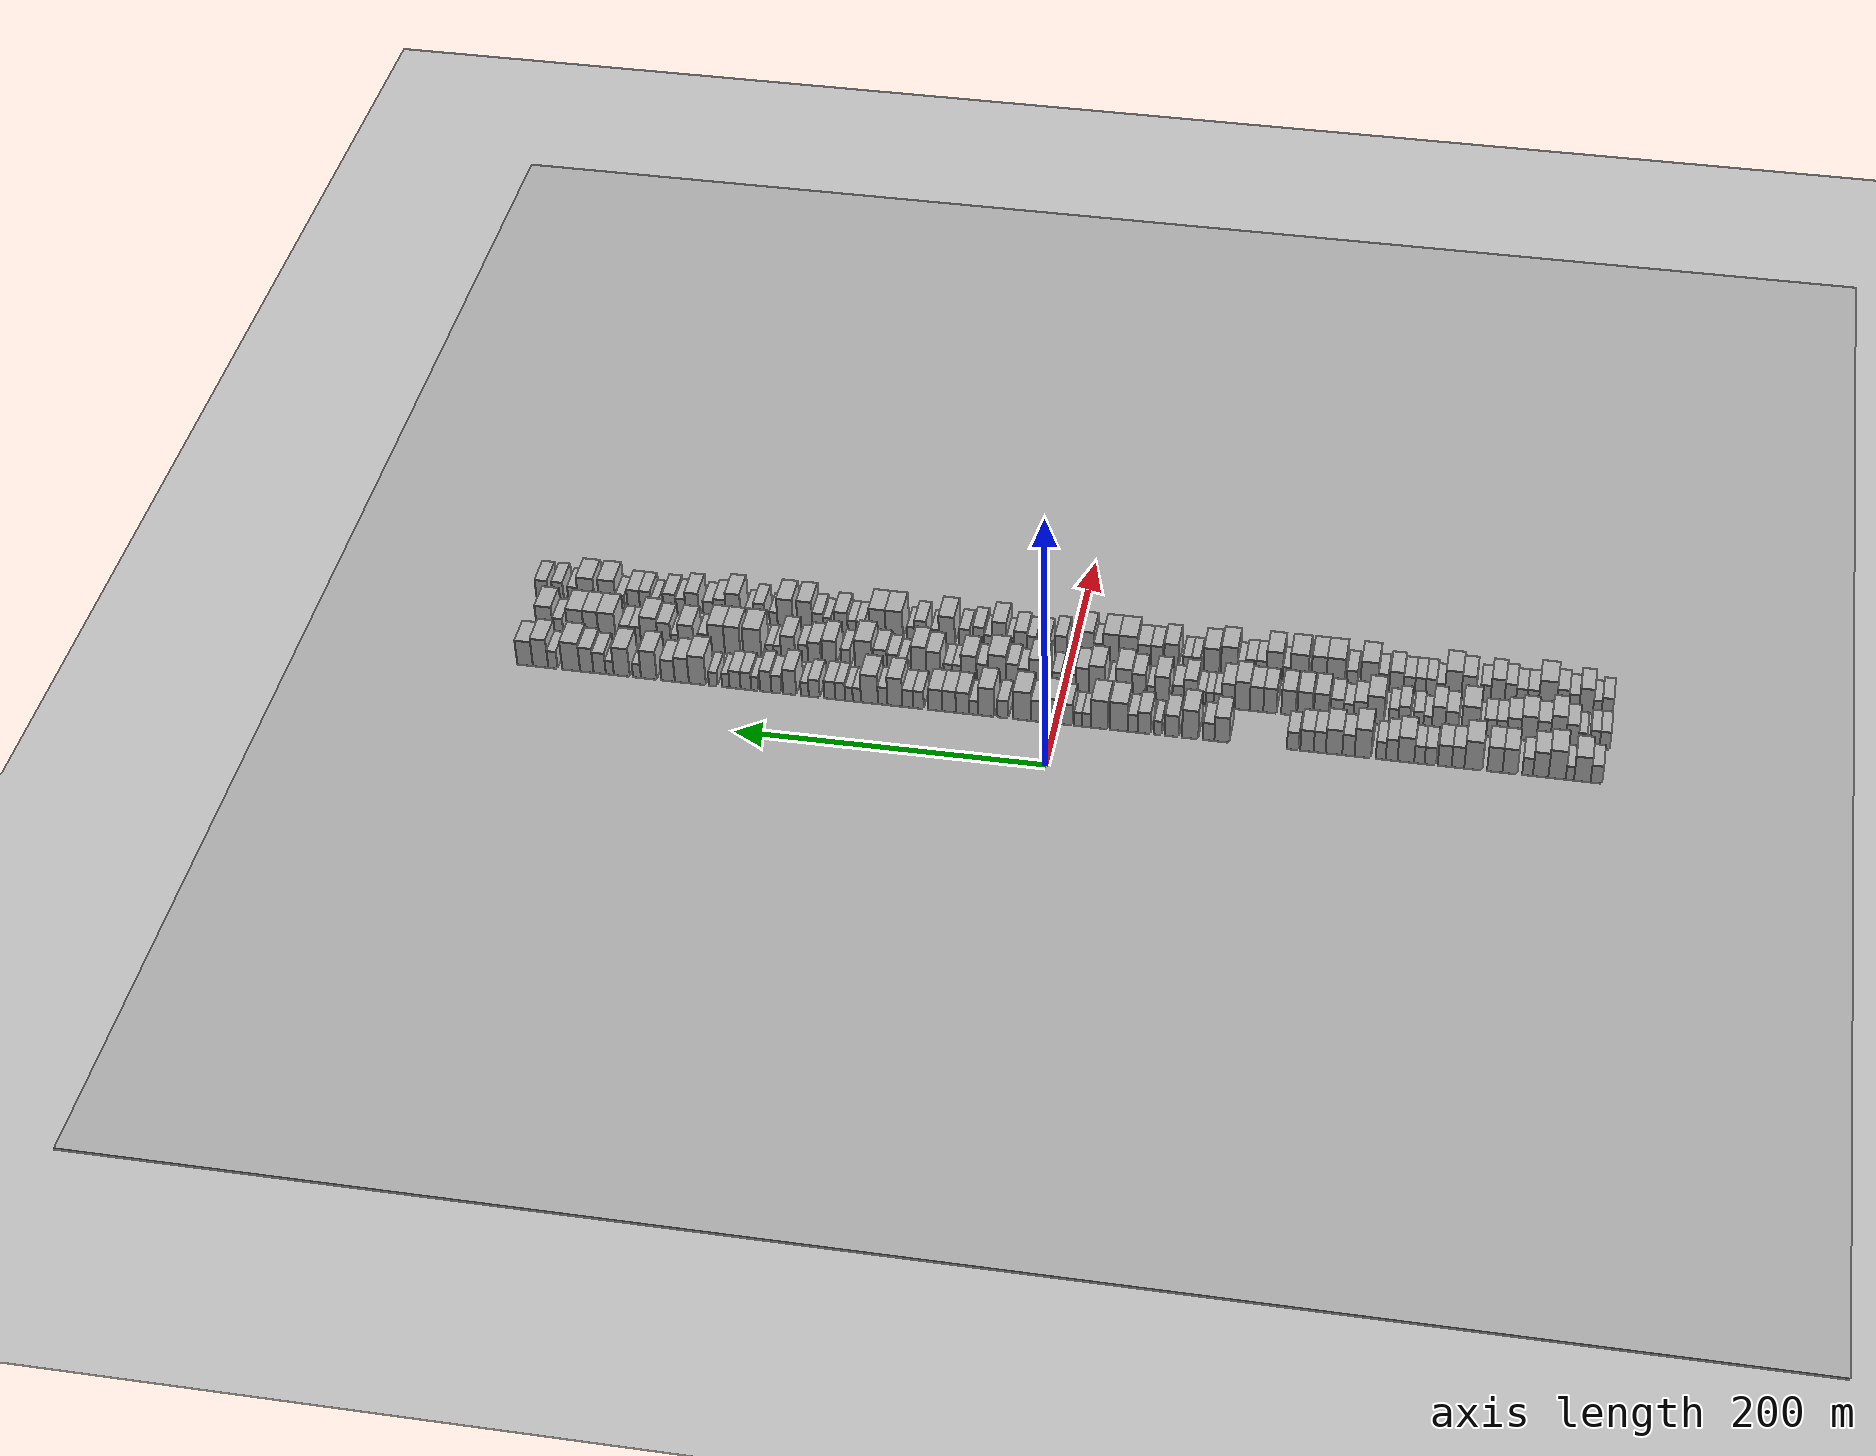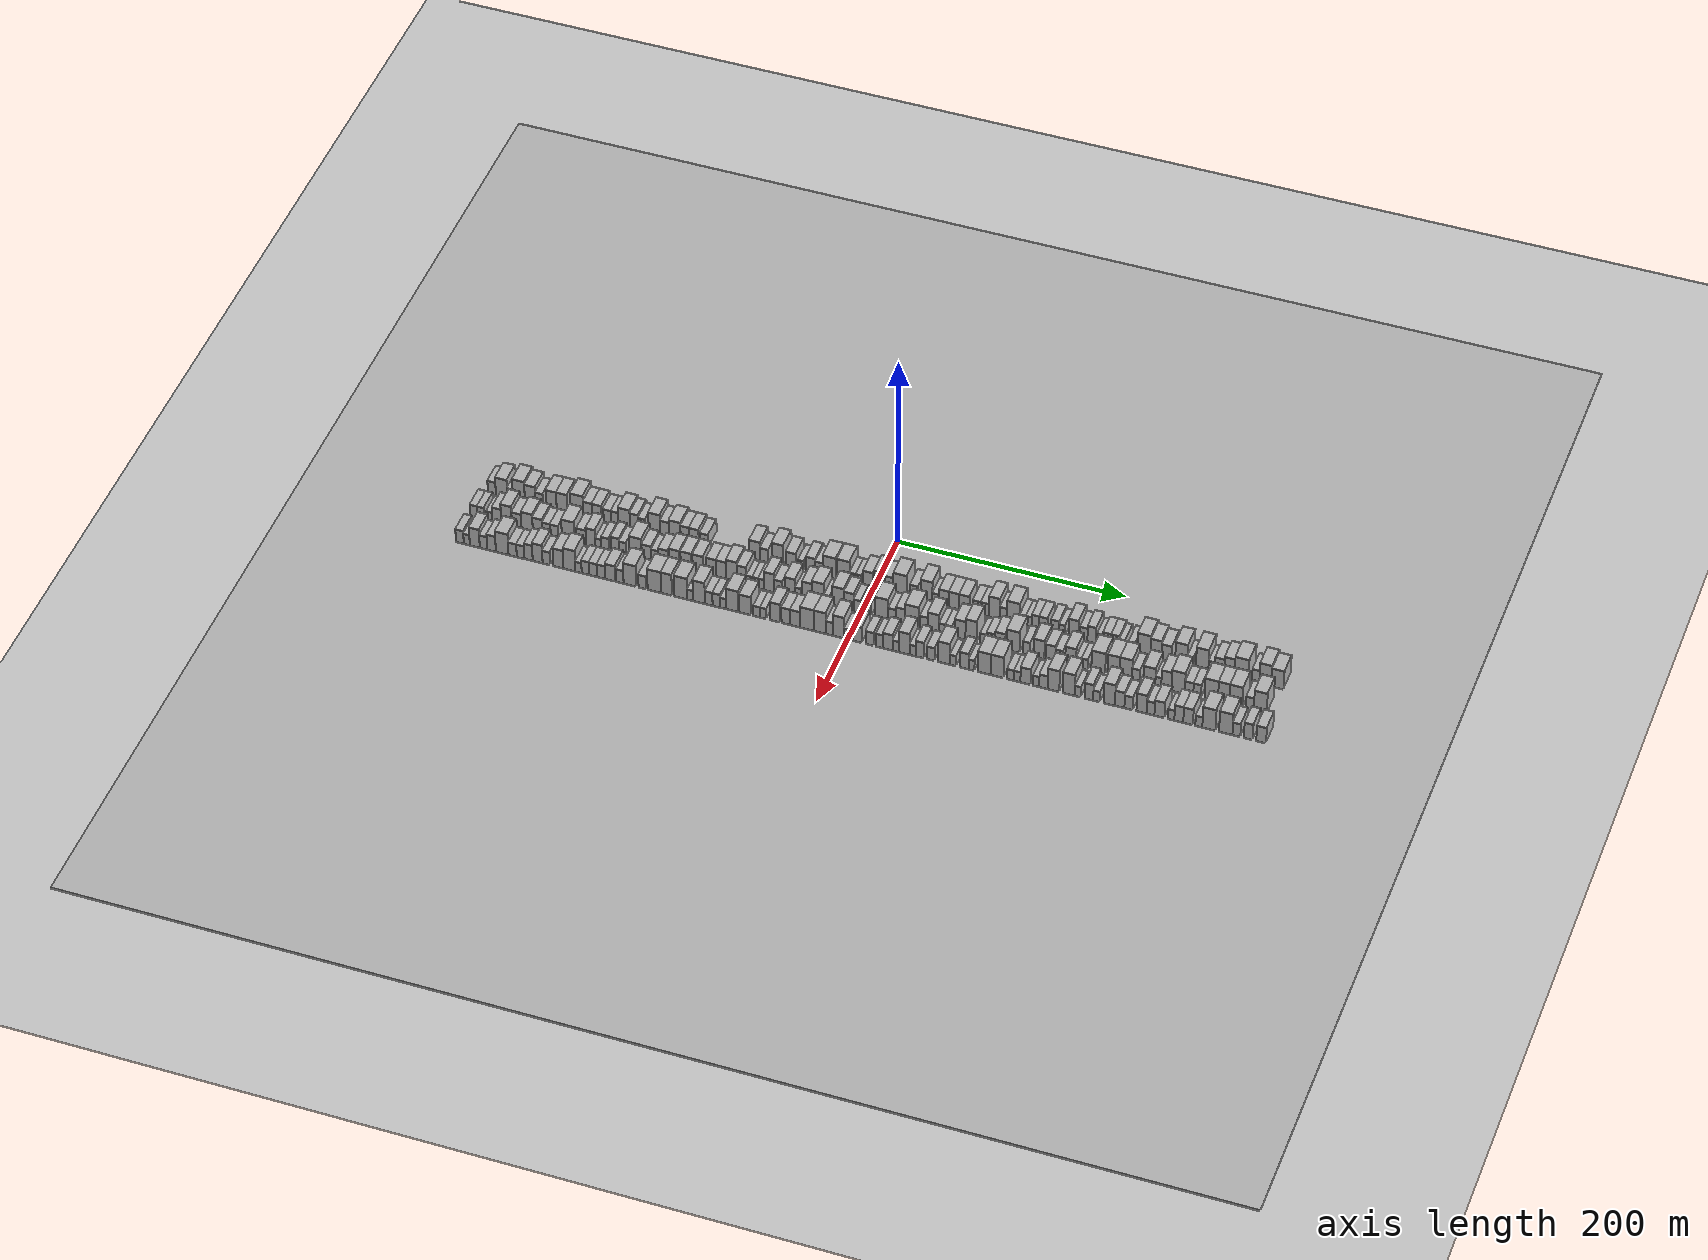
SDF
<?xml version="1.0" encoding="utf-8"?>

<sdf version="1.6">

   <world name="default">

      <gui fullscreen="0">

         <camera name="user_camera">

            <pose>-15 0 4.57585 0 0 0</pose>

            <view_controller>orbit</view_controller>

         </camera>

      </gui>

      <scene>

         <sky>

           <clouds>

             <speed>12</speed>

           </clouds>

         </sky>

         <ambient>0.4 0.4 0.4 1</ambient>

         <background>0.7 0.7 0.7 1</background>

         <shadows>1</shadows>

      </scene>

      <gravity>0 0 -9.8066</gravity>

      <magnetic_field>6e-06 2.3e-05 -4.2e-05</magnetic_field>

      <physics default="0" name="default_physics" type="ode">

         <ode>

            <solver>

               <type>quick</type>

               <iters>10</iters>

               <sor>1.0</sor>

               <use_dynamic_moi_rescaling>0</use_dynamic_moi_rescaling>

            </solver>

            <constraints>

               <cfm>0</cfm>

               <erp>0.2</erp>

               <contact_max_correcting_vel>100</contact_max_correcting_vel>

               <contact_surface_layer>0.001</contact_surface_layer>

            </constraints>

         </ode>

         <max_step_size>0.004</max_step_size>

         <real_time_factor>1</real_time_factor>

         <real_time_update_rate>250</real_time_update_rate>

      </physics>

      <light name="sun" type="directional">

         <cast_shadows>1</cast_shadows>

         <pose>0 0 10 0 0 0</pose>

         <diffuse>0.8 0.8 0.8 1</diffuse>

         <specular>0.2 0.2 0.2 1</specular>

         <attenuation>

            <range>1000</range>

            <constant>0.9</constant>

            <linear>0.01</linear>

            <quadratic>0.001</quadratic>

         </attenuation>

         <direction>-0.5 0.1 -0.9</direction>

      </light>

      <include>

         <name>ground_plane_1</name>

         <uri>model://HANNAS_ground_plane</uri>

         <pose>0 0 0  0 0 0</pose>

      </include>

      <include>

         <name>ground_plane_2</name>

         <uri>model://HANNAS_ground_plane</uri>

         <pose>100 0 0  0 0 0</pose>

      </include>

      <model name="building_1">

         <static>1</static>

         <pose frame="">50.0000 -341.4122 0 0.000000 0.000000 0.000000</pose>

         <link name="link">

            <pose frame="">0 0 7.50 0 0 0</pose>

            <collision name="collision">

               <geometry>

                  <box>

                     <size>20.0000 7.1757 15.0000</size>

                  </box>

               </geometry>

               <max_contacts>10</max_contacts>

               <surface>

                  <contact>

                     <ode/>

                  </contact>

                  <bounce/>

                  <friction>

                     <torsional>

                        <ode/>

                     </torsional>

                     <ode/>

                  </friction>

               </surface>

            </collision>

            <visual name="visual">

               <cast_shadows>0</cast_shadows>

               <geometry>

                  <box>

                     <size>20.0000 7.1757 15.0000</size>

                  </box>

               </geometry>

               <material>

                  <script>

                     <uri>model://HANNAS_wall/materials/scripts</uri>

                     <uri>model://HANNAS_wall/materials/textures</uri>

                     <name>vrc/HANNAS_wall</name>

                  </script>

               </material>

            </visual>

            <self_collide>0</self_collide>

            <enable_wind>0</enable_wind>

            <kinematic>0</kinematic>

         </link>

      </model>

      <model name="building_2">

         <static>1</static>

         <pose frame="">50.0000 -332.6353 0 0.000000 0.000000 0.000000</pose>

         <link name="link">

            <pose frame="">0 0 10.50 0 0 0</pose>

            <collision name="collision">

               <geometry>

                  <box>

                     <size>20.0000 10.3781 21.0000</size>

                  </box>

               </geometry>

               <max_contacts>10</max_contacts>

               <surface>

                  <contact>

                     <ode/>

                  </contact>

                  <bounce/>

                  <friction>

                     <torsional>

                        <ode/>

                     </torsional>

                     <ode/>

                  </friction>

               </surface>

            </collision>

            <visual name="visual">

               <cast_shadows>0</cast_shadows>

               <geometry>

                  <box>

                     <size>20.0000 10.3781 21.0000</size>

                  </box>

               </geometry>

               <material>

                  <script>

                     <uri>model://HANNAS_wall/materials/scripts</uri>

                     <uri>model://HANNAS_wall/materials/textures</uri>

                     <name>vrc/HANNAS_wall</name>

                  </script>

               </material>

            </visual>

            <self_collide>0</self_collide>

            <enable_wind>0</enable_wind>

            <kinematic>0</kinematic>

         </link>

      </model>

      <model name="building_3">

         <static>1</static>

         <pose frame="">50.0000 -324.8922 0 0.000000 0.000000 0.000000</pose>

         <link name="link">

            <pose frame="">0 0 6.00 0 0 0</pose>

            <collision name="collision">

               <geometry>

                  <box>

                     <size>20.0000 5.1081 12.0000</size>

                  </box>

               </geometry>

               <max_contacts>10</max_contacts>

               <surface>

                  <contact>

                     <ode/>

                  </contact>

                  <bounce/>

                  <friction>

                     <torsional>

                        <ode/>

                     </torsional>

                     <ode/>

                  </friction>

               </surface>

            </collision>

            <visual name="visual">

               <cast_shadows>0</cast_shadows>

               <geometry>

                  <box>

                     <size>20.0000 5.1081 12.0000</size>

                  </box>

               </geometry>

               <material>

                  <script>

                     <uri>model://HANNAS_wall/materials/scripts</uri>

                     <uri>model://HANNAS_wall/materials/textures</uri>

                     <name>vrc/HANNAS_wall</name>

                  </script>

               </material>

            </visual>

            <self_collide>0</self_collide>

            <enable_wind>0</enable_wind>

            <kinematic>0</kinematic>

         </link>

      </model>

      <model name="building_4">

         <static>1</static>

         <pose frame="">50.0000 -316.9242 0 0.000000 0.000000 0.000000</pose>

         <link name="link">

            <pose frame="">0 0 12.00 0 0 0</pose>

            <collision name="collision">

               <geometry>

                  <box>

                     <size>20.0000 10.8280 24.0000</size>

                  </box>

               </geometry>

               <max_contacts>10</max_contacts>

               <surface>

                  <contact>

                     <ode/>

                  </contact>

                  <bounce/>

                  <friction>

                     <torsional>

                        <ode/>

                     </torsional>

                     <ode/>

                  </friction>

               </surface>

            </collision>

            <visual name="visual">

               <cast_shadows>0</cast_shadows>

               <geometry>

                  <box>

                     <size>20.0000 10.8280 24.0000</size>

                  </box>

               </geometry>

               <material>

                  <script>

                     <uri>model://HANNAS_wall/materials/scripts</uri>

                     <uri>model://HANNAS_wall/materials/textures</uri>

                     <name>vrc/HANNAS_wall</name>

                  </script>

               </material>

            </visual>

            <self_collide>0</self_collide>

            <enable_wind>0</enable_wind>

            <kinematic>0</kinematic>

         </link>

      </model>

      <model name="building_5">

         <static>1</static>

         <pose frame="">50.0000 -306.6787 0 0.000000 0.000000 0.000000</pose>

         <link name="link">

            <pose frame="">0 0 10.50 0 0 0</pose>

            <collision name="collision">

               <geometry>

                  <box>

                     <size>20.0000 9.6630 21.0000</size>

                  </box>

               </geometry>

               <max_contacts>10</max_contacts>

               <surface>

                  <contact>

                     <ode/>

                  </contact>

                  <bounce/>

                  <friction>

                     <torsional>

                        <ode/>

                     </torsional>

                     <ode/>

                  </friction>

               </surface>

            </collision>

            <visual name="visual">

               <cast_shadows>0</cast_shadows>

               <geometry>

                  <box>

                     <size>20.0000 9.6630 21.0000</size>

                  </box>

               </geometry>

               <material>

                  <script>

                     <uri>model://HANNAS_wall/materials/scripts</uri>

                     <uri>model://HANNAS_wall/materials/textures</uri>

                     <name>vrc/HANNAS_wall</name>

                  </script>

               </material>

            </visual>

            <self_collide>0</self_collide>

            <enable_wind>0</enable_wind>

            <kinematic>0</kinematic>

         </link>

      </model>

      <model name="building_6">

         <static>1</static>

         <pose frame="">50.0000 -298.5172 0 0.000000 0.000000 0.000000</pose>

         <link name="link">

            <pose frame="">0 0 7.50 0 0 0</pose>

            <collision name="collision">

               <geometry>

                  <box>

                     <size>20.0000 6.6600 15.0000</size>

                  </box>

               </geometry>

               <max_contacts>10</max_contacts>

               <surface>

                  <contact>

                     <ode/>

                  </contact>

                  <bounce/>

                  <friction>

                     <torsional>

                        <ode/>

                     </torsional>

                     <ode/>

                  </friction>

               </surface>

            </collision>

            <visual name="visual">

               <cast_shadows>0</cast_shadows>

               <geometry>

                  <box>

                     <size>20.0000 6.6600 15.0000</size>

                  </box>

               </geometry>

               <material>

                  <script>

                     <uri>model://HANNAS_wall/materials/scripts</uri>

                     <uri>model://HANNAS_wall/materials/textures</uri>

                     <name>vrc/HANNAS_wall</name>

                  </script>

               </material>

            </visual>

            <self_collide>0</self_collide>

            <enable_wind>0</enable_wind>

            <kinematic>0</kinematic>

         </link>

      </model>

      <model name="building_7">

         <static>1</static>

         <pose frame="">50.0000 -287.5001 0 0.000000 0.000000 0.000000</pose>

         <link name="link">

            <pose frame="">0 0 10.50 0 0 0</pose>

            <collision name="collision">

               <geometry>

                  <box>

                     <size>20.0000 9.3741 21.0000</size>

                  </box>

               </geometry>

               <max_contacts>10</max_contacts>

               <surface>

                  <contact>

                     <ode/>

                  </contact>

                  <bounce/>

                  <friction>

                     <torsional>

                        <ode/>

                     </torsional>

                     <ode/>

                  </friction>

               </surface>

            </collision>

            <visual name="visual">

               <cast_shadows>0</cast_shadows>

               <geometry>

                  <box>

                     <size>20.0000 9.3741 21.0000</size>

                  </box>

               </geometry>

               <material>

                  <script>

                     <uri>model://HANNAS_wall/materials/scripts</uri>

                     <uri>model://HANNAS_wall/materials/textures</uri>

                     <name>vrc/HANNAS_wall</name>

                  </script>

               </material>

            </visual>

            <self_collide>0</self_collide>

            <enable_wind>0</enable_wind>

            <kinematic>0</kinematic>

         </link>

      </model>

      <model name="building_8">

         <static>1</static>

         <pose frame="">50.0000 -278.0245 0 0.000000 0.000000 0.000000</pose>

         <link name="link">

            <pose frame="">0 0 10.50 0 0 0</pose>

            <collision name="collision">

               <geometry>

                  <box>

                     <size>20.0000 9.5772 21.0000</size>

                  </box>

               </geometry>

               <max_contacts>10</max_contacts>

               <surface>

                  <contact>

                     <ode/>

                  </contact>

                  <bounce/>

                  <friction>

                     <torsional>

                        <ode/>

                     </torsional>

                     <ode/>

                  </friction>

               </surface>

            </collision>

            <visual name="visual">

               <cast_shadows>0</cast_shadows>

               <geometry>

                  <box>

                     <size>20.0000 9.5772 21.0000</size>

                  </box>

               </geometry>

               <material>

                  <script>

                     <uri>model://HANNAS_wall/materials/scripts</uri>

                     <uri>model://HANNAS_wall/materials/textures</uri>

                     <name>vrc/HANNAS_wall</name>

                  </script>

               </material>

            </visual>

            <self_collide>0</self_collide>

            <enable_wind>0</enable_wind>

            <kinematic>0</kinematic>

         </link>

      </model>

      <model name="building_9">

         <static>1</static>

         <pose frame="">50.0000 -264.5718 0 0.000000 0.000000 0.000000</pose>

         <link name="link">

            <pose frame="">0 0 12.00 0 0 0</pose>

            <collision name="collision">

               <geometry>

                  <box>

                     <size>20.0000 11.3282 24.0000</size>

                  </box>

               </geometry>

               <max_contacts>10</max_contacts>

               <surface>

                  <contact>

                     <ode/>

                  </contact>

                  <bounce/>

                  <friction>

                     <torsional>

                        <ode/>

                     </torsional>

                     <ode/>

                  </friction>

               </surface>

            </collision>

            <visual name="visual">

               <cast_shadows>0</cast_shadows>

               <geometry>

                  <box>

                     <size>20.0000 11.3282 24.0000</size>

                  </box>

               </geometry>

               <material>

                  <script>

                     <uri>model://HANNAS_wall/materials/scripts</uri>

                     <uri>model://HANNAS_wall/materials/textures</uri>

                     <name>vrc/HANNAS_wall</name>

                  </script>

               </material>

            </visual>

            <self_collide>0</self_collide>

            <enable_wind>0</enable_wind>

            <kinematic>0</kinematic>

         </link>

      </model>

      <model name="building_10">

         <static>1</static>

         <pose frame="">50.0000 -254.9156 0 0.000000 0.000000 0.000000</pose>

         <link name="link">

            <pose frame="">0 0 9.00 0 0 0</pose>

            <collision name="collision">

               <geometry>

                  <box>

                     <size>20.0000 7.9842 18.0000</size>

                  </box>

               </geometry>

               <max_contacts>10</max_contacts>

               <surface>

                  <contact>

                     <ode/>

                  </contact>

                  <bounce/>

                  <friction>

                     <torsional>

                        <ode/>

                     </torsional>

                     <ode/>

                  </friction>

               </surface>

            </collision>

            <visual name="visual">

               <cast_shadows>0</cast_shadows>

               <geometry>

                  <box>

                     <size>20.0000 7.9842 18.0000</size>

                  </box>

               </geometry>

               <material>

                  <script>

                     <uri>model://HANNAS_wall/materials/scripts</uri>

                     <uri>model://HANNAS_wall/materials/textures</uri>

                     <name>vrc/HANNAS_wall</name>

                  </script>

               </material>

            </visual>

            <self_collide>0</self_collide>

            <enable_wind>0</enable_wind>

            <kinematic>0</kinematic>

         </link>

      </model>

      <model name="building_11">

         <static>1</static>

         <pose frame="">50.0000 -246.5687 0 0.000000 0.000000 0.000000</pose>

         <link name="link">

            <pose frame="">0 0 9.00 0 0 0</pose>

            <collision name="collision">

               <geometry>

                  <box>

                     <size>20.0000 8.7096 18.0000</size>

                  </box>

               </geometry>

               <max_contacts>10</max_contacts>

               <surface>

                  <contact>

                     <ode/>

                  </contact>

                  <bounce/>

                  <friction>

                     <torsional>

                        <ode/>

                     </torsional>

                     <ode/>

                  </friction>

               </surface>

            </collision>

            <visual name="visual">

               <cast_shadows>0</cast_shadows>

               <geometry>

                  <box>

                     <size>20.0000 8.7096 18.0000</size>

                  </box>

               </geometry>

               <material>

                  <script>

                     <uri>model://HANNAS_wall/materials/scripts</uri>

                     <uri>model://HANNAS_wall/materials/textures</uri>

                     <name>vrc/HANNAS_wall</name>

                  </script>

               </material>

            </visual>

            <self_collide>0</self_collide>

            <enable_wind>0</enable_wind>

            <kinematic>0</kinematic>

         </link>

      </model>

      <model name="building_12">

         <static>1</static>

         <pose frame="">50.0000 -237.5561 0 0.000000 0.000000 0.000000</pose>

         <link name="link">

            <pose frame="">0 0 7.50 0 0 0</pose>

            <collision name="collision">

               <geometry>

                  <box>

                     <size>20.0000 7.3157 15.0000</size>

                  </box>

               </geometry>

               <max_contacts>10</max_contacts>

               <surface>

                  <contact>

                     <ode/>

                  </contact>

                  <bounce/>

                  <friction>

                     <torsional>

                        <ode/>

                     </torsional>

                     <ode/>

                  </friction>

               </surface>

            </collision>

            <visual name="visual">

               <cast_shadows>0</cast_shadows>

               <geometry>

                  <box>

                     <size>20.0000 7.3157 15.0000</size>

                  </box>

               </geometry>

               <material>

                  <script>

                     <uri>model://HANNAS_wall/materials/scripts</uri>

                     <uri>model://HANNAS_wall/materials/textures</uri>

                     <name>vrc/HANNAS_wall</name>

                  </script>

               </material>

            </visual>

            <self_collide>0</self_collide>

            <enable_wind>0</enable_wind>

            <kinematic>0</kinematic>

         </link>

      </model>

      <model name="building_13">

         <static>1</static>

         <pose frame="">50.0000 -230.6666 0 0.000000 0.000000 0.000000</pose>

         <link name="link">

            <pose frame="">0 0 7.50 0 0 0</pose>

            <collision name="collision">

               <geometry>

                  <box>

                     <size>20.0000 6.4633 15.0000</size>

                  </box>

               </geometry>

               <max_contacts>10</max_contacts>

               <surface>

                  <contact>

                     <ode/>

                  </contact>

                  <bounce/>

                  <friction>

                     <torsional>

                        <ode/>

                     </torsional>

                     <ode/>

                  </friction>

               </surface>

            </collision>

            <visual name="visual">

               <cast_shadows>0</cast_shadows>

               <geometry>

                  <box>

                     <size>20.0000 6.4633 15.0000</size>

                  </box>

               </geometry>

               <material>

                  <script>

                     <uri>model://HANNAS_wall/materials/scripts</uri>

                     <uri>model://HANNAS_wall/materials/textures</uri>

                     <name>vrc/HANNAS_wall</name>

                  </script>

               </material>

            </visual>

            <self_collide>0</self_collide>

            <enable_wind>0</enable_wind>

            <kinematic>0</kinematic>

         </link>

      </model>

      <model name="building_14">

         <static>1</static>

         <pose frame="">50.0000 -222.1933 0 0.000000 0.000000 0.000000</pose>

         <link name="link">

            <pose frame="">0 0 10.50 0 0 0</pose>

            <collision name="collision">

               <geometry>

                  <box>

                     <size>20.0000 10.4833 21.0000</size>

                  </box>

               </geometry>

               <max_contacts>10</max_contacts>

               <surface>

                  <contact>

                     <ode/>

                  </contact>

                  <bounce/>

                  <friction>

                     <torsional>

                        <ode/>

                     </torsional>

                     <ode/>

                  </friction>

               </surface>

            </collision>

            <visual name="visual">

               <cast_shadows>0</cast_shadows>

               <geometry>

                  <box>

                     <size>20.0000 10.4833 21.0000</size>

                  </box>

               </geometry>

               <material>

                  <script>

                     <uri>model://HANNAS_wall/materials/scripts</uri>

                     <uri>model://HANNAS_wall/materials/textures</uri>

                     <name>vrc/HANNAS_wall</name>

                  </script>

               </material>

            </visual>

            <self_collide>0</self_collide>

            <enable_wind>0</enable_wind>

            <kinematic>0</kinematic>

         </link>

      </model>

      <model name="building_15">

         <static>1</static>

         <pose frame="">50.0000 -213.2022 0 0.000000 0.000000 0.000000</pose>

         <link name="link">

            <pose frame="">0 0 9.00 0 0 0</pose>

            <collision name="collision">

               <geometry>

                  <box>

                     <size>20.0000 7.4988 18.0000</size>

                  </box>

               </geometry>

               <max_contacts>10</max_contacts>

               <surface>

                  <contact>

                     <ode/>

                  </contact>

                  <bounce/>

                  <friction>

                     <torsional>

                        <ode/>

                     </torsional>

                     <ode/>

                  </friction>

               </surface>

            </collision>

            <visual name="visual">

               <cast_shadows>0</cast_shadows>

               <geometry>

                  <box>

                     <size>20.0000 7.4988 18.0000</size>

                  </box>

               </geometry>

               <material>

                  <script>

                     <uri>model://HANNAS_wall/materials/scripts</uri>

                     <uri>model://HANNAS_wall/materials/textures</uri>

                     <name>vrc/HANNAS_wall</name>

                  </script>

               </material>

            </visual>

            <self_collide>0</self_collide>

            <enable_wind>0</enable_wind>

            <kinematic>0</kinematic>

         </link>

      </model>

      <model name="building_16">

         <static>1</static>

         <pose frame="">50.0000 -206.3349 0 0.000000 0.000000 0.000000</pose>

         <link name="link">

            <pose frame="">0 0 7.50 0 0 0</pose>

            <collision name="collision">

               <geometry>

                  <box>

                     <size>20.0000 6.2358 15.0000</size>

                  </box>

               </geometry>

               <max_contacts>10</max_contacts>

               <surface>

                  <contact>

                     <ode/>

                  </contact>

                  <bounce/>

                  <friction>

                     <torsional>

                        <ode/>

                     </torsional>

                     <ode/>

                  </friction>

               </surface>

            </collision>

            <visual name="visual">

               <cast_shadows>0</cast_shadows>

               <geometry>

                  <box>

                     <size>20.0000 6.2358 15.0000</size>

                  </box>

               </geometry>

               <material>

                  <script>

                     <uri>model://HANNAS_wall/materials/scripts</uri>

                     <uri>model://HANNAS_wall/materials/textures</uri>

                     <name>vrc/HANNAS_wall</name>

                  </script>

               </material>

            </visual>

            <self_collide>0</self_collide>

            <enable_wind>0</enable_wind>

            <kinematic>0</kinematic>

         </link>

      </model>

      <model name="building_17">

         <static>1</static>

         <pose frame="">50.0000 -195.0104 0 0.000000 0.000000 0.000000</pose>

         <link name="link">

            <pose frame="">0 0 12.00 0 0 0</pose>

            <collision name="collision">

               <geometry>

                  <box>

                     <size>20.0000 10.4131 24.0000</size>

                  </box>

               </geometry>

               <max_contacts>10</max_contacts>

               <surface>

                  <contact>

                     <ode/>

                  </contact>

                  <bounce/>

                  <friction>

                     <torsional>

                        <ode/>

                     </torsional>

                     <ode/>

                  </friction>

               </surface>

            </collision>

            <visual name="visual">

               <cast_shadows>0</cast_shadows>

               <geometry>

                  <box>

                     <size>20.0000 10.4131 24.0000</size>

                  </box>

               </geometry>

               <material>

                  <script>

                     <uri>model://HANNAS_wall/materials/scripts</uri>

                     <uri>model://HANNAS_wall/materials/textures</uri>

                     <name>vrc/HANNAS_wall</name>

                  </script>

               </material>

            </visual>

            <self_collide>0</self_collide>

            <enable_wind>0</enable_wind>

            <kinematic>0</kinematic>

         </link>

      </model>

      <model name="building_18">

         <static>1</static>

         <pose frame="">50.0000 -185.9215 0 0.000000 0.000000 0.000000</pose>

         <link name="link">

            <pose frame="">0 0 9.00 0 0 0</pose>

            <collision name="collision">

               <geometry>

                  <box>

                     <size>20.0000 7.7647 18.0000</size>

                  </box>

               </geometry>

               <max_contacts>10</max_contacts>

               <surface>

                  <contact>

                     <ode/>

                  </contact>

                  <bounce/>

                  <friction>

                     <torsional>

                        <ode/>

                     </torsional>

                     <ode/>

                  </friction>

               </surface>

            </collision>

            <visual name="visual">

               <cast_shadows>0</cast_shadows>

               <geometry>

                  <box>

                     <size>20.0000 7.7647 18.0000</size>

                  </box>

               </geometry>

               <material>

                  <script>

                     <uri>model://HANNAS_wall/materials/scripts</uri>

                     <uri>model://HANNAS_wall/materials/textures</uri>

                     <name>vrc/HANNAS_wall</name>

                  </script>

               </material>

            </visual>

            <self_collide>0</self_collide>

            <enable_wind>0</enable_wind>

            <kinematic>0</kinematic>

         </link>

      </model>

      <model name="building_19">

         <static>1</static>

         <pose frame="">50.0000 -176.8007 0 0.000000 0.000000 0.000000</pose>

         <link name="link">

            <pose frame="">0 0 10.50 0 0 0</pose>

            <collision name="collision">

               <geometry>

                  <box>

                     <size>20.0000 10.4769 21.0000</size>

                  </box>

               </geometry>

               <max_contacts>10</max_contacts>

               <surface>

                  <contact>

                     <ode/>

                  </contact>

                  <bounce/>

                  <friction>

                     <torsional>

                        <ode/>

                     </torsional>

                     <ode/>

                  </friction>

               </surface>

            </collision>

            <visual name="visual">

               <cast_shadows>0</cast_shadows>

               <geometry>

                  <box>

                     <size>20.0000 10.4769 21.0000</size>

                  </box>

               </geometry>

               <material>

                  <script>

                     <uri>model://HANNAS_wall/materials/scripts</uri>

                     <uri>model://HANNAS_wall/materials/textures</uri>

                     <name>vrc/HANNAS_wall</name>

                  </script>

               </material>

            </visual>

            <self_collide>0</self_collide>

            <enable_wind>0</enable_wind>

            <kinematic>0</kinematic>

         </link>

      </model>

      <model name="building_20">

         <static>1</static>

         <pose frame="">50.0000 -167.7494 0 0.000000 0.000000 0.000000</pose>

         <link name="link">

            <pose frame="">0 0 9.00 0 0 0</pose>

            <collision name="collision">

               <geometry>

                  <box>

                     <size>20.0000 7.6257 18.0000</size>

                  </box>

               </geometry>

               <max_contacts>10</max_contacts>

               <surface>

                  <contact>

                     <ode/>

                  </contact>

                  <bounce/>

                  <friction>

                     <torsional>

                        <ode/>

                     </torsional>

                     <ode/>

                  </friction>

               </surface>

            </collision>

            <visual name="visual">

               <cast_shadows>0</cast_shadows>

               <geometry>

                  <box>

                     <size>20.0000 7.6257 18.0000</size>

                  </box>

               </geometry>

               <material>

                  <script>

                     <uri>model://HANNAS_wall/materials/scripts</uri>

                     <uri>model://HANNAS_wall/materials/textures</uri>

                     <name>vrc/HANNAS_wall</name>

                  </script>

               </material>

            </visual>

            <self_collide>0</self_collide>

            <enable_wind>0</enable_wind>

            <kinematic>0</kinematic>

         </link>

      </model>

      <model name="building_21">

         <static>1</static>

         <pose frame="">50.0000 -159.7060 0 0.000000 0.000000 0.000000</pose>

         <link name="link">

            <pose frame="">0 0 9.00 0 0 0</pose>

            <collision name="collision">

               <geometry>

                  <box>

                     <size>20.0000 8.4612 18.0000</size>

                  </box>

               </geometry>

               <max_contacts>10</max_contacts>

               <surface>

                  <contact>

                     <ode/>

                  </contact>

                  <bounce/>

                  <friction>

                     <torsional>

                        <ode/>

                     </torsional>

                     <ode/>

                  </friction>

               </surface>

            </collision>

            <visual name="visual">

               <cast_shadows>0</cast_shadows>

               <geometry>

                  <box>

                     <size>20.0000 8.4612 18.0000</size>

                  </box>

               </geometry>

               <material>

                  <script>

                     <uri>model://HANNAS_wall/materials/scripts</uri>

                     <uri>model://HANNAS_wall/materials/textures</uri>

                     <name>vrc/HANNAS_wall</name>

                  </script>

               </material>

            </visual>

            <self_collide>0</self_collide>

            <enable_wind>0</enable_wind>

            <kinematic>0</kinematic>

         </link>

      </model>

      <model name="building_22">

         <static>1</static>

         <pose frame="">50.0000 -150.7379 0 0.000000 0.000000 0.000000</pose>

         <link name="link">

            <pose frame="">0 0 7.50 0 0 0</pose>

            <collision name="collision">

               <geometry>

                  <box>

                     <size>20.0000 7.4750 15.0000</size>

                  </box>

               </geometry>

               <max_contacts>10</max_contacts>

               <surface>

                  <contact>

                     <ode/>

                  </contact>

                  <bounce/>

                  <friction>

                     <torsional>

                        <ode/>

                     </torsional>

                     <ode/>

                  </friction>

               </surface>

            </collision>

            <visual name="visual">

               <cast_shadows>0</cast_shadows>

               <geometry>

                  <box>

                     <size>20.0000 7.4750 15.0000</size>

                  </box>

               </geometry>

               <material>

                  <script>

                     <uri>model://HANNAS_wall/materials/scripts</uri>

                     <uri>model://HANNAS_wall/materials/textures</uri>

                     <name>vrc/HANNAS_wall</name>

                  </script>

               </material>

            </visual>

            <self_collide>0</self_collide>

            <enable_wind>0</enable_wind>

            <kinematic>0</kinematic>

         </link>

      </model>

      <model name="building_23">

         <static>1</static>

         <pose frame="">50.0000 -105.6504 0 0.000000 0.000000 0.000000</pose>

         <link name="link">

            <pose frame="">0 0 10.50 0 0 0</pose>

            <collision name="collision">

               <geometry>

                  <box>

                     <size>20.0000 9.5667 21.0000</size>

                  </box>

               </geometry>

               <max_contacts>10</max_contacts>

               <surface>

                  <contact>

                     <ode/>

                  </contact>

                  <bounce/>

                  <friction>

                     <torsional>

                        <ode/>

                     </torsional>

                     <ode/>

                  </friction>

               </surface>

            </collision>

            <visual name="visual">

               <cast_shadows>0</cast_shadows>

               <geometry>

                  <box>

                     <size>20.0000 9.5667 21.0000</size>

                  </box>

               </geometry>

               <material>

                  <script>

                     <uri>model://HANNAS_wall/materials/scripts</uri>

                     <uri>model://HANNAS_wall/materials/textures</uri>

                     <name>vrc/HANNAS_wall</name>

                  </script>

               </material>

            </visual>

            <self_collide>0</self_collide>

            <enable_wind>0</enable_wind>

            <kinematic>0</kinematic>

         </link>

      </model>

      <model name="building_24">

         <static>1</static>

         <pose frame="">50.0000 -97.2119 0 0.000000 0.000000 0.000000</pose>

         <link name="link">

            <pose frame="">0 0 7.50 0 0 0</pose>

            <collision name="collision">

               <geometry>

                  <box>

                     <size>20.0000 7.3102 15.0000</size>

                  </box>

               </geometry>

               <max_contacts>10</max_contacts>

               <surface>

                  <contact>

                     <ode/>

                  </contact>

                  <bounce/>

                  <friction>

                     <torsional>

                        <ode/>

                     </torsional>

                     <ode/>

                  </friction>

               </surface>

            </collision>

            <visual name="visual">

               <cast_shadows>0</cast_shadows>

               <geometry>

                  <box>

                     <size>20.0000 7.3102 15.0000</size>

                  </box>

               </geometry>

               <material>

                  <script>

                     <uri>model://HANNAS_wall/materials/scripts</uri>

                     <uri>model://HANNAS_wall/materials/textures</uri>

                     <name>vrc/HANNAS_wall</name>

                  </script>

               </material>

            </visual>

            <self_collide>0</self_collide>

            <enable_wind>0</enable_wind>

            <kinematic>0</kinematic>

         </link>

      </model>

      <model name="building_25">

         <static>1</static>

         <pose frame="">50.0000 -85.3926 0 0.000000 0.000000 0.000000</pose>

         <link name="link">

            <pose frame="">0 0 12.00 0 0 0</pose>

            <collision name="collision">

               <geometry>

                  <box>

                     <size>20.0000 10.3284 24.0000</size>

                  </box>

               </geometry>

               <max_contacts>10</max_contacts>

               <surface>

                  <contact>

                     <ode/>

                  </contact>

                  <bounce/>

                  <friction>

                     <torsional>

                        <ode/>

                     </torsional>

                     <ode/>

                  </friction>

               </surface>

            </collision>

            <visual name="visual">

               <cast_shadows>0</cast_shadows>

               <geometry>

                  <box>

                     <size>20.0000 10.3284 24.0000</size>

                  </box>

               </geometry>

               <material>

                  <script>

                     <uri>model://HANNAS_wall/materials/scripts</uri>

                     <uri>model://HANNAS_wall/materials/textures</uri>

                     <name>vrc/HANNAS_wall</name>

                  </script>

               </material>

            </visual>

            <self_collide>0</self_collide>

            <enable_wind>0</enable_wind>

            <kinematic>0</kinematic>

         </link>

      </model>

      <model name="building_26">

         <static>1</static>

         <pose frame="">50.0000 -73.7339 0 0.000000 0.000000 0.000000</pose>

         <link name="link">

            <pose frame="">0 0 9.00 0 0 0</pose>

            <collision name="collision">

               <geometry>

                  <box>

                     <size>20.0000 8.9888 18.0000</size>

                  </box>

               </geometry>

               <max_contacts>10</max_contacts>

               <surface>

                  <contact>

                     <ode/>

                  </contact>

                  <bounce/>

                  <friction>

                     <torsional>

                        <ode/>

                     </torsional>

                     <ode/>

                  </friction>

               </surface>

            </collision>

            <visual name="visual">

               <cast_shadows>0</cast_shadows>

               <geometry>

                  <box>

                     <size>20.0000 8.9888 18.0000</size>

                  </box>

               </geometry>

               <material>

                  <script>

                     <uri>model://HANNAS_wall/materials/scripts</uri>

                     <uri>model://HANNAS_wall/materials/textures</uri>

                     <name>vrc/HANNAS_wall</name>

                  </script>

               </material>

            </visual>

            <self_collide>0</self_collide>

            <enable_wind>0</enable_wind>

            <kinematic>0</kinematic>

         </link>

      </model>

      <model name="building_27">

         <static>1</static>

         <pose frame="">50.0000 -64.7259 0 0.000000 0.000000 0.000000</pose>

         <link name="link">

            <pose frame="">0 0 6.00 0 0 0</pose>

            <collision name="collision">

               <geometry>

                  <box>

                     <size>20.0000 5.0272 12.0000</size>

                  </box>

               </geometry>

               <max_contacts>10</max_contacts>

               <surface>

                  <contact>

                     <ode/>

                  </contact>

                  <bounce/>

                  <friction>

                     <torsional>

                        <ode/>

                     </torsional>

                     <ode/>

                  </friction>

               </surface>

            </collision>

            <visual name="visual">

               <cast_shadows>0</cast_shadows>

               <geometry>

                  <box>

                     <size>20.0000 5.0272 12.0000</size>

                  </box>

               </geometry>

               <material>

                  <script>

                     <uri>model://HANNAS_wall/materials/scripts</uri>

                     <uri>model://HANNAS_wall/materials/textures</uri>

                     <name>vrc/HANNAS_wall</name>

                  </script>

               </material>

            </visual>

            <self_collide>0</self_collide>

            <enable_wind>0</enable_wind>

            <kinematic>0</kinematic>

         </link>

      </model>

      <model name="building_28">

         <static>1</static>

         <pose frame="">50.0000 -56.0772 0 0.000000 0.000000 0.000000</pose>

         <link name="link">

            <pose frame="">0 0 9.00 0 0 0</pose>

            <collision name="collision">

               <geometry>

                  <box>

                     <size>20.0000 8.2703 18.0000</size>

                  </box>

               </geometry>

               <max_contacts>10</max_contacts>

               <surface>

                  <contact>

                     <ode/>

                  </contact>

                  <bounce/>

                  <friction>

                     <torsional>

                        <ode/>

                     </torsional>

                     <ode/>

                  </friction>

               </surface>

            </collision>

            <visual name="visual">

               <cast_shadows>0</cast_shadows>

               <geometry>

                  <box>

                     <size>20.0000 8.2703 18.0000</size>

                  </box>

               </geometry>

               <material>

                  <script>

                     <uri>model://HANNAS_wall/materials/scripts</uri>

                     <uri>model://HANNAS_wall/materials/textures</uri>

                     <name>vrc/HANNAS_wall</name>

                  </script>

               </material>

            </visual>

            <self_collide>0</self_collide>

            <enable_wind>0</enable_wind>

            <kinematic>0</kinematic>

         </link>

      </model>

      <model name="building_29">

         <static>1</static>

         <pose frame="">50.0000 -48.7248 0 0.000000 0.000000 0.000000</pose>

         <link name="link">

            <pose frame="">0 0 7.50 0 0 0</pose>

            <collision name="collision">

               <geometry>

                  <box>

                     <size>20.0000 6.4346 15.0000</size>

                  </box>

               </geometry>

               <max_contacts>10</max_contacts>

               <surface>

                  <contact>

                     <ode/>

                  </contact>

                  <bounce/>

                  <friction>

                     <torsional>

                        <ode/>

                     </torsional>

                     <ode/>

                  </friction>

               </surface>

            </collision>

            <visual name="visual">

               <cast_shadows>0</cast_shadows>

               <geometry>

                  <box>

                     <size>20.0000 6.4346 15.0000</size>

                  </box>

               </geometry>

               <material>

                  <script>

                     <uri>model://HANNAS_wall/materials/scripts</uri>

                     <uri>model://HANNAS_wall/materials/textures</uri>

                     <name>vrc/HANNAS_wall</name>

                  </script>

               </material>

            </visual>

            <self_collide>0</self_collide>

            <enable_wind>0</enable_wind>

            <kinematic>0</kinematic>

         </link>

      </model>

      <model name="building_30">

         <static>1</static>

         <pose frame="">50.0000 -39.7111 0 0.000000 0.000000 0.000000</pose>

         <link name="link">

            <pose frame="">0 0 12.00 0 0 0</pose>

            <collision name="collision">

               <geometry>

                  <box>

                     <size>20.0000 11.5926 24.0000</size>

                  </box>

               </geometry>

               <max_contacts>10</max_contacts>

               <surface>

                  <contact>

                     <ode/>

                  </contact>

                  <bounce/>

                  <friction>

                     <torsional>

                        <ode/>

                     </torsional>

                     <ode/>

                  </friction>

               </surface>

            </collision>

            <visual name="visual">

               <cast_shadows>0</cast_shadows>

               <geometry>

                  <box>

                     <size>20.0000 11.5926 24.0000</size>

                  </box>

               </geometry>

               <material>

                  <script>

                     <uri>model://HANNAS_wall/materials/scripts</uri>

                     <uri>model://HANNAS_wall/materials/textures</uri>

                     <name>vrc/HANNAS_wall</name>

                  </script>

               </material>

            </visual>

            <self_collide>0</self_collide>

            <enable_wind>0</enable_wind>

            <kinematic>0</kinematic>

         </link>

      </model>

      <model name="building_31">

         <static>1</static>

         <pose frame="">50.0000 -27.3773 0 0.000000 0.000000 0.000000</pose>

         <link name="link">

            <pose frame="">0 0 12.00 0 0 0</pose>

            <collision name="collision">

               <geometry>

                  <box>

                     <size>20.0000 11.0751 24.0000</size>

                  </box>

               </geometry>

               <max_contacts>10</max_contacts>

               <surface>

                  <contact>

                     <ode/>

                  </contact>

                  <bounce/>

                  <friction>

                     <torsional>

                        <ode/>

                     </torsional>

                     <ode/>

                  </friction>

               </surface>

            </collision>

            <visual name="visual">

               <cast_shadows>0</cast_shadows>

               <geometry>

                  <box>

                     <size>20.0000 11.0751 24.0000</size>

                  </box>

               </geometry>

               <material>

                  <script>

                     <uri>model://HANNAS_wall/materials/scripts</uri>

                     <uri>model://HANNAS_wall/materials/textures</uri>

                     <name>vrc/HANNAS_wall</name>

                  </script>

               </material>

            </visual>

            <self_collide>0</self_collide>

            <enable_wind>0</enable_wind>

            <kinematic>0</kinematic>

         </link>

      </model>

      <model name="building_32">

         <static>1</static>

         <pose frame="">50.0000 -19.0092 0 0.000000 0.000000 0.000000</pose>

         <link name="link">

            <pose frame="">0 0 6.00 0 0 0</pose>

            <collision name="collision">

               <geometry>

                  <box>

                     <size>20.0000 5.6609 12.0000</size>

                  </box>

               </geometry>

               <max_contacts>10</max_contacts>

               <surface>

                  <contact>

                     <ode/>

                  </contact>

                  <bounce/>

                  <friction>

                     <torsional>

                        <ode/>

                     </torsional>

                     <ode/>

                  </friction>

               </surface>

            </collision>

            <visual name="visual">

               <cast_shadows>0</cast_shadows>

               <geometry>

                  <box>

                     <size>20.0000 5.6609 12.0000</size>

                  </box>

               </geometry>

               <material>

                  <script>

                     <uri>model://HANNAS_wall/materials/scripts</uri>

                     <uri>model://HANNAS_wall/materials/textures</uri>

                     <name>vrc/HANNAS_wall</name>

                  </script>

               </material>

            </visual>

            <self_collide>0</self_collide>

            <enable_wind>0</enable_wind>

            <kinematic>0</kinematic>

         </link>

      </model>

      <model name="building_33">

         <static>1</static>

         <pose frame="">50.0000 -13.5868 0 0.000000 0.000000 0.000000</pose>

         <link name="link">

            <pose frame="">0 0 6.00 0 0 0</pose>

            <collision name="collision">

               <geometry>

                  <box>

                     <size>20.0000 5.1841 12.0000</size>

                  </box>

               </geometry>

               <max_contacts>10</max_contacts>

               <surface>

                  <contact>

                     <ode/>

                  </contact>

                  <bounce/>

                  <friction>

                     <torsional>

                        <ode/>

                     </torsional>

                     <ode/>

                  </friction>

               </surface>

            </collision>

            <visual name="visual">

               <cast_shadows>0</cast_shadows>

               <geometry>

                  <box>

                     <size>20.0000 5.1841 12.0000</size>

                  </box>

               </geometry>

               <material>

                  <script>

                     <uri>model://HANNAS_wall/materials/scripts</uri>

                     <uri>model://HANNAS_wall/materials/textures</uri>

                     <name>vrc/HANNAS_wall</name>

                  </script>

               </material>

            </visual>

            <self_collide>0</self_collide>

            <enable_wind>0</enable_wind>

            <kinematic>0</kinematic>

         </link>

      </model>

      <model name="building_34">

         <static>1</static>

         <pose frame="">50.0000 -5.6855 0 0.000000 0.000000 0.000000</pose>

         <link name="link">

            <pose frame="">0 0 9.00 0 0 0</pose>

            <collision name="collision">

               <geometry>

                  <box>

                     <size>20.0000 8.6185 18.0000</size>

                  </box>

               </geometry>

               <max_contacts>10</max_contacts>

               <surface>

                  <contact>

                     <ode/>

                  </contact>

                  <bounce/>

                  <friction>

                     <torsional>

                        <ode/>

                     </torsional>

                     <ode/>

                  </friction>

               </surface>

            </collision>

            <visual name="visual">

               <cast_shadows>0</cast_shadows>

               <geometry>

                  <box>

                     <size>20.0000 8.6185 18.0000</size>

                  </box>

               </geometry>

               <material>

                  <script>

                     <uri>model://HANNAS_wall/materials/scripts</uri>

                     <uri>model://HANNAS_wall/materials/textures</uri>

                     <name>vrc/HANNAS_wall</name>

                  </script>

               </material>

            </visual>

            <self_collide>0</self_collide>

            <enable_wind>0</enable_wind>

            <kinematic>0</kinematic>

         </link>

      </model>

      <model name="building_35">

         <static>1</static>

         <pose frame="">50.0000 3.8920 0 0.000000 0.000000 0.000000</pose>

         <link name="link">

            <pose frame="">0 0 10.50 0 0 0</pose>

            <collision name="collision">

               <geometry>

                  <box>

                     <size>20.0000 8.5365 21.0000</size>

                  </box>

               </geometry>

               <max_contacts>10</max_contacts>

               <surface>

                  <contact>

                     <ode/>

                  </contact>

                  <bounce/>

                  <friction>

                     <torsional>

                        <ode/>

                     </torsional>

                     <ode/>

                  </friction>

               </surface>

            </collision>

            <visual name="visual">

               <cast_shadows>0</cast_shadows>

               <geometry>

                  <box>

                     <size>20.0000 8.5365 21.0000</size>

                  </box>

               </geometry>

               <material>

                  <script>

                     <uri>model://HANNAS_wall/materials/scripts</uri>

                     <uri>model://HANNAS_wall/materials/textures</uri>

                     <name>vrc/HANNAS_wall</name>

                  </script>

               </material>

            </visual>

            <self_collide>0</self_collide>

            <enable_wind>0</enable_wind>

            <kinematic>0</kinematic>

         </link>

      </model>

      <model name="building_36">

         <static>1</static>

         <pose frame="">50.0000 12.9487 0 0.000000 0.000000 0.000000</pose>

         <link name="link">

            <pose frame="">0 0 9.00 0 0 0</pose>

            <collision name="collision">

               <geometry>

                  <box>

                     <size>20.0000 7.5769 18.0000</size>

                  </box>

               </geometry>

               <max_contacts>10</max_contacts>

               <surface>

                  <contact>

                     <ode/>

                  </contact>

                  <bounce/>

                  <friction>

                     <torsional>

                        <ode/>

                     </torsional>

                     <ode/>

                  </friction>

               </surface>

            </collision>

            <visual name="visual">

               <cast_shadows>0</cast_shadows>

               <geometry>

                  <box>

                     <size>20.0000 7.5769 18.0000</size>

                  </box>

               </geometry>

               <material>

                  <script>

                     <uri>model://HANNAS_wall/materials/scripts</uri>

                     <uri>model://HANNAS_wall/materials/textures</uri>

                     <name>vrc/HANNAS_wall</name>

                  </script>

               </material>

            </visual>

            <self_collide>0</self_collide>

            <enable_wind>0</enable_wind>

            <kinematic>0</kinematic>

         </link>

      </model>

      <model name="building_37">

         <static>1</static>

         <pose frame="">50.0000 22.5345 0 0.000000 0.000000 0.000000</pose>

         <link name="link">

            <pose frame="">0 0 12.00 0 0 0</pose>

            <collision name="collision">

               <geometry>

                  <box>

                     <size>20.0000 11.5949 24.0000</size>

                  </box>

               </geometry>

               <max_contacts>10</max_contacts>

               <surface>

                  <contact>

                     <ode/>

                  </contact>

                  <bounce/>

                  <friction>

                     <torsional>

                        <ode/>

                     </torsional>

                     <ode/>

                  </friction>

               </surface>

            </collision>

            <visual name="visual">

               <cast_shadows>0</cast_shadows>

               <geometry>

                  <box>

                     <size>20.0000 11.5949 24.0000</size>

                  </box>

               </geometry>

               <material>

                  <script>

                     <uri>model://HANNAS_wall/materials/scripts</uri>

                     <uri>model://HANNAS_wall/materials/textures</uri>

                     <name>vrc/HANNAS_wall</name>

                  </script>

               </material>

            </visual>

            <self_collide>0</self_collide>

            <enable_wind>0</enable_wind>

            <kinematic>0</kinematic>

         </link>

      </model>

      <model name="building_38">

         <static>1</static>

         <pose frame="">50.0000 34.9032 0 0.000000 0.000000 0.000000</pose>

         <link name="link">

            <pose frame="">0 0 7.50 0 0 0</pose>

            <collision name="collision">

               <geometry>

                  <box>

                     <size>20.0000 7.1424 15.0000</size>

                  </box>

               </geometry>

               <max_contacts>10</max_contacts>

               <surface>

                  <contact>

                     <ode/>

                  </contact>

                  <bounce/>

                  <friction>

                     <torsional>

                        <ode/>

                     </torsional>

                     <ode/>

                  </friction>

               </surface>

            </collision>

            <visual name="visual">

               <cast_shadows>0</cast_shadows>

               <geometry>

                  <box>

                     <size>20.0000 7.1424 15.0000</size>

                  </box>

               </geometry>

               <material>

                  <script>

                     <uri>model://HANNAS_wall/materials/scripts</uri>

                     <uri>model://HANNAS_wall/materials/textures</uri>

                     <name>vrc/HANNAS_wall</name>

                  </script>

               </material>

            </visual>

            <self_collide>0</self_collide>

            <enable_wind>0</enable_wind>

            <kinematic>0</kinematic>

         </link>

      </model>

      <model name="building_39">

         <static>1</static>

         <pose frame="">50.0000 45.6754 0 0.000000 0.000000 0.000000</pose>

         <link name="link">

            <pose frame="">0 0 12.00 0 0 0</pose>

            <collision name="collision">

               <geometry>

                  <box>

                     <size>20.0000 10.4020 24.0000</size>

                  </box>

               </geometry>

               <max_contacts>10</max_contacts>

               <surface>

                  <contact>

                     <ode/>

                  </contact>

                  <bounce/>

                  <friction>

                     <torsional>

                        <ode/>

                     </torsional>

                     <ode/>

                  </friction>

               </surface>

            </collision>

            <visual name="visual">

               <cast_shadows>0</cast_shadows>

               <geometry>

                  <box>

                     <size>20.0000 10.4020 24.0000</size>

                  </box>

               </geometry>

               <material>

                  <script>

                     <uri>model://HANNAS_wall/materials/scripts</uri>

                     <uri>model://HANNAS_wall/materials/textures</uri>

                     <name>vrc/HANNAS_wall</name>

                  </script>

               </material>

            </visual>

            <self_collide>0</self_collide>

            <enable_wind>0</enable_wind>

            <kinematic>0</kinematic>

         </link>

      </model>

      <model name="building_40">

         <static>1</static>

         <pose frame="">50.0000 53.7577 0 0.000000 0.000000 0.000000</pose>

         <link name="link">

            <pose frame="">0 0 6.00 0 0 0</pose>

            <collision name="collision">

               <geometry>

                  <box>

                     <size>20.0000 5.7626 12.0000</size>

                  </box>

               </geometry>

               <max_contacts>10</max_contacts>

               <surface>

                  <contact>

                     <ode/>

                  </contact>

                  <bounce/>

                  <friction>

                     <torsional>

                        <ode/>

                     </torsional>

                     <ode/>

                  </friction>

               </surface>

            </collision>

            <visual name="visual">

               <cast_shadows>0</cast_shadows>

               <geometry>

                  <box>

                     <size>20.0000 5.7626 12.0000</size>

                  </box>

               </geometry>

               <material>

                  <script>

                     <uri>model://HANNAS_wall/materials/scripts</uri>

                     <uri>model://HANNAS_wall/materials/textures</uri>

                     <name>vrc/HANNAS_wall</name>

                  </script>

               </material>

            </visual>

            <self_collide>0</self_collide>

            <enable_wind>0</enable_wind>

            <kinematic>0</kinematic>

         </link>

      </model>

      <model name="building_41">

         <static>1</static>

         <pose frame="">50.0000 61.0353 0 0.000000 0.000000 0.000000</pose>

         <link name="link">

            <pose frame="">0 0 9.00 0 0 0</pose>

            <collision name="collision">

               <geometry>

                  <box>

                     <size>20.0000 8.7926 18.0000</size>

                  </box>

               </geometry>

               <max_contacts>10</max_contacts>

               <surface>

                  <contact>

                     <ode/>

                  </contact>

                  <bounce/>

                  <friction>

                     <torsional>

                        <ode/>

                     </torsional>

                     <ode/>

                  </friction>

               </surface>

            </collision>

            <visual name="visual">

               <cast_shadows>0</cast_shadows>

               <geometry>

                  <box>

                     <size>20.0000 8.7926 18.0000</size>

                  </box>

               </geometry>

               <material>

                  <script>

                     <uri>model://HANNAS_wall/materials/scripts</uri>

                     <uri>model://HANNAS_wall/materials/textures</uri>

                     <name>vrc/HANNAS_wall</name>

                  </script>

               </material>

            </visual>

            <self_collide>0</self_collide>

            <enable_wind>0</enable_wind>

            <kinematic>0</kinematic>

         </link>

      </model>

      <model name="building_42">

         <static>1</static>

         <pose frame="">50.0000 69.8681 0 0.000000 0.000000 0.000000</pose>

         <link name="link">

            <pose frame="">0 0 9.00 0 0 0</pose>

            <collision name="collision">

               <geometry>

                  <box>

                     <size>20.0000 8.8730 18.0000</size>

                  </box>

               </geometry>

               <max_contacts>10</max_contacts>

               <surface>

                  <contact>

                     <ode/>

                  </contact>

                  <bounce/>

                  <friction>

                     <torsional>

                        <ode/>

                     </torsional>

                     <ode/>

                  </friction>

               </surface>

            </collision>

            <visual name="visual">

               <cast_shadows>0</cast_shadows>

               <geometry>

                  <box>

                     <size>20.0000 8.8730 18.0000</size>

                  </box>

               </geometry>

               <material>

                  <script>

                     <uri>model://HANNAS_wall/materials/scripts</uri>

                     <uri>model://HANNAS_wall/materials/textures</uri>

                     <name>vrc/HANNAS_wall</name>

                  </script>

               </material>

            </visual>

            <self_collide>0</self_collide>

            <enable_wind>0</enable_wind>

            <kinematic>0</kinematic>

         </link>

      </model>

      <model name="building_43">

         <static>1</static>

         <pose frame="">50.0000 78.7800 0 0.000000 0.000000 0.000000</pose>

         <link name="link">

            <pose frame="">0 0 9.00 0 0 0</pose>

            <collision name="collision">

               <geometry>

                  <box>

                     <size>20.0000 8.9507 18.0000</size>

                  </box>

               </geometry>

               <max_contacts>10</max_contacts>

               <surface>

                  <contact>

                     <ode/>

                  </contact>

                  <bounce/>

                  <friction>

                     <torsional>

                        <ode/>

                     </torsional>

                     <ode/>

                  </friction>

               </surface>

            </collision>

            <visual name="visual">

               <cast_shadows>0</cast_shadows>

               <geometry>

                  <box>

                     <size>20.0000 8.9507 18.0000</size>

                  </box>

               </geometry>

               <material>

                  <script>

                     <uri>model://HANNAS_wall/materials/scripts</uri>

                     <uri>model://HANNAS_wall/materials/textures</uri>

                     <name>vrc/HANNAS_wall</name>

                  </script>

               </material>

            </visual>

            <self_collide>0</self_collide>

            <enable_wind>0</enable_wind>

            <kinematic>0</kinematic>

         </link>

      </model>

      <model name="building_44">

         <static>1</static>

         <pose frame="">50.0000 89.6829 0 0.000000 0.000000 0.000000</pose>

         <link name="link">

            <pose frame="">0 0 7.50 0 0 0</pose>

            <collision name="collision">

               <geometry>

                  <box>

                     <size>20.0000 6.8552 15.0000</size>

                  </box>

               </geometry>

               <max_contacts>10</max_contacts>

               <surface>

                  <contact>

                     <ode/>

                  </contact>

                  <bounce/>

                  <friction>

                     <torsional>

                        <ode/>

                     </torsional>

                     <ode/>

                  </friction>

               </surface>

            </collision>

            <visual name="visual">

               <cast_shadows>0</cast_shadows>

               <geometry>

                  <box>

                     <size>20.0000 6.8552 15.0000</size>

                  </box>

               </geometry>

               <material>

                  <script>

                     <uri>model://HANNAS_wall/materials/scripts</uri>

                     <uri>model://HANNAS_wall/materials/textures</uri>

                     <name>vrc/HANNAS_wall</name>

                  </script>

               </material>

            </visual>

            <self_collide>0</self_collide>

            <enable_wind>0</enable_wind>

            <kinematic>0</kinematic>

         </link>

      </model>

      <model name="building_45">

         <static>1</static>

         <pose frame="">50.0000 96.6367 0 0.000000 0.000000 0.000000</pose>

         <link name="link">

            <pose frame="">0 0 7.50 0 0 0</pose>

            <collision name="collision">

               <geometry>

                  <box>

                     <size>20.0000 7.0523 15.0000</size>

                  </box>

               </geometry>

               <max_contacts>10</max_contacts>

               <surface>

                  <contact>

                     <ode/>

                  </contact>

                  <bounce/>

                  <friction>

                     <torsional>

                        <ode/>

                     </torsional>

                     <ode/>

                  </friction>

               </surface>

            </collision>

            <visual name="visual">

               <cast_shadows>0</cast_shadows>

               <geometry>

                  <box>

                     <size>20.0000 7.0523 15.0000</size>

                  </box>

               </geometry>

               <material>

                  <script>

                     <uri>model://HANNAS_wall/materials/scripts</uri>

                     <uri>model://HANNAS_wall/materials/textures</uri>

                     <name>vrc/HANNAS_wall</name>

                  </script>

               </material>

            </visual>

            <self_collide>0</self_collide>

            <enable_wind>0</enable_wind>

            <kinematic>0</kinematic>

         </link>

      </model>

      <model name="building_46">

         <static>1</static>

         <pose frame="">50.0000 105.0282 0 0.000000 0.000000 0.000000</pose>

         <link name="link">

            <pose frame="">0 0 12.00 0 0 0</pose>

            <collision name="collision">

               <geometry>

                  <box>

                     <size>20.0000 9.7307 24.0000</size>

                  </box>

               </geometry>

               <max_contacts>10</max_contacts>

               <surface>

                  <contact>

                     <ode/>

                  </contact>

                  <bounce/>

                  <friction>

                     <torsional>

                        <ode/>

                     </torsional>

                     <ode/>

                  </friction>

               </surface>

            </collision>

            <visual name="visual">

               <cast_shadows>0</cast_shadows>

               <geometry>

                  <box>

                     <size>20.0000 9.7307 24.0000</size>

                  </box>

               </geometry>

               <material>

                  <script>

                     <uri>model://HANNAS_wall/materials/scripts</uri>

                     <uri>model://HANNAS_wall/materials/textures</uri>

                     <name>vrc/HANNAS_wall</name>

                  </script>

               </material>

            </visual>

            <self_collide>0</self_collide>

            <enable_wind>0</enable_wind>

            <kinematic>0</kinematic>

         </link>

      </model>

      <model name="building_47">

         <static>1</static>

         <pose frame="">50.0000 112.9660 0 0.000000 0.000000 0.000000</pose>

         <link name="link">

            <pose frame="">0 0 7.50 0 0 0</pose>

            <collision name="collision">

               <geometry>

                  <box>

                     <size>20.0000 6.1448 15.0000</size>

                  </box>

               </geometry>

               <max_contacts>10</max_contacts>

               <surface>

                  <contact>

                     <ode/>

                  </contact>

                  <bounce/>

                  <friction>

                     <torsional>

                        <ode/>

                     </torsional>

                     <ode/>

                  </friction>

               </surface>

            </collision>

            <visual name="visual">

               <cast_shadows>0</cast_shadows>

               <geometry>

                  <box>

                     <size>20.0000 6.1448 15.0000</size>

                  </box>

               </geometry>

               <material>

                  <script>

                     <uri>model://HANNAS_wall/materials/scripts</uri>

                     <uri>model://HANNAS_wall/materials/textures</uri>

                     <name>vrc/HANNAS_wall</name>

                  </script>

               </material>

            </visual>

            <self_collide>0</self_collide>

            <enable_wind>0</enable_wind>

            <kinematic>0</kinematic>

         </link>

      </model>

      <model name="building_48">

         <static>1</static>

         <pose frame="">50.0000 121.6002 0 0.000000 0.000000 0.000000</pose>

         <link name="link">

            <pose frame="">0 0 12.00 0 0 0</pose>

            <collision name="collision">

               <geometry>

                  <box>

                     <size>20.0000 11.1237 24.0000</size>

                  </box>

               </geometry>

               <max_contacts>10</max_contacts>

               <surface>

                  <contact>

                     <ode/>

                  </contact>

                  <bounce/>

                  <friction>

                     <torsional>

                        <ode/>

                     </torsional>

                     <ode/>

                  </friction>

               </surface>

            </collision>

            <visual name="visual">

               <cast_shadows>0</cast_shadows>

               <geometry>

                  <box>

                     <size>20.0000 11.1237 24.0000</size>

                  </box>

               </geometry>

               <material>

                  <script>

                     <uri>model://HANNAS_wall/materials/scripts</uri>

                     <uri>model://HANNAS_wall/materials/textures</uri>

                     <name>vrc/HANNAS_wall</name>

                  </script>

               </material>

            </visual>

            <self_collide>0</self_collide>

            <enable_wind>0</enable_wind>

            <kinematic>0</kinematic>

         </link>

      </model>

      <model name="building_49">

         <static>1</static>

         <pose frame="">50.0000 129.8290 0 0.000000 0.000000 0.000000</pose>

         <link name="link">

            <pose frame="">0 0 6.00 0 0 0</pose>

            <collision name="collision">

               <geometry>

                  <box>

                     <size>20.0000 5.3338 12.0000</size>

                  </box>

               </geometry>

               <max_contacts>10</max_contacts>

               <surface>

                  <contact>

                     <ode/>

                  </contact>

                  <bounce/>

                  <friction>

                     <torsional>

                        <ode/>

                     </torsional>

                     <ode/>

                  </friction>

               </surface>

            </collision>

            <visual name="visual">

               <cast_shadows>0</cast_shadows>

               <geometry>

                  <box>

                     <size>20.0000 5.3338 12.0000</size>

                  </box>

               </geometry>

               <material>

                  <script>

                     <uri>model://HANNAS_wall/materials/scripts</uri>

                     <uri>model://HANNAS_wall/materials/textures</uri>

                     <name>vrc/HANNAS_wall</name>

                  </script>

               </material>

            </visual>

            <self_collide>0</self_collide>

            <enable_wind>0</enable_wind>

            <kinematic>0</kinematic>

         </link>

      </model>

      <model name="building_50">

         <static>1</static>

         <pose frame="">50.0000 134.9773 0 0.000000 0.000000 0.000000</pose>

         <link name="link">

            <pose frame="">0 0 6.00 0 0 0</pose>

            <collision name="collision">

               <geometry>

                  <box>

                     <size>20.0000 4.9629 12.0000</size>

                  </box>

               </geometry>

               <max_contacts>10</max_contacts>

               <surface>

                  <contact>

                     <ode/>

                  </contact>

                  <bounce/>

                  <friction>

                     <torsional>

                        <ode/>

                     </torsional>

                     <ode/>

                  </friction>

               </surface>

            </collision>

            <visual name="visual">

               <cast_shadows>0</cast_shadows>

               <geometry>

                  <box>

                     <size>20.0000 4.9629 12.0000</size>

                  </box>

               </geometry>

               <material>

                  <script>

                     <uri>model://HANNAS_wall/materials/scripts</uri>

                     <uri>model://HANNAS_wall/materials/textures</uri>

                     <name>vrc/HANNAS_wall</name>

                  </script>

               </material>

            </visual>

            <self_collide>0</self_collide>

            <enable_wind>0</enable_wind>

            <kinematic>0</kinematic>

         </link>

      </model>

      <model name="building_51">

         <static>1</static>

         <pose frame="">50.0000 140.6952 0 0.000000 0.000000 0.000000</pose>

         <link name="link">

            <pose frame="">0 0 7.50 0 0 0</pose>

            <collision name="collision">

               <geometry>

                  <box>

                     <size>20.0000 6.4727 15.0000</size>

                  </box>

               </geometry>

               <max_contacts>10</max_contacts>

               <surface>

                  <contact>

                     <ode/>

                  </contact>

                  <bounce/>

                  <friction>

                     <torsional>

                        <ode/>

                     </torsional>

                     <ode/>

                  </friction>

               </surface>

            </collision>

            <visual name="visual">

               <cast_shadows>0</cast_shadows>

               <geometry>

                  <box>

                     <size>20.0000 6.4727 15.0000</size>

                  </box>

               </geometry>

               <material>

                  <script>

                     <uri>model://HANNAS_wall/materials/scripts</uri>

                     <uri>model://HANNAS_wall/materials/textures</uri>

                     <name>vrc/HANNAS_wall</name>

                  </script>

               </material>

            </visual>

            <self_collide>0</self_collide>

            <enable_wind>0</enable_wind>

            <kinematic>0</kinematic>

         </link>

      </model>

      <model name="building_52">

         <static>1</static>

         <pose frame="">50.0000 147.5235 0 0.000000 0.000000 0.000000</pose>

         <link name="link">

            <pose frame="">0 0 7.50 0 0 0</pose>

            <collision name="collision">

               <geometry>

                  <box>

                     <size>20.0000 7.1840 15.0000</size>

                  </box>

               </geometry>

               <max_contacts>10</max_contacts>

               <surface>

                  <contact>

                     <ode/>

                  </contact>

                  <bounce/>

                  <friction>

                     <torsional>

                        <ode/>

                     </torsional>

                     <ode/>

                  </friction>

               </surface>

            </collision>

            <visual name="visual">

               <cast_shadows>0</cast_shadows>

               <geometry>

                  <box>

                     <size>20.0000 7.1840 15.0000</size>

                  </box>

               </geometry>

               <material>

                  <script>

                     <uri>model://HANNAS_wall/materials/scripts</uri>

                     <uri>model://HANNAS_wall/materials/textures</uri>

                     <name>vrc/HANNAS_wall</name>

                  </script>

               </material>

            </visual>

            <self_collide>0</self_collide>

            <enable_wind>0</enable_wind>

            <kinematic>0</kinematic>

         </link>

      </model>

      <model name="building_53">

         <static>1</static>

         <pose frame="">50.0000 157.7233 0 0.000000 0.000000 0.000000</pose>

         <link name="link">

            <pose frame="">0 0 7.50 0 0 0</pose>

            <collision name="collision">

               <geometry>

                  <box>

                     <size>20.0000 7.2155 15.0000</size>

                  </box>

               </geometry>

               <max_contacts>10</max_contacts>

               <surface>

                  <contact>

                     <ode/>

                  </contact>

                  <bounce/>

                  <friction>

                     <torsional>

                        <ode/>

                     </torsional>

                     <ode/>

                  </friction>

               </surface>

            </collision>

            <visual name="visual">

               <cast_shadows>0</cast_shadows>

               <geometry>

                  <box>

                     <size>20.0000 7.2155 15.0000</size>

                  </box>

               </geometry>

               <material>

                  <script>

                     <uri>model://HANNAS_wall/materials/scripts</uri>

                     <uri>model://HANNAS_wall/materials/textures</uri>

                     <name>vrc/HANNAS_wall</name>

                  </script>

               </material>

            </visual>

            <self_collide>0</self_collide>

            <enable_wind>0</enable_wind>

            <kinematic>0</kinematic>

         </link>

      </model>

      <model name="building_54">

         <static>1</static>

         <pose frame="">50.0000 163.9175 0 0.000000 0.000000 0.000000</pose>

         <link name="link">

            <pose frame="">0 0 6.00 0 0 0</pose>

            <collision name="collision">

               <geometry>

                  <box>

                     <size>20.0000 5.1729 12.0000</size>

                  </box>

               </geometry>

               <max_contacts>10</max_contacts>

               <surface>

                  <contact>

                     <ode/>

                  </contact>

                  <bounce/>

                  <friction>

                     <torsional>

                        <ode/>

                     </torsional>

                     <ode/>

                  </friction>

               </surface>

            </collision>

            <visual name="visual">

               <cast_shadows>0</cast_shadows>

               <geometry>

                  <box>

                     <size>20.0000 5.1729 12.0000</size>

                  </box>

               </geometry>

               <material>

                  <script>

                     <uri>model://HANNAS_wall/materials/scripts</uri>

                     <uri>model://HANNAS_wall/materials/textures</uri>

                     <name>vrc/HANNAS_wall</name>

                  </script>

               </material>

            </visual>

            <self_collide>0</self_collide>

            <enable_wind>0</enable_wind>

            <kinematic>0</kinematic>

         </link>

      </model>

      <model name="building_55">

         <static>1</static>

         <pose frame="">50.0000 173.8086 0 0.000000 0.000000 0.000000</pose>

         <link name="link">

            <pose frame="">0 0 10.50 0 0 0</pose>

            <collision name="collision">

               <geometry>

                  <box>

                     <size>20.0000 8.6094 21.0000</size>

                  </box>

               </geometry>

               <max_contacts>10</max_contacts>

               <surface>

                  <contact>

                     <ode/>

                  </contact>

                  <bounce/>

                  <friction>

                     <torsional>

                        <ode/>

                     </torsional>

                     <ode/>

                  </friction>

               </surface>

            </collision>

            <visual name="visual">

               <cast_shadows>0</cast_shadows>

               <geometry>

                  <box>

                     <size>20.0000 8.6094 21.0000</size>

                  </box>

               </geometry>

               <material>

                  <script>

                     <uri>model://HANNAS_wall/materials/scripts</uri>

                     <uri>model://HANNAS_wall/materials/textures</uri>

                     <name>vrc/HANNAS_wall</name>

                  </script>

               </material>

            </visual>

            <self_collide>0</self_collide>

            <enable_wind>0</enable_wind>

            <kinematic>0</kinematic>

         </link>

      </model>

      <model name="building_56">

         <static>1</static>

         <pose frame="">50.0000 182.4300 0 0.000000 0.000000 0.000000</pose>

         <link name="link">

            <pose frame="">0 0 7.50 0 0 0</pose>

            <collision name="collision">

               <geometry>

                  <box>

                     <size>20.0000 6.6333 15.0000</size>

                  </box>

               </geometry>

               <max_contacts>10</max_contacts>

               <surface>

                  <contact>

                     <ode/>

                  </contact>

                  <bounce/>

                  <friction>

                     <torsional>

                        <ode/>

                     </torsional>

                     <ode/>

                  </friction>

               </surface>

            </collision>

            <visual name="visual">

               <cast_shadows>0</cast_shadows>

               <geometry>

                  <box>

                     <size>20.0000 6.6333 15.0000</size>

                  </box>

               </geometry>

               <material>

                  <script>

                     <uri>model://HANNAS_wall/materials/scripts</uri>

                     <uri>model://HANNAS_wall/materials/textures</uri>

                     <name>vrc/HANNAS_wall</name>

                  </script>

               </material>

            </visual>

            <self_collide>0</self_collide>

            <enable_wind>0</enable_wind>

            <kinematic>0</kinematic>

         </link>

      </model>

      <model name="building_57">

         <static>1</static>

         <pose frame="">50.0000 189.4696 0 0.000000 0.000000 0.000000</pose>

         <link name="link">

            <pose frame="">0 0 9.00 0 0 0</pose>

            <collision name="collision">

               <geometry>

                  <box>

                     <size>20.0000 7.4459 18.0000</size>

                  </box>

               </geometry>

               <max_contacts>10</max_contacts>

               <surface>

                  <contact>

                     <ode/>

                  </contact>

                  <bounce/>

                  <friction>

                     <torsional>

                        <ode/>

                     </torsional>

                     <ode/>

                  </friction>

               </surface>

            </collision>

            <visual name="visual">

               <cast_shadows>0</cast_shadows>

               <geometry>

                  <box>

                     <size>20.0000 7.4459 18.0000</size>

                  </box>

               </geometry>

               <material>

                  <script>

                     <uri>model://HANNAS_wall/materials/scripts</uri>

                     <uri>model://HANNAS_wall/materials/textures</uri>

                     <name>vrc/HANNAS_wall</name>

                  </script>

               </material>

            </visual>

            <self_collide>0</self_collide>

            <enable_wind>0</enable_wind>

            <kinematic>0</kinematic>

         </link>

      </model>

      <model name="building_58">

         <static>1</static>

         <pose frame="">50.0000 196.5991 0 0.000000 0.000000 0.000000</pose>

         <link name="link">

            <pose frame="">0 0 6.00 0 0 0</pose>

            <collision name="collision">

               <geometry>

                  <box>

                     <size>20.0000 4.8131 12.0000</size>

                  </box>

               </geometry>

               <max_contacts>10</max_contacts>

               <surface>

                  <contact>

                     <ode/>

                  </contact>

                  <bounce/>

                  <friction>

                     <torsional>

                        <ode/>

                     </torsional>

                     <ode/>

                  </friction>

               </surface>

            </collision>

            <visual name="visual">

               <cast_shadows>0</cast_shadows>

               <geometry>

                  <box>

                     <size>20.0000 4.8131 12.0000</size>

                  </box>

               </geometry>

               <material>

                  <script>

                     <uri>model://HANNAS_wall/materials/scripts</uri>

                     <uri>model://HANNAS_wall/materials/textures</uri>

                     <name>vrc/HANNAS_wall</name>

                  </script>

               </material>

            </visual>

            <self_collide>0</self_collide>

            <enable_wind>0</enable_wind>

            <kinematic>0</kinematic>

         </link>

      </model>

      <model name="building_59">

         <static>1</static>

         <pose frame="">50.0000 202.5334 0 0.000000 0.000000 0.000000</pose>

         <link name="link">

            <pose frame="">0 0 7.50 0 0 0</pose>

            <collision name="collision">

               <geometry>

                  <box>

                     <size>20.0000 7.0557 15.0000</size>

                  </box>

               </geometry>

               <max_contacts>10</max_contacts>

               <surface>

                  <contact>

                     <ode/>

                  </contact>

                  <bounce/>

                  <friction>

                     <torsional>

                        <ode/>

                     </torsional>

                     <ode/>

                  </friction>

               </surface>

            </collision>

            <visual name="visual">

               <cast_shadows>0</cast_shadows>

               <geometry>

                  <box>

                     <size>20.0000 7.0557 15.0000</size>

                  </box>

               </geometry>

               <material>

                  <script>

                     <uri>model://HANNAS_wall/materials/scripts</uri>

                     <uri>model://HANNAS_wall/materials/textures</uri>

                     <name>vrc/HANNAS_wall</name>

                  </script>

               </material>

            </visual>

            <self_collide>0</self_collide>

            <enable_wind>0</enable_wind>

            <kinematic>0</kinematic>

         </link>

      </model>

      <model name="building_60">

         <static>1</static>

         <pose frame="">50.0000 209.7156 0 0.000000 0.000000 0.000000</pose>

         <link name="link">

            <pose frame="">0 0 7.50 0 0 0</pose>

            <collision name="collision">

               <geometry>

                  <box>

                     <size>20.0000 7.3086 15.0000</size>

                  </box>

               </geometry>

               <max_contacts>10</max_contacts>

               <surface>

                  <contact>

                     <ode/>

                  </contact>

                  <bounce/>

                  <friction>

                     <torsional>

                        <ode/>

                     </torsional>

                     <ode/>

                  </friction>

               </surface>

            </collision>

            <visual name="visual">

               <cast_shadows>0</cast_shadows>

               <geometry>

                  <box>

                     <size>20.0000 7.3086 15.0000</size>

                  </box>

               </geometry>

               <material>

                  <script>

                     <uri>model://HANNAS_wall/materials/scripts</uri>

                     <uri>model://HANNAS_wall/materials/textures</uri>

                     <name>vrc/HANNAS_wall</name>

                  </script>

               </material>

            </visual>

            <self_collide>0</self_collide>

            <enable_wind>0</enable_wind>

            <kinematic>0</kinematic>

         </link>

      </model>

      <model name="building_61">

         <static>1</static>

         <pose frame="">50.0000 215.8235 0 0.000000 0.000000 0.000000</pose>

         <link name="link">

            <pose frame="">0 0 6.00 0 0 0</pose>

            <collision name="collision">

               <geometry>

                  <box>

                     <size>20.0000 4.9073 12.0000</size>

                  </box>

               </geometry>

               <max_contacts>10</max_contacts>

               <surface>

                  <contact>

                     <ode/>

                  </contact>

                  <bounce/>

                  <friction>

                     <torsional>

                        <ode/>

                     </torsional>

                     <ode/>

                  </friction>

               </surface>

            </collision>

            <visual name="visual">

               <cast_shadows>0</cast_shadows>

               <geometry>

                  <box>

                     <size>20.0000 4.9073 12.0000</size>

                  </box>

               </geometry>

               <material>

                  <script>

                     <uri>model://HANNAS_wall/materials/scripts</uri>

                     <uri>model://HANNAS_wall/materials/textures</uri>

                     <name>vrc/HANNAS_wall</name>

                  </script>

               </material>

            </visual>

            <self_collide>0</self_collide>

            <enable_wind>0</enable_wind>

            <kinematic>0</kinematic>

         </link>

      </model>

      <model name="building_62">

         <static>1</static>

         <pose frame="">50.0000 224.0926 0 0.000000 0.000000 0.000000</pose>

         <link name="link">

            <pose frame="">0 0 6.00 0 0 0</pose>

            <collision name="collision">

               <geometry>

                  <box>

                     <size>20.0000 5.6309 12.0000</size>

                  </box>

               </geometry>

               <max_contacts>10</max_contacts>

               <surface>

                  <contact>

                     <ode/>

                  </contact>

                  <bounce/>

                  <friction>

                     <torsional>

                        <ode/>

                     </torsional>

                     <ode/>

                  </friction>

               </surface>

            </collision>

            <visual name="visual">

               <cast_shadows>0</cast_shadows>

               <geometry>

                  <box>

                     <size>20.0000 5.6309 12.0000</size>

                  </box>

               </geometry>

               <material>

                  <script>

                     <uri>model://HANNAS_wall/materials/scripts</uri>

                     <uri>model://HANNAS_wall/materials/textures</uri>

                     <name>vrc/HANNAS_wall</name>

                  </script>

               </material>

            </visual>

            <self_collide>0</self_collide>

            <enable_wind>0</enable_wind>

            <kinematic>0</kinematic>

         </link>

      </model>

      <model name="building_63">

         <static>1</static>

         <pose frame="">50.0000 234.5183 0 0.000000 0.000000 0.000000</pose>

         <link name="link">

            <pose frame="">0 0 12.00 0 0 0</pose>

            <collision name="collision">

               <geometry>

                  <box>

                     <size>20.0000 11.2204 24.0000</size>

                  </box>

               </geometry>

               <max_contacts>10</max_contacts>

               <surface>

                  <contact>

                     <ode/>

                  </contact>

                  <bounce/>

                  <friction>

                     <torsional>

                        <ode/>

                     </torsional>

                     <ode/>

                  </friction>

               </surface>

            </collision>

            <visual name="visual">

               <cast_shadows>0</cast_shadows>

               <geometry>

                  <box>

                     <size>20.0000 11.2204 24.0000</size>

                  </box>

               </geometry>

               <material>

                  <script>

                     <uri>model://HANNAS_wall/materials/scripts</uri>

                     <uri>model://HANNAS_wall/materials/textures</uri>

                     <name>vrc/HANNAS_wall</name>

                  </script>

               </material>

            </visual>

            <self_collide>0</self_collide>

            <enable_wind>0</enable_wind>

            <kinematic>0</kinematic>

         </link>

      </model>

      <model name="building_64">

         <static>1</static>

         <pose frame="">50.0000 244.7944 0 0.000000 0.000000 0.000000</pose>

         <link name="link">

            <pose frame="">0 0 10.50 0 0 0</pose>

            <collision name="collision">

               <geometry>

                  <box>

                     <size>20.0000 9.3319 21.0000</size>

                  </box>

               </geometry>

               <max_contacts>10</max_contacts>

               <surface>

                  <contact>

                     <ode/>

                  </contact>

                  <bounce/>

                  <friction>

                     <torsional>

                        <ode/>

                     </torsional>

                     <ode/>

                  </friction>

               </surface>

            </collision>

            <visual name="visual">

               <cast_shadows>0</cast_shadows>

               <geometry>

                  <box>

                     <size>20.0000 9.3319 21.0000</size>

                  </box>

               </geometry>

               <material>

                  <script>

                     <uri>model://HANNAS_wall/materials/scripts</uri>

                     <uri>model://HANNAS_wall/materials/textures</uri>

                     <name>vrc/HANNAS_wall</name>

                  </script>

               </material>

            </visual>

            <self_collide>0</self_collide>

            <enable_wind>0</enable_wind>

            <kinematic>0</kinematic>

         </link>

      </model>

      <model name="building_65">

         <static>1</static>

         <pose frame="">50.0000 253.8819 0 0.000000 0.000000 0.000000</pose>

         <link name="link">

            <pose frame="">0 0 9.00 0 0 0</pose>

            <collision name="collision">

               <geometry>

                  <box>

                     <size>20.0000 8.8429 18.0000</size>

                  </box>

               </geometry>

               <max_contacts>10</max_contacts>

               <surface>

                  <contact>

                     <ode/>

                  </contact>

                  <bounce/>

                  <friction>

                     <torsional>

                        <ode/>

                     </torsional>

                     <ode/>

                  </friction>

               </surface>

            </collision>

            <visual name="visual">

               <cast_shadows>0</cast_shadows>

               <geometry>

                  <box>

                     <size>20.0000 8.8429 18.0000</size>

                  </box>

               </geometry>

               <material>

                  <script>

                     <uri>model://HANNAS_wall/materials/scripts</uri>

                     <uri>model://HANNAS_wall/materials/textures</uri>

                     <name>vrc/HANNAS_wall</name>

                  </script>

               </material>

            </visual>

            <self_collide>0</self_collide>

            <enable_wind>0</enable_wind>

            <kinematic>0</kinematic>

         </link>

      </model>

      <model name="building_66">

         <static>1</static>

         <pose frame="">50.0000 266.5570 0 0.000000 0.000000 0.000000</pose>

         <link name="link">

            <pose frame="">0 0 12.00 0 0 0</pose>

            <collision name="collision">

               <geometry>

                  <box>

                     <size>20.0000 10.5074 24.0000</size>

                  </box>

               </geometry>

               <max_contacts>10</max_contacts>

               <surface>

                  <contact>

                     <ode/>

                  </contact>

                  <bounce/>

                  <friction>

                     <torsional>

                        <ode/>

                     </torsional>

                     <ode/>

                  </friction>

               </surface>

            </collision>

            <visual name="visual">

               <cast_shadows>0</cast_shadows>

               <geometry>

                  <box>

                     <size>20.0000 10.5074 24.0000</size>

                  </box>

               </geometry>

               <material>

                  <script>

                     <uri>model://HANNAS_wall/materials/scripts</uri>

                     <uri>model://HANNAS_wall/materials/textures</uri>

                     <name>vrc/HANNAS_wall</name>

                  </script>

               </material>

            </visual>

            <self_collide>0</self_collide>

            <enable_wind>0</enable_wind>

            <kinematic>0</kinematic>

         </link>

      </model>

      <model name="building_67">

         <static>1</static>

         <pose frame="">50.0000 274.4981 0 0.000000 0.000000 0.000000</pose>

         <link name="link">

            <pose frame="">0 0 6.00 0 0 0</pose>

            <collision name="collision">

               <geometry>

                  <box>

                     <size>20.0000 5.3747 12.0000</size>

                  </box>

               </geometry>

               <max_contacts>10</max_contacts>

               <surface>

                  <contact>

                     <ode/>

                  </contact>

                  <bounce/>

                  <friction>

                     <torsional>

                        <ode/>

                     </torsional>

                     <ode/>

                  </friction>

               </surface>

            </collision>

            <visual name="visual">

               <cast_shadows>0</cast_shadows>

               <geometry>

                  <box>

                     <size>20.0000 5.3747 12.0000</size>

                  </box>

               </geometry>

               <material>

                  <script>

                     <uri>model://HANNAS_wall/materials/scripts</uri>

                     <uri>model://HANNAS_wall/materials/textures</uri>

                     <name>vrc/HANNAS_wall</name>

                  </script>

               </material>

            </visual>

            <self_collide>0</self_collide>

            <enable_wind>0</enable_wind>

            <kinematic>0</kinematic>

         </link>

      </model>

      <model name="building_68">

         <static>1</static>

         <pose frame="">50.0000 284.5289 0 0.000000 0.000000 0.000000</pose>

         <link name="link">

            <pose frame="">0 0 12.00 0 0 0</pose>

            <collision name="collision">

               <geometry>

                  <box>

                     <size>20.0000 10.6868 24.0000</size>

                  </box>

               </geometry>

               <max_contacts>10</max_contacts>

               <surface>

                  <contact>

                     <ode/>

                  </contact>

                  <bounce/>

                  <friction>

                     <torsional>

                        <ode/>

                     </torsional>

                     <ode/>

                  </friction>

               </surface>

            </collision>

            <visual name="visual">

               <cast_shadows>0</cast_shadows>

               <geometry>

                  <box>

                     <size>20.0000 10.6868 24.0000</size>

                  </box>

               </geometry>

               <material>

                  <script>

                     <uri>model://HANNAS_wall/materials/scripts</uri>

                     <uri>model://HANNAS_wall/materials/textures</uri>

                     <name>vrc/HANNAS_wall</name>

                  </script>

               </material>

            </visual>

            <self_collide>0</self_collide>

            <enable_wind>0</enable_wind>

            <kinematic>0</kinematic>

         </link>

      </model>

      <model name="building_69">

         <static>1</static>

         <pose frame="">50.0000 292.5193 0 0.000000 0.000000 0.000000</pose>

         <link name="link">

            <pose frame="">0 0 6.00 0 0 0</pose>

            <collision name="collision">

               <geometry>

                  <box>

                     <size>20.0000 5.2940 12.0000</size>

                  </box>

               </geometry>

               <max_contacts>10</max_contacts>

               <surface>

                  <contact>

                     <ode/>

                  </contact>

                  <bounce/>

                  <friction>

                     <torsional>

                        <ode/>

                     </torsional>

                     <ode/>

                  </friction>

               </surface>

            </collision>

            <visual name="visual">

               <cast_shadows>0</cast_shadows>

               <geometry>

                  <box>

                     <size>20.0000 5.2940 12.0000</size>

                  </box>

               </geometry>

               <material>

                  <script>

                     <uri>model://HANNAS_wall/materials/scripts</uri>

                     <uri>model://HANNAS_wall/materials/textures</uri>

                     <name>vrc/HANNAS_wall</name>

                  </script>

               </material>

            </visual>

            <self_collide>0</self_collide>

            <enable_wind>0</enable_wind>

            <kinematic>0</kinematic>

         </link>

      </model>

      <model name="building_70">

         <static>1</static>

         <pose frame="">50.0000 299.2344 0 0.000000 0.000000 0.000000</pose>

         <link name="link">

            <pose frame="">0 0 9.00 0 0 0</pose>

            <collision name="collision">

               <geometry>

                  <box>

                     <size>20.0000 8.1361 18.0000</size>

                  </box>

               </geometry>

               <max_contacts>10</max_contacts>

               <surface>

                  <contact>

                     <ode/>

                  </contact>

                  <bounce/>

                  <friction>

                     <torsional>

                        <ode/>

                     </torsional>

                     <ode/>

                  </friction>

               </surface>

            </collision>

            <visual name="visual">

               <cast_shadows>0</cast_shadows>

               <geometry>

                  <box>

                     <size>20.0000 8.1361 18.0000</size>

                  </box>

               </geometry>

               <material>

                  <script>

                     <uri>model://HANNAS_wall/materials/scripts</uri>

                     <uri>model://HANNAS_wall/materials/textures</uri>

                     <name>vrc/HANNAS_wall</name>

                  </script>

               </material>

            </visual>

            <self_collide>0</self_collide>

            <enable_wind>0</enable_wind>

            <kinematic>0</kinematic>

         </link>

      </model>

      <model name="building_71">

         <static>1</static>

         <pose frame="">50.0000 307.7623 0 0.000000 0.000000 0.000000</pose>

         <link name="link">

            <pose frame="">0 0 10.50 0 0 0</pose>

            <collision name="collision">

               <geometry>

                  <box>

                     <size>20.0000 8.9197 21.0000</size>

                  </box>

               </geometry>

               <max_contacts>10</max_contacts>

               <surface>

                  <contact>

                     <ode/>

                  </contact>

                  <bounce/>

                  <friction>

                     <torsional>

                        <ode/>

                     </torsional>

                     <ode/>

                  </friction>

               </surface>

            </collision>

            <visual name="visual">

               <cast_shadows>0</cast_shadows>

               <geometry>

                  <box>

                     <size>20.0000 8.9197 21.0000</size>

                  </box>

               </geometry>

               <material>

                  <script>

                     <uri>model://HANNAS_wall/materials/scripts</uri>

                     <uri>model://HANNAS_wall/materials/textures</uri>

                     <name>vrc/HANNAS_wall</name>

                  </script>

               </material>

            </visual>

            <self_collide>0</self_collide>

            <enable_wind>0</enable_wind>

            <kinematic>0</kinematic>

         </link>

      </model>

      <model name="building_72">

         <static>1</static>

         <pose frame="">50.0000 318.1868 0 0.000000 0.000000 0.000000</pose>

         <link name="link">

            <pose frame="">0 0 12.00 0 0 0</pose>

            <collision name="collision">

               <geometry>

                  <box>

                     <size>20.0000 11.9293 24.0000</size>

                  </box>

               </geometry>

               <max_contacts>10</max_contacts>

               <surface>

                  <contact>

                     <ode/>

                  </contact>

                  <bounce/>

                  <friction>

                     <torsional>

                        <ode/>

                     </torsional>

                     <ode/>

                  </friction>

               </surface>

            </collision>

            <visual name="visual">

               <cast_shadows>0</cast_shadows>

               <geometry>

                  <box>

                     <size>20.0000 11.9293 24.0000</size>

                  </box>

               </geometry>

               <material>

                  <script>

                     <uri>model://HANNAS_wall/materials/scripts</uri>

                     <uri>model://HANNAS_wall/materials/textures</uri>

                     <name>vrc/HANNAS_wall</name>

                  </script>

               </material>

            </visual>

            <self_collide>0</self_collide>

            <enable_wind>0</enable_wind>

            <kinematic>0</kinematic>

         </link>

      </model>

      <model name="building_73">

         <static>1</static>

         <pose frame="">50.0000 330.2872 0 0.000000 0.000000 0.000000</pose>

         <link name="link">

            <pose frame="">0 0 7.50 0 0 0</pose>

            <collision name="collision">

               <geometry>

                  <box>

                     <size>20.0000 6.2715 15.0000</size>

                  </box>

               </geometry>

               <max_contacts>10</max_contacts>

               <surface>

                  <contact>

                     <ode/>

                  </contact>

                  <bounce/>

                  <friction>

                     <torsional>

                        <ode/>

                     </torsional>

                     <ode/>

                  </friction>

               </surface>

            </collision>

            <visual name="visual">

               <cast_shadows>0</cast_shadows>

               <geometry>

                  <box>

                     <size>20.0000 6.2715 15.0000</size>

                  </box>

               </geometry>

               <material>

                  <script>

                     <uri>model://HANNAS_wall/materials/scripts</uri>

                     <uri>model://HANNAS_wall/materials/textures</uri>

                     <name>vrc/HANNAS_wall</name>

                  </script>

               </material>

            </visual>

            <self_collide>0</self_collide>

            <enable_wind>0</enable_wind>

            <kinematic>0</kinematic>

         </link>

      </model>

      <model name="building_74">

         <static>1</static>

         <pose frame="">50.0000 338.5580 0 0.000000 0.000000 0.000000</pose>

         <link name="link">

            <pose frame="">0 0 12.00 0 0 0</pose>

            <collision name="collision">

               <geometry>

                  <box>

                     <size>20.0000 10.2700 24.0000</size>

                  </box>

               </geometry>

               <max_contacts>10</max_contacts>

               <surface>

                  <contact>

                     <ode/>

                  </contact>

                  <bounce/>

                  <friction>

                     <torsional>

                        <ode/>

                     </torsional>

                     <ode/>

                  </friction>

               </surface>

            </collision>

            <visual name="visual">

               <cast_shadows>0</cast_shadows>

               <geometry>

                  <box>

                     <size>20.0000 10.2700 24.0000</size>

                  </box>

               </geometry>

               <material>

                  <script>

                     <uri>model://HANNAS_wall/materials/scripts</uri>

                     <uri>model://HANNAS_wall/materials/textures</uri>

                     <name>vrc/HANNAS_wall</name>

                  </script>

               </material>

            </visual>

            <self_collide>0</self_collide>

            <enable_wind>0</enable_wind>

            <kinematic>0</kinematic>

         </link>

      </model>

      <model name="building_75">

         <static>1</static>

         <pose frame="">50.0000 348.9055 0 0.000000 0.000000 0.000000</pose>

         <link name="link">

            <pose frame="">0 0 10.50 0 0 0</pose>

            <collision name="collision">

               <geometry>

                  <box>

                     <size>20.0000 10.4251 21.0000</size>

                  </box>

               </geometry>

               <max_contacts>10</max_contacts>

               <surface>

                  <contact>

                     <ode/>

                  </contact>

                  <bounce/>

                  <friction>

                     <torsional>

                        <ode/>

                     </torsional>

                     <ode/>

                  </friction>

               </surface>

            </collision>

            <visual name="visual">

               <cast_shadows>0</cast_shadows>

               <geometry>

                  <box>

                     <size>20.0000 10.4251 21.0000</size>

                  </box>

               </geometry>

               <material>

                  <script>

                     <uri>model://HANNAS_wall/materials/scripts</uri>

                     <uri>model://HANNAS_wall/materials/textures</uri>

                     <name>vrc/HANNAS_wall</name>

                  </script>

               </material>

            </visual>

            <self_collide>0</self_collide>

            <enable_wind>0</enable_wind>

            <kinematic>0</kinematic>

         </link>

      </model>

      <model name="building_76">

         <static>1</static>

         <pose frame="">82.0000 -344.7429 0 0.000000 0.000000 0.000000</pose>

         <link name="link">

            <pose frame="">0 0 7.50 0 0 0</pose>

            <collision name="collision">

               <geometry>

                  <box>

                     <size>20.0000 6.5141 15.0000</size>

                  </box>

               </geometry>

               <max_contacts>10</max_contacts>

               <surface>

                  <contact>

                     <ode/>

                  </contact>

                  <bounce/>

                  <friction>

                     <torsional>

                        <ode/>

                     </torsional>

                     <ode/>

                  </friction>

               </surface>

            </collision>

            <visual name="visual">

               <cast_shadows>0</cast_shadows>

               <geometry>

                  <box>

                     <size>20.0000 6.5141 15.0000</size>

                  </box>

               </geometry>

               <material>

                  <script>

                     <uri>model://HANNAS_wall/materials/scripts</uri>

                     <uri>model://HANNAS_wall/materials/textures</uri>

                     <name>vrc/HANNAS_wall</name>

                  </script>

               </material>

            </visual>

            <self_collide>0</self_collide>

            <enable_wind>0</enable_wind>

            <kinematic>0</kinematic>

         </link>

      </model>

      <model name="building_77">

         <static>1</static>

         <pose frame="">82.0000 -338.4000 0 0.000000 0.000000 0.000000</pose>

         <link name="link">

            <pose frame="">0 0 7.50 0 0 0</pose>

            <collision name="collision">

               <geometry>

                  <box>

                     <size>20.0000 6.1718 15.0000</size>

                  </box>

               </geometry>

               <max_contacts>10</max_contacts>

               <surface>

                  <contact>

                     <ode/>

                  </contact>

                  <bounce/>

                  <friction>

                     <torsional>

                        <ode/>

                     </torsional>

                     <ode/>

                  </friction>

               </surface>

            </collision>

            <visual name="visual">

               <cast_shadows>0</cast_shadows>

               <geometry>

                  <box>

                     <size>20.0000 6.1718 15.0000</size>

                  </box>

               </geometry>

               <material>

                  <script>

                     <uri>model://HANNAS_wall/materials/scripts</uri>

                     <uri>model://HANNAS_wall/materials/textures</uri>

                     <name>vrc/HANNAS_wall</name>

                  </script>

               </material>

            </visual>

            <self_collide>0</self_collide>

            <enable_wind>0</enable_wind>

            <kinematic>0</kinematic>

         </link>

      </model>

      <model name="building_78">

         <static>1</static>

         <pose frame="">82.0000 -330.6525 0 0.000000 0.000000 0.000000</pose>

         <link name="link">

            <pose frame="">0 0 6.00 0 0 0</pose>

            <collision name="collision">

               <geometry>

                  <box>

                     <size>20.0000 5.3231 12.0000</size>

                  </box>

               </geometry>

               <max_contacts>10</max_contacts>

               <surface>

                  <contact>

                     <ode/>

                  </contact>

                  <bounce/>

                  <friction>

                     <torsional>

                        <ode/>

                     </torsional>

                     <ode/>

                  </friction>

               </surface>

            </collision>

            <visual name="visual">

               <cast_shadows>0</cast_shadows>

               <geometry>

                  <box>

                     <size>20.0000 5.3231 12.0000</size>

                  </box>

               </geometry>

               <material>

                  <script>

                     <uri>model://HANNAS_wall/materials/scripts</uri>

                     <uri>model://HANNAS_wall/materials/textures</uri>

                     <name>vrc/HANNAS_wall</name>

                  </script>

               </material>

            </visual>

            <self_collide>0</self_collide>

            <enable_wind>0</enable_wind>

            <kinematic>0</kinematic>

         </link>

      </model>

      <model name="building_79">

         <static>1</static>

         <pose frame="">82.0000 -324.0066 0 0.000000 0.000000 0.000000</pose>

         <link name="link">

            <pose frame="">0 0 9.00 0 0 0</pose>

            <collision name="collision">

               <geometry>

                  <box>

                     <size>20.0000 7.9687 18.0000</size>

                  </box>

               </geometry>

               <max_contacts>10</max_contacts>

               <surface>

                  <contact>

                     <ode/>

                  </contact>

                  <bounce/>

                  <friction>

                     <torsional>

                        <ode/>

                     </torsional>

                     <ode/>

                  </friction>

               </surface>

            </collision>

            <visual name="visual">

               <cast_shadows>0</cast_shadows>

               <geometry>

                  <box>

                     <size>20.0000 7.9687 18.0000</size>

                  </box>

               </geometry>

               <material>

                  <script>

                     <uri>model://HANNAS_wall/materials/scripts</uri>

                     <uri>model://HANNAS_wall/materials/textures</uri>

                     <name>vrc/HANNAS_wall</name>

                  </script>

               </material>

            </visual>

            <self_collide>0</self_collide>

            <enable_wind>0</enable_wind>

            <kinematic>0</kinematic>

         </link>

      </model>

      <model name="building_80">

         <static>1</static>

         <pose frame="">82.0000 -315.2025 0 0.000000 0.000000 0.000000</pose>

         <link name="link">

            <pose frame="">0 0 12.00 0 0 0</pose>

            <collision name="collision">

               <geometry>

                  <box>

                     <size>20.0000 9.6396 24.0000</size>

                  </box>

               </geometry>

               <max_contacts>10</max_contacts>

               <surface>

                  <contact>

                     <ode/>

                  </contact>

                  <bounce/>

                  <friction>

                     <torsional>

                        <ode/>

                     </torsional>

                     <ode/>

                  </friction>

               </surface>

            </collision>

            <visual name="visual">

               <cast_shadows>0</cast_shadows>

               <geometry>

                  <box>

                     <size>20.0000 9.6396 24.0000</size>

                  </box>

               </geometry>

               <material>

                  <script>

                     <uri>model://HANNAS_wall/materials/scripts</uri>

                     <uri>model://HANNAS_wall/materials/textures</uri>

                     <name>vrc/HANNAS_wall</name>

                  </script>

               </material>

            </visual>

            <self_collide>0</self_collide>

            <enable_wind>0</enable_wind>

            <kinematic>0</kinematic>

         </link>

      </model>

      <model name="building_81">

         <static>1</static>

         <pose frame="">82.0000 -306.0890 0 0.000000 0.000000 0.000000</pose>

         <link name="link">

            <pose frame="">0 0 9.00 0 0 0</pose>

            <collision name="collision">

               <geometry>

                  <box>

                     <size>20.0000 8.5875 18.0000</size>

                  </box>

               </geometry>

               <max_contacts>10</max_contacts>

               <surface>

                  <contact>

                     <ode/>

                  </contact>

                  <bounce/>

                  <friction>

                     <torsional>

                        <ode/>

                     </torsional>

                     <ode/>

                  </friction>

               </surface>

            </collision>

            <visual name="visual">

               <cast_shadows>0</cast_shadows>

               <geometry>

                  <box>

                     <size>20.0000 8.5875 18.0000</size>

                  </box>

               </geometry>

               <material>

                  <script>

                     <uri>model://HANNAS_wall/materials/scripts</uri>

                     <uri>model://HANNAS_wall/materials/textures</uri>

                     <name>vrc/HANNAS_wall</name>

                  </script>

               </material>

            </visual>

            <self_collide>0</self_collide>

            <enable_wind>0</enable_wind>

            <kinematic>0</kinematic>

         </link>

      </model>

      <model name="building_82">

         <static>1</static>

         <pose frame="">82.0000 -296.7277 0 0.000000 0.000000 0.000000</pose>

         <link name="link">

            <pose frame="">0 0 10.50 0 0 0</pose>

            <collision name="collision">

               <geometry>

                  <box>

                     <size>20.0000 10.1350 21.0000</size>

                  </box>

               </geometry>

               <max_contacts>10</max_contacts>

               <surface>

                  <contact>

                     <ode/>

                  </contact>

                  <bounce/>

                  <friction>

                     <torsional>

                        <ode/>

                     </torsional>

                     <ode/>

                  </friction>

               </surface>

            </collision>

            <visual name="visual">

               <cast_shadows>0</cast_shadows>

               <geometry>

                  <box>

                     <size>20.0000 10.1350 21.0000</size>

                  </box>

               </geometry>

               <material>

                  <script>

                     <uri>model://HANNAS_wall/materials/scripts</uri>

                     <uri>model://HANNAS_wall/materials/textures</uri>

                     <name>vrc/HANNAS_wall</name>

                  </script>

               </material>

            </visual>

            <self_collide>0</self_collide>

            <enable_wind>0</enable_wind>

            <kinematic>0</kinematic>

         </link>

      </model>

      <model name="building_83">

         <static>1</static>

         <pose frame="">82.0000 -287.2749 0 0.000000 0.000000 0.000000</pose>

         <link name="link">

            <pose frame="">0 0 9.00 0 0 0</pose>

            <collision name="collision">

               <geometry>

                  <box>

                     <size>20.0000 8.7707 18.0000</size>

                  </box>

               </geometry>

               <max_contacts>10</max_contacts>

               <surface>

                  <contact>

                     <ode/>

                  </contact>

                  <bounce/>

                  <friction>

                     <torsional>

                        <ode/>

                     </torsional>

                     <ode/>

                  </friction>

               </surface>

            </collision>

            <visual name="visual">

               <cast_shadows>0</cast_shadows>

               <geometry>

                  <box>

                     <size>20.0000 8.7707 18.0000</size>

                  </box>

               </geometry>

               <material>

                  <script>

                     <uri>model://HANNAS_wall/materials/scripts</uri>

                     <uri>model://HANNAS_wall/materials/textures</uri>

                     <name>vrc/HANNAS_wall</name>

                  </script>

               </material>

            </visual>

            <self_collide>0</self_collide>

            <enable_wind>0</enable_wind>

            <kinematic>0</kinematic>

         </link>

      </model>

      <model name="building_84">

         <static>1</static>

         <pose frame="">82.0000 -279.4151 0 0.000000 0.000000 0.000000</pose>

         <link name="link">

            <pose frame="">0 0 7.50 0 0 0</pose>

            <collision name="collision">

               <geometry>

                  <box>

                     <size>20.0000 6.9489 15.0000</size>

                  </box>

               </geometry>

               <max_contacts>10</max_contacts>

               <surface>

                  <contact>

                     <ode/>

                  </contact>

                  <bounce/>

                  <friction>

                     <torsional>

                        <ode/>

                     </torsional>

                     <ode/>

                  </friction>

               </surface>

            </collision>

            <visual name="visual">

               <cast_shadows>0</cast_shadows>

               <geometry>

                  <box>

                     <size>20.0000 6.9489 15.0000</size>

                  </box>

               </geometry>

               <material>

                  <script>

                     <uri>model://HANNAS_wall/materials/scripts</uri>

                     <uri>model://HANNAS_wall/materials/textures</uri>

                     <name>vrc/HANNAS_wall</name>

                  </script>

               </material>

            </visual>

            <self_collide>0</self_collide>

            <enable_wind>0</enable_wind>

            <kinematic>0</kinematic>

         </link>

      </model>

      <model name="building_85">

         <static>1</static>

         <pose frame="">82.0000 -272.2256 0 0.000000 0.000000 0.000000</pose>

         <link name="link">

            <pose frame="">0 0 7.50 0 0 0</pose>

            <collision name="collision">

               <geometry>

                  <box>

                     <size>20.0000 7.4301 15.0000</size>

                  </box>

               </geometry>

               <max_contacts>10</max_contacts>

               <surface>

                  <contact>

                     <ode/>

                  </contact>

                  <bounce/>

                  <friction>

                     <torsional>

                        <ode/>

                     </torsional>

                     <ode/>

                  </friction>

               </surface>

            </collision>

            <visual name="visual">

               <cast_shadows>0</cast_shadows>

               <geometry>

                  <box>

                     <size>20.0000 7.4301 15.0000</size>

                  </box>

               </geometry>

               <material>

                  <script>

                     <uri>model://HANNAS_wall/materials/scripts</uri>

                     <uri>model://HANNAS_wall/materials/textures</uri>

                     <name>vrc/HANNAS_wall</name>

                  </script>

               </material>

            </visual>

            <self_collide>0</self_collide>

            <enable_wind>0</enable_wind>

            <kinematic>0</kinematic>

         </link>

      </model>

      <model name="building_86">

         <static>1</static>

         <pose frame="">82.0000 -259.8322 0 0.000000 0.000000 0.000000</pose>

         <link name="link">

            <pose frame="">0 0 12.00 0 0 0</pose>

            <collision name="collision">

               <geometry>

                  <box>

                     <size>20.0000 11.3568 24.0000</size>

                  </box>

               </geometry>

               <max_contacts>10</max_contacts>

               <surface>

                  <contact>

                     <ode/>

                  </contact>

                  <bounce/>

                  <friction>

                     <torsional>

                        <ode/>

                     </torsional>

                     <ode/>

                  </friction>

               </surface>

            </collision>

            <visual name="visual">

               <cast_shadows>0</cast_shadows>

               <geometry>

                  <box>

                     <size>20.0000 11.3568 24.0000</size>

                  </box>

               </geometry>

               <material>

                  <script>

                     <uri>model://HANNAS_wall/materials/scripts</uri>

                     <uri>model://HANNAS_wall/materials/textures</uri>

                     <name>vrc/HANNAS_wall</name>

                  </script>

               </material>

            </visual>

            <self_collide>0</self_collide>

            <enable_wind>0</enable_wind>

            <kinematic>0</kinematic>

         </link>

      </model>

      <model name="building_87">

         <static>1</static>

         <pose frame="">82.0000 -248.0134 0 0.000000 0.000000 0.000000</pose>

         <link name="link">

            <pose frame="">0 0 9.00 0 0 0</pose>

            <collision name="collision">

               <geometry>

                  <box>

                     <size>20.0000 8.2809 18.0000</size>

                  </box>

               </geometry>

               <max_contacts>10</max_contacts>

               <surface>

                  <contact>

                     <ode/>

                  </contact>

                  <bounce/>

                  <friction>

                     <torsional>

                        <ode/>

                     </torsional>

                     <ode/>

                  </friction>

               </surface>

            </collision>

            <visual name="visual">

               <cast_shadows>0</cast_shadows>

               <geometry>

                  <box>

                     <size>20.0000 8.2809 18.0000</size>

                  </box>

               </geometry>

               <material>

                  <script>

                     <uri>model://HANNAS_wall/materials/scripts</uri>

                     <uri>model://HANNAS_wall/materials/textures</uri>

                     <name>vrc/HANNAS_wall</name>

                  </script>

               </material>

            </visual>

            <self_collide>0</self_collide>

            <enable_wind>0</enable_wind>

            <kinematic>0</kinematic>

         </link>

      </model>

      <model name="building_88">

         <static>1</static>

         <pose frame="">82.0000 -239.6542 0 0.000000 0.000000 0.000000</pose>

         <link name="link">

            <pose frame="">0 0 10.50 0 0 0</pose>

            <collision name="collision">

               <geometry>

                  <box>

                     <size>20.0000 8.4374 21.0000</size>

                  </box>

               </geometry>

               <max_contacts>10</max_contacts>

               <surface>

                  <contact>

                     <ode/>

                  </contact>

                  <bounce/>

                  <friction>

                     <torsional>

                        <ode/>

                     </torsional>

                     <ode/>

                  </friction>

               </surface>

            </collision>

            <visual name="visual">

               <cast_shadows>0</cast_shadows>

               <geometry>

                  <box>

                     <size>20.0000 8.4374 21.0000</size>

                  </box>

               </geometry>

               <material>

                  <script>

                     <uri>model://HANNAS_wall/materials/scripts</uri>

                     <uri>model://HANNAS_wall/materials/textures</uri>

                     <name>vrc/HANNAS_wall</name>

                  </script>

               </material>

            </visual>

            <self_collide>0</self_collide>

            <enable_wind>0</enable_wind>

            <kinematic>0</kinematic>

         </link>

      </model>

      <model name="building_89">

         <static>1</static>

         <pose frame="">82.0000 -232.7528 0 0.000000 0.000000 0.000000</pose>

         <link name="link">

            <pose frame="">0 0 6.00 0 0 0</pose>

            <collision name="collision">

               <geometry>

                  <box>

                     <size>20.0000 5.3654 12.0000</size>

                  </box>

               </geometry>

               <max_contacts>10</max_contacts>

               <surface>

                  <contact>

                     <ode/>

                  </contact>

                  <bounce/>

                  <friction>

                     <torsional>

                        <ode/>

                     </torsional>

                     <ode/>

                  </friction>

               </surface>

            </collision>

            <visual name="visual">

               <cast_shadows>0</cast_shadows>

               <geometry>

                  <box>

                     <size>20.0000 5.3654 12.0000</size>

                  </box>

               </geometry>

               <material>

                  <script>

                     <uri>model://HANNAS_wall/materials/scripts</uri>

                     <uri>model://HANNAS_wall/materials/textures</uri>

                     <name>vrc/HANNAS_wall</name>

                  </script>

               </material>

            </visual>

            <self_collide>0</self_collide>

            <enable_wind>0</enable_wind>

            <kinematic>0</kinematic>

         </link>

      </model>

      <model name="building_90">

         <static>1</static>

         <pose frame="">82.0000 -226.7700 0 0.000000 0.000000 0.000000</pose>

         <link name="link">

            <pose frame="">0 0 7.50 0 0 0</pose>

            <collision name="collision">

               <geometry>

                  <box>

                     <size>20.0000 6.6002 15.0000</size>

                  </box>

               </geometry>

               <max_contacts>10</max_contacts>

               <surface>

                  <contact>

                     <ode/>

                  </contact>

                  <bounce/>

                  <friction>

                     <torsional>

                        <ode/>

                     </torsional>

                     <ode/>

                  </friction>

               </surface>

            </collision>

            <visual name="visual">

               <cast_shadows>0</cast_shadows>

               <geometry>

                  <box>

                     <size>20.0000 6.6002 15.0000</size>

                  </box>

               </geometry>

               <material>

                  <script>

                     <uri>model://HANNAS_wall/materials/scripts</uri>

                     <uri>model://HANNAS_wall/materials/textures</uri>

                     <name>vrc/HANNAS_wall</name>

                  </script>

               </material>

            </visual>

            <self_collide>0</self_collide>

            <enable_wind>0</enable_wind>

            <kinematic>0</kinematic>

         </link>

      </model>

      <model name="building_91">

         <static>1</static>

         <pose frame="">82.0000 -217.8444 0 0.000000 0.000000 0.000000</pose>

         <link name="link">

            <pose frame="">0 0 9.00 0 0 0</pose>

            <collision name="collision">

               <geometry>

                  <box>

                     <size>20.0000 7.2511 18.0000</size>

                  </box>

               </geometry>

               <max_contacts>10</max_contacts>

               <surface>

                  <contact>

                     <ode/>

                  </contact>

                  <bounce/>

                  <friction>

                     <torsional>

                        <ode/>

                     </torsional>

                     <ode/>

                  </friction>

               </surface>

            </collision>

            <visual name="visual">

               <cast_shadows>0</cast_shadows>

               <geometry>

                  <box>

                     <size>20.0000 7.2511 18.0000</size>

                  </box>

               </geometry>

               <material>

                  <script>

                     <uri>model://HANNAS_wall/materials/scripts</uri>

                     <uri>model://HANNAS_wall/materials/textures</uri>

                     <name>vrc/HANNAS_wall</name>

                  </script>

               </material>

            </visual>

            <self_collide>0</self_collide>

            <enable_wind>0</enable_wind>

            <kinematic>0</kinematic>

         </link>

      </model>

      <model name="building_92">

         <static>1</static>

         <pose frame="">82.0000 -211.0838 0 0.000000 0.000000 0.000000</pose>

         <link name="link">

            <pose frame="">0 0 7.50 0 0 0</pose>

            <collision name="collision">

               <geometry>

                  <box>

                     <size>20.0000 6.2702 15.0000</size>

                  </box>

               </geometry>

               <max_contacts>10</max_contacts>

               <surface>

                  <contact>

                     <ode/>

                  </contact>

                  <bounce/>

                  <friction>

                     <torsional>

                        <ode/>

                     </torsional>

                     <ode/>

                  </friction>

               </surface>

            </collision>

            <visual name="visual">

               <cast_shadows>0</cast_shadows>

               <geometry>

                  <box>

                     <size>20.0000 6.2702 15.0000</size>

                  </box>

               </geometry>

               <material>

                  <script>

                     <uri>model://HANNAS_wall/materials/scripts</uri>

                     <uri>model://HANNAS_wall/materials/textures</uri>

                     <name>vrc/HANNAS_wall</name>

                  </script>

               </material>

            </visual>

            <self_collide>0</self_collide>

            <enable_wind>0</enable_wind>

            <kinematic>0</kinematic>

         </link>

      </model>

      <model name="building_93">

         <static>1</static>

         <pose frame="">82.0000 -199.5078 0 0.000000 0.000000 0.000000</pose>

         <link name="link">

            <pose frame="">0 0 12.00 0 0 0</pose>

            <collision name="collision">

               <geometry>

                  <box>

                     <size>20.0000 10.8818 24.0000</size>

                  </box>

               </geometry>

               <max_contacts>10</max_contacts>

               <surface>

                  <contact>

                     <ode/>

                  </contact>

                  <bounce/>

                  <friction>

                     <torsional>

                        <ode/>

                     </torsional>

                     <ode/>

                  </friction>

               </surface>

            </collision>

            <visual name="visual">

               <cast_shadows>0</cast_shadows>

               <geometry>

                  <box>

                     <size>20.0000 10.8818 24.0000</size>

                  </box>

               </geometry>

               <material>

                  <script>

                     <uri>model://HANNAS_wall/materials/scripts</uri>

                     <uri>model://HANNAS_wall/materials/textures</uri>

                     <name>vrc/HANNAS_wall</name>

                  </script>

               </material>

            </visual>

            <self_collide>0</self_collide>

            <enable_wind>0</enable_wind>

            <kinematic>0</kinematic>

         </link>

      </model>

      <model name="building_94">

         <static>1</static>

         <pose frame="">82.0000 -189.8220 0 0.000000 0.000000 0.000000</pose>

         <link name="link">

            <pose frame="">0 0 9.00 0 0 0</pose>

            <collision name="collision">

               <geometry>

                  <box>

                     <size>20.0000 8.4897 18.0000</size>

                  </box>

               </geometry>

               <max_contacts>10</max_contacts>

               <surface>

                  <contact>

                     <ode/>

                  </contact>

                  <bounce/>

                  <friction>

                     <torsional>

                        <ode/>

                     </torsional>

                     <ode/>

                  </friction>

               </surface>

            </collision>

            <visual name="visual">

               <cast_shadows>0</cast_shadows>

               <geometry>

                  <box>

                     <size>20.0000 8.4897 18.0000</size>

                  </box>

               </geometry>

               <material>

                  <script>

                     <uri>model://HANNAS_wall/materials/scripts</uri>

                     <uri>model://HANNAS_wall/materials/textures</uri>

                     <name>vrc/HANNAS_wall</name>

                  </script>

               </material>

            </visual>

            <self_collide>0</self_collide>

            <enable_wind>0</enable_wind>

            <kinematic>0</kinematic>

         </link>

      </model>

      <model name="building_95">

         <static>1</static>

         <pose frame="">82.0000 -182.3976 0 0.000000 0.000000 0.000000</pose>

         <link name="link">

            <pose frame="">0 0 7.50 0 0 0</pose>

            <collision name="collision">

               <geometry>

                  <box>

                     <size>20.0000 6.3591 15.0000</size>

                  </box>

               </geometry>

               <max_contacts>10</max_contacts>

               <surface>

                  <contact>

                     <ode/>

                  </contact>

                  <bounce/>

                  <friction>

                     <torsional>

                        <ode/>

                     </torsional>

                     <ode/>

                  </friction>

               </surface>

            </collision>

            <visual name="visual">

               <cast_shadows>0</cast_shadows>

               <geometry>

                  <box>

                     <size>20.0000 6.3591 15.0000</size>

                  </box>

               </geometry>

               <material>

                  <script>

                     <uri>model://HANNAS_wall/materials/scripts</uri>

                     <uri>model://HANNAS_wall/materials/textures</uri>

                     <name>vrc/HANNAS_wall</name>

                  </script>

               </material>

            </visual>

            <self_collide>0</self_collide>

            <enable_wind>0</enable_wind>

            <kinematic>0</kinematic>

         </link>

      </model>

      <model name="building_96">

         <static>1</static>

         <pose frame="">82.0000 -175.0363 0 0.000000 0.000000 0.000000</pose>

         <link name="link">

            <pose frame="">0 0 9.00 0 0 0</pose>

            <collision name="collision">

               <geometry>

                  <box>

                     <size>20.0000 8.3634 18.0000</size>

                  </box>

               </geometry>

               <max_contacts>10</max_contacts>

               <surface>

                  <contact>

                     <ode/>

                  </contact>

                  <bounce/>

                  <friction>

                     <torsional>

                        <ode/>

                     </torsional>

                     <ode/>

                  </friction>

               </surface>

            </collision>

            <visual name="visual">

               <cast_shadows>0</cast_shadows>

               <geometry>

                  <box>

                     <size>20.0000 8.3634 18.0000</size>

                  </box>

               </geometry>

               <material>

                  <script>

                     <uri>model://HANNAS_wall/materials/scripts</uri>

                     <uri>model://HANNAS_wall/materials/textures</uri>

                     <name>vrc/HANNAS_wall</name>

                  </script>

               </material>

            </visual>

            <self_collide>0</self_collide>

            <enable_wind>0</enable_wind>

            <kinematic>0</kinematic>

         </link>

      </model>

      <model name="building_97">

         <static>1</static>

         <pose frame="">82.0000 -165.1223 0 0.000000 0.000000 0.000000</pose>

         <link name="link">

            <pose frame="">0 0 10.50 0 0 0</pose>

            <collision name="collision">

               <geometry>

                  <box>

                     <size>20.0000 9.4647 21.0000</size>

                  </box>

               </geometry>

               <max_contacts>10</max_contacts>

               <surface>

                  <contact>

                     <ode/>

                  </contact>

                  <bounce/>

                  <friction>

                     <torsional>

                        <ode/>

                     </torsional>

                     <ode/>

                  </friction>

               </surface>

            </collision>

            <visual name="visual">

               <cast_shadows>0</cast_shadows>

               <geometry>

                  <box>

                     <size>20.0000 9.4647 21.0000</size>

                  </box>

               </geometry>

               <material>

                  <script>

                     <uri>model://HANNAS_wall/materials/scripts</uri>

                     <uri>model://HANNAS_wall/materials/textures</uri>

                     <name>vrc/HANNAS_wall</name>

                  </script>

               </material>

            </visual>

            <self_collide>0</self_collide>

            <enable_wind>0</enable_wind>

            <kinematic>0</kinematic>

         </link>

      </model>

      <model name="building_98">

         <static>1</static>

         <pose frame="">82.0000 -154.5868 0 0.000000 0.000000 0.000000</pose>

         <link name="link">

            <pose frame="">0 0 10.50 0 0 0</pose>

            <collision name="collision">

               <geometry>

                  <box>

                     <size>20.0000 9.6063 21.0000</size>

                  </box>

               </geometry>

               <max_contacts>10</max_contacts>

               <surface>

                  <contact>

                     <ode/>

                  </contact>

                  <bounce/>

                  <friction>

                     <torsional>

                        <ode/>

                     </torsional>

                     <ode/>

                  </friction>

               </surface>

            </collision>

            <visual name="visual">

               <cast_shadows>0</cast_shadows>

               <geometry>

                  <box>

                     <size>20.0000 9.6063 21.0000</size>

                  </box>

               </geometry>

               <material>

                  <script>

                     <uri>model://HANNAS_wall/materials/scripts</uri>

                     <uri>model://HANNAS_wall/materials/textures</uri>

                     <name>vrc/HANNAS_wall</name>

                  </script>

               </material>

            </visual>

            <self_collide>0</self_collide>

            <enable_wind>0</enable_wind>

            <kinematic>0</kinematic>

         </link>

      </model>

      <model name="building_99">

         <static>1</static>

         <pose frame="">82.0000 -144.1634 0 0.000000 0.000000 0.000000</pose>

         <link name="link">

            <pose frame="">0 0 10.50 0 0 0</pose>

            <collision name="collision">

               <geometry>

                  <box>

                     <size>20.0000 9.2406 21.0000</size>

                  </box>

               </geometry>

               <max_contacts>10</max_contacts>

               <surface>

                  <contact>

                     <ode/>

                  </contact>

                  <bounce/>

                  <friction>

                     <torsional>

                        <ode/>

                     </torsional>

                     <ode/>

                  </friction>

               </surface>

            </collision>

            <visual name="visual">

               <cast_shadows>0</cast_shadows>

               <geometry>

                  <box>

                     <size>20.0000 9.2406 21.0000</size>

                  </box>

               </geometry>

               <material>

                  <script>

                     <uri>model://HANNAS_wall/materials/scripts</uri>

                     <uri>model://HANNAS_wall/materials/textures</uri>

                     <name>vrc/HANNAS_wall</name>

                  </script>

               </material>

            </visual>

            <self_collide>0</self_collide>

            <enable_wind>0</enable_wind>

            <kinematic>0</kinematic>

         </link>

      </model>

      <model name="building_100">

         <static>1</static>

         <pose frame="">82.0000 -132.2857 0 0.000000 0.000000 0.000000</pose>

         <link name="link">

            <pose frame="">0 0 10.50 0 0 0</pose>

            <collision name="collision">

               <geometry>

                  <box>

                     <size>20.0000 8.5148 21.0000</size>

                  </box>

               </geometry>

               <max_contacts>10</max_contacts>

               <surface>

                  <contact>

                     <ode/>

                  </contact>

                  <bounce/>

                  <friction>

                     <torsional>

                        <ode/>

                     </torsional>

                     <ode/>

                  </friction>

               </surface>

            </collision>

            <visual name="visual">

               <cast_shadows>0</cast_shadows>

               <geometry>

                  <box>

                     <size>20.0000 8.5148 21.0000</size>

                  </box>

               </geometry>

               <material>

                  <script>

                     <uri>model://HANNAS_wall/materials/scripts</uri>

                     <uri>model://HANNAS_wall/materials/textures</uri>

                     <name>vrc/HANNAS_wall</name>

                  </script>

               </material>

            </visual>

            <self_collide>0</self_collide>

            <enable_wind>0</enable_wind>

            <kinematic>0</kinematic>

         </link>

      </model>

      <model name="building_101">

         <static>1</static>

         <pose frame="">82.0000 -123.6333 0 0.000000 0.000000 0.000000</pose>

         <link name="link">

            <pose frame="">0 0 10.50 0 0 0</pose>

            <collision name="collision">

               <geometry>

                  <box>

                     <size>20.0000 8.7900 21.0000</size>

                  </box>

               </geometry>

               <max_contacts>10</max_contacts>

               <surface>

                  <contact>

                     <ode/>

                  </contact>

                  <bounce/>

                  <friction>

                     <torsional>

                        <ode/>

                     </torsional>

                     <ode/>

                  </friction>

               </surface>

            </collision>

            <visual name="visual">

               <cast_shadows>0</cast_shadows>

               <geometry>

                  <box>

                     <size>20.0000 8.7900 21.0000</size>

                  </box>

               </geometry>

               <material>

                  <script>

                     <uri>model://HANNAS_wall/materials/scripts</uri>

                     <uri>model://HANNAS_wall/materials/textures</uri>

                     <name>vrc/HANNAS_wall</name>

                  </script>

               </material>

            </visual>

            <self_collide>0</self_collide>

            <enable_wind>0</enable_wind>

            <kinematic>0</kinematic>

         </link>

      </model>

      <model name="building_102">

         <static>1</static>

         <pose frame="">82.0000 -114.4189 0 0.000000 0.000000 0.000000</pose>

         <link name="link">

            <pose frame="">0 0 12.00 0 0 0</pose>

            <collision name="collision">

               <geometry>

                  <box>

                     <size>20.0000 9.6388 24.0000</size>

                  </box>

               </geometry>

               <max_contacts>10</max_contacts>

               <surface>

                  <contact>

                     <ode/>

                  </contact>

                  <bounce/>

                  <friction>

                     <torsional>

                        <ode/>

                     </torsional>

                     <ode/>

                  </friction>

               </surface>

            </collision>

            <visual name="visual">

               <cast_shadows>0</cast_shadows>

               <geometry>

                  <box>

                     <size>20.0000 9.6388 24.0000</size>

                  </box>

               </geometry>

               <material>

                  <script>

                     <uri>model://HANNAS_wall/materials/scripts</uri>

                     <uri>model://HANNAS_wall/materials/textures</uri>

                     <name>vrc/HANNAS_wall</name>

                  </script>

               </material>

            </visual>

            <self_collide>0</self_collide>

            <enable_wind>0</enable_wind>

            <kinematic>0</kinematic>

         </link>

      </model>

      <model name="building_103">

         <static>1</static>

         <pose frame="">82.0000 -105.3723 0 0.000000 0.000000 0.000000</pose>

         <link name="link">

            <pose frame="">0 0 10.50 0 0 0</pose>

            <collision name="collision">

               <geometry>

                  <box>

                     <size>20.0000 8.4544 21.0000</size>

                  </box>

               </geometry>

               <max_contacts>10</max_contacts>

               <surface>

                  <contact>

                     <ode/>

                  </contact>

                  <bounce/>

                  <friction>

                     <torsional>

                        <ode/>

                     </torsional>

                     <ode/>

                  </friction>

               </surface>

            </collision>

            <visual name="visual">

               <cast_shadows>0</cast_shadows>

               <geometry>

                  <box>

                     <size>20.0000 8.4544 21.0000</size>

                  </box>

               </geometry>

               <material>

                  <script>

                     <uri>model://HANNAS_wall/materials/scripts</uri>

                     <uri>model://HANNAS_wall/materials/textures</uri>

                     <name>vrc/HANNAS_wall</name>

                  </script>

               </material>

            </visual>

            <self_collide>0</self_collide>

            <enable_wind>0</enable_wind>

            <kinematic>0</kinematic>

         </link>

      </model>

      <model name="building_104">

         <static>1</static>

         <pose frame="">82.0000 -98.5314 0 0.000000 0.000000 0.000000</pose>

         <link name="link">

            <pose frame="">0 0 6.00 0 0 0</pose>

            <collision name="collision">

               <geometry>

                  <box>

                     <size>20.0000 5.2274 12.0000</size>

                  </box>

               </geometry>

               <max_contacts>10</max_contacts>

               <surface>

                  <contact>

                     <ode/>

                  </contact>

                  <bounce/>

                  <friction>

                     <torsional>

                        <ode/>

                     </torsional>

                     <ode/>

                  </friction>

               </surface>

            </collision>

            <visual name="visual">

               <cast_shadows>0</cast_shadows>

               <geometry>

                  <box>

                     <size>20.0000 5.2274 12.0000</size>

                  </box>

               </geometry>

               <material>

                  <script>

                     <uri>model://HANNAS_wall/materials/scripts</uri>

                     <uri>model://HANNAS_wall/materials/textures</uri>

                     <name>vrc/HANNAS_wall</name>

                  </script>

               </material>

            </visual>

            <self_collide>0</self_collide>

            <enable_wind>0</enable_wind>

            <kinematic>0</kinematic>

         </link>

      </model>

      <model name="building_105">

         <static>1</static>

         <pose frame="">82.0000 -93.3625 0 0.000000 0.000000 0.000000</pose>

         <link name="link">

            <pose frame="">0 0 6.00 0 0 0</pose>

            <collision name="collision">

               <geometry>

                  <box>

                     <size>20.0000 5.1104 12.0000</size>

                  </box>

               </geometry>

               <max_contacts>10</max_contacts>

               <surface>

                  <contact>

                     <ode/>

                  </contact>

                  <bounce/>

                  <friction>

                     <torsional>

                        <ode/>

                     </torsional>

                     <ode/>

                  </friction>

               </surface>

            </collision>

            <visual name="visual">

               <cast_shadows>0</cast_shadows>

               <geometry>

                  <box>

                     <size>20.0000 5.1104 12.0000</size>

                  </box>

               </geometry>

               <material>

                  <script>

                     <uri>model://HANNAS_wall/materials/scripts</uri>

                     <uri>model://HANNAS_wall/materials/textures</uri>

                     <name>vrc/HANNAS_wall</name>

                  </script>

               </material>

            </visual>

            <self_collide>0</self_collide>

            <enable_wind>0</enable_wind>

            <kinematic>0</kinematic>

         </link>

      </model>

      <model name="building_106">

         <static>1</static>

         <pose frame="">82.0000 -88.1017 0 0.000000 0.000000 0.000000</pose>

         <link name="link">

            <pose frame="">0 0 6.00 0 0 0</pose>

            <collision name="collision">

               <geometry>

                  <box>

                     <size>20.0000 5.4112 12.0000</size>

                  </box>

               </geometry>

               <max_contacts>10</max_contacts>

               <surface>

                  <contact>

                     <ode/>

                  </contact>

                  <bounce/>

                  <friction>

                     <torsional>

                        <ode/>

                     </torsional>

                     <ode/>

                  </friction>

               </surface>

            </collision>

            <visual name="visual">

               <cast_shadows>0</cast_shadows>

               <geometry>

                  <box>

                     <size>20.0000 5.4112 12.0000</size>

                  </box>

               </geometry>

               <material>

                  <script>

                     <uri>model://HANNAS_wall/materials/scripts</uri>

                     <uri>model://HANNAS_wall/materials/textures</uri>

                     <name>vrc/HANNAS_wall</name>

                  </script>

               </material>

            </visual>

            <self_collide>0</self_collide>

            <enable_wind>0</enable_wind>

            <kinematic>0</kinematic>

         </link>

      </model>

      <model name="building_107">

         <static>1</static>

         <pose frame="">82.0000 -81.1191 0 0.000000 0.000000 0.000000</pose>

         <link name="link">

            <pose frame="">0 0 10.50 0 0 0</pose>

            <collision name="collision">

               <geometry>

                  <box>

                     <size>20.0000 8.5541 21.0000</size>

                  </box>

               </geometry>

               <max_contacts>10</max_contacts>

               <surface>

                  <contact>

                     <ode/>

                  </contact>

                  <bounce/>

                  <friction>

                     <torsional>

                        <ode/>

                     </torsional>

                     <ode/>

                  </friction>

               </surface>

            </collision>

            <visual name="visual">

               <cast_shadows>0</cast_shadows>

               <geometry>

                  <box>

                     <size>20.0000 8.5541 21.0000</size>

                  </box>

               </geometry>

               <material>

                  <script>

                     <uri>model://HANNAS_wall/materials/scripts</uri>

                     <uri>model://HANNAS_wall/materials/textures</uri>

                     <name>vrc/HANNAS_wall</name>

                  </script>

               </material>

            </visual>

            <self_collide>0</self_collide>

            <enable_wind>0</enable_wind>

            <kinematic>0</kinematic>

         </link>

      </model>

      <model name="building_108">

         <static>1</static>

         <pose frame="">82.0000 -73.1270 0 0.000000 0.000000 0.000000</pose>

         <link name="link">

            <pose frame="">0 0 7.50 0 0 0</pose>

            <collision name="collision">

               <geometry>

                  <box>

                     <size>20.0000 7.4301 15.0000</size>

                  </box>

               </geometry>

               <max_contacts>10</max_contacts>

               <surface>

                  <contact>

                     <ode/>

                  </contact>

                  <bounce/>

                  <friction>

                     <torsional>

                        <ode/>

                     </torsional>

                     <ode/>

                  </friction>

               </surface>

            </collision>

            <visual name="visual">

               <cast_shadows>0</cast_shadows>

               <geometry>

                  <box>

                     <size>20.0000 7.4301 15.0000</size>

                  </box>

               </geometry>

               <material>

                  <script>

                     <uri>model://HANNAS_wall/materials/scripts</uri>

                     <uri>model://HANNAS_wall/materials/textures</uri>

                     <name>vrc/HANNAS_wall</name>

                  </script>

               </material>

            </visual>

            <self_collide>0</self_collide>

            <enable_wind>0</enable_wind>

            <kinematic>0</kinematic>

         </link>

      </model>

      <model name="building_109">

         <static>1</static>

         <pose frame="">82.0000 -62.7336 0 0.000000 0.000000 0.000000</pose>

         <link name="link">

            <pose frame="">0 0 10.50 0 0 0</pose>

            <collision name="collision">

               <geometry>

                  <box>

                     <size>20.0000 9.3566 21.0000</size>

                  </box>

               </geometry>

               <max_contacts>10</max_contacts>

               <surface>

                  <contact>

                     <ode/>

                  </contact>

                  <bounce/>

                  <friction>

                     <torsional>

                        <ode/>

                     </torsional>

                     <ode/>

                  </friction>

               </surface>

            </collision>

            <visual name="visual">

               <cast_shadows>0</cast_shadows>

               <geometry>

                  <box>

                     <size>20.0000 9.3566 21.0000</size>

                  </box>

               </geometry>

               <material>

                  <script>

                     <uri>model://HANNAS_wall/materials/scripts</uri>

                     <uri>model://HANNAS_wall/materials/textures</uri>

                     <name>vrc/HANNAS_wall</name>

                  </script>

               </material>

            </visual>

            <self_collide>0</self_collide>

            <enable_wind>0</enable_wind>

            <kinematic>0</kinematic>

         </link>

      </model>

      <model name="building_110">

         <static>1</static>

         <pose frame="">82.0000 -55.5170 0 0.000000 0.000000 0.000000</pose>

         <link name="link">

            <pose frame="">0 0 6.00 0 0 0</pose>

            <collision name="collision">

               <geometry>

                  <box>

                     <size>20.0000 5.0767 12.0000</size>

                  </box>

               </geometry>

               <max_contacts>10</max_contacts>

               <surface>

                  <contact>

                     <ode/>

                  </contact>

                  <bounce/>

                  <friction>

                     <torsional>

                        <ode/>

                     </torsional>

                     <ode/>

                  </friction>

               </surface>

            </collision>

            <visual name="visual">

               <cast_shadows>0</cast_shadows>

               <geometry>

                  <box>

                     <size>20.0000 5.0767 12.0000</size>

                  </box>

               </geometry>

               <material>

                  <script>

                     <uri>model://HANNAS_wall/materials/scripts</uri>

                     <uri>model://HANNAS_wall/materials/textures</uri>

                     <name>vrc/HANNAS_wall</name>

                  </script>

               </material>

            </visual>

            <self_collide>0</self_collide>

            <enable_wind>0</enable_wind>

            <kinematic>0</kinematic>

         </link>

      </model>

      <model name="building_111">

         <static>1</static>

         <pose frame="">82.0000 -47.6541 0 0.000000 0.000000 0.000000</pose>

         <link name="link">

            <pose frame="">0 0 10.50 0 0 0</pose>

            <collision name="collision">

               <geometry>

                  <box>

                     <size>20.0000 8.6492 21.0000</size>

                  </box>

               </geometry>

               <max_contacts>10</max_contacts>

               <surface>

                  <contact>

                     <ode/>

                  </contact>

                  <bounce/>

                  <friction>

                     <torsional>

                        <ode/>

                     </torsional>

                     <ode/>

                  </friction>

               </surface>

            </collision>

            <visual name="visual">

               <cast_shadows>0</cast_shadows>

               <geometry>

                  <box>

                     <size>20.0000 8.6492 21.0000</size>

                  </box>

               </geometry>

               <material>

                  <script>

                     <uri>model://HANNAS_wall/materials/scripts</uri>

                     <uri>model://HANNAS_wall/materials/textures</uri>

                     <name>vrc/HANNAS_wall</name>

                  </script>

               </material>

            </visual>

            <self_collide>0</self_collide>

            <enable_wind>0</enable_wind>

            <kinematic>0</kinematic>

         </link>

      </model>

      <model name="building_112">

         <static>1</static>

         <pose frame="">82.0000 -38.0408 0 0.000000 0.000000 0.000000</pose>

         <link name="link">

            <pose frame="">0 0 12.00 0 0 0</pose>

            <collision name="collision">

               <geometry>

                  <box>

                     <size>20.0000 10.5772 24.0000</size>

                  </box>

               </geometry>

               <max_contacts>10</max_contacts>

               <surface>

                  <contact>

                     <ode/>

                  </contact>

                  <bounce/>

                  <friction>

                     <torsional>

                        <ode/>

                     </torsional>

                     <ode/>

                  </friction>

               </surface>

            </collision>

            <visual name="visual">

               <cast_shadows>0</cast_shadows>

               <geometry>

                  <box>

                     <size>20.0000 10.5772 24.0000</size>

                  </box>

               </geometry>

               <material>

                  <script>

                     <uri>model://HANNAS_wall/materials/scripts</uri>

                     <uri>model://HANNAS_wall/materials/textures</uri>

                     <name>vrc/HANNAS_wall</name>

                  </script>

               </material>

            </visual>

            <self_collide>0</self_collide>

            <enable_wind>0</enable_wind>

            <kinematic>0</kinematic>

         </link>

      </model>

      <model name="building_113">

         <static>1</static>

         <pose frame="">82.0000 -30.1926 0 0.000000 0.000000 0.000000</pose>

         <link name="link">

            <pose frame="">0 0 6.00 0 0 0</pose>

            <collision name="collision">

               <geometry>

                  <box>

                     <size>20.0000 5.1192 12.0000</size>

                  </box>

               </geometry>

               <max_contacts>10</max_contacts>

               <surface>

                  <contact>

                     <ode/>

                  </contact>

                  <bounce/>

                  <friction>

                     <torsional>

                        <ode/>

                     </torsional>

                     <ode/>

                  </friction>

               </surface>

            </collision>

            <visual name="visual">

               <cast_shadows>0</cast_shadows>

               <geometry>

                  <box>

                     <size>20.0000 5.1192 12.0000</size>

                  </box>

               </geometry>

               <material>

                  <script>

                     <uri>model://HANNAS_wall/materials/scripts</uri>

                     <uri>model://HANNAS_wall/materials/textures</uri>

                     <name>vrc/HANNAS_wall</name>

                  </script>

               </material>

            </visual>

            <self_collide>0</self_collide>

            <enable_wind>0</enable_wind>

            <kinematic>0</kinematic>

         </link>

      </model>

      <model name="building_114">

         <static>1</static>

         <pose frame="">82.0000 -20.5307 0 0.000000 0.000000 0.000000</pose>

         <link name="link">

            <pose frame="">0 0 12.00 0 0 0</pose>

            <collision name="collision">

               <geometry>

                  <box>

                     <size>20.0000 10.2048 24.0000</size>

                  </box>

               </geometry>

               <max_contacts>10</max_contacts>

               <surface>

                  <contact>

                     <ode/>

                  </contact>

                  <bounce/>

                  <friction>

                     <torsional>

                        <ode/>

                     </torsional>

                     <ode/>

                  </friction>

               </surface>

            </collision>

            <visual name="visual">

               <cast_shadows>0</cast_shadows>

               <geometry>

                  <box>

                     <size>20.0000 10.2048 24.0000</size>

                  </box>

               </geometry>

               <material>

                  <script>

                     <uri>model://HANNAS_wall/materials/scripts</uri>

                     <uri>model://HANNAS_wall/materials/textures</uri>

                     <name>vrc/HANNAS_wall</name>

                  </script>

               </material>

            </visual>

            <self_collide>0</self_collide>

            <enable_wind>0</enable_wind>

            <kinematic>0</kinematic>

         </link>

      </model>

      <model name="building_115">

         <static>1</static>

         <pose frame="">82.0000 -11.0730 0 0.000000 0.000000 0.000000</pose>

         <link name="link">

            <pose frame="">0 0 10.50 0 0 0</pose>

            <collision name="collision">

               <geometry>

                  <box>

                     <size>20.0000 8.7106 21.0000</size>

                  </box>

               </geometry>

               <max_contacts>10</max_contacts>

               <surface>

                  <contact>

                     <ode/>

                  </contact>

                  <bounce/>

                  <friction>

                     <torsional>

                        <ode/>

                     </torsional>

                     <ode/>

                  </friction>

               </surface>

            </collision>

            <visual name="visual">

               <cast_shadows>0</cast_shadows>

               <geometry>

                  <box>

                     <size>20.0000 8.7106 21.0000</size>

                  </box>

               </geometry>

               <material>

                  <script>

                     <uri>model://HANNAS_wall/materials/scripts</uri>

                     <uri>model://HANNAS_wall/materials/textures</uri>

                     <name>vrc/HANNAS_wall</name>

                  </script>

               </material>

            </visual>

            <self_collide>0</self_collide>

            <enable_wind>0</enable_wind>

            <kinematic>0</kinematic>

         </link>

      </model>

      <model name="building_116">

         <static>1</static>

         <pose frame="">82.0000 -3.6223 0 0.000000 0.000000 0.000000</pose>

         <link name="link">

            <pose frame="">0 0 7.50 0 0 0</pose>

            <collision name="collision">

               <geometry>

                  <box>

                     <size>20.0000 6.1908 15.0000</size>

                  </box>

               </geometry>

               <max_contacts>10</max_contacts>

               <surface>

                  <contact>

                     <ode/>

                  </contact>

                  <bounce/>

                  <friction>

                     <torsional>

                        <ode/>

                     </torsional>

                     <ode/>

                  </friction>

               </surface>

            </collision>

            <visual name="visual">

               <cast_shadows>0</cast_shadows>

               <geometry>

                  <box>

                     <size>20.0000 6.1908 15.0000</size>

                  </box>

               </geometry>

               <material>

                  <script>

                     <uri>model://HANNAS_wall/materials/scripts</uri>

                     <uri>model://HANNAS_wall/materials/textures</uri>

                     <name>vrc/HANNAS_wall</name>

                  </script>

               </material>

            </visual>

            <self_collide>0</self_collide>

            <enable_wind>0</enable_wind>

            <kinematic>0</kinematic>

         </link>

      </model>

      <model name="building_117">

         <static>1</static>

         <pose frame="">82.0000 5.5730 0 0.000000 0.000000 0.000000</pose>

         <link name="link">

            <pose frame="">0 0 7.50 0 0 0</pose>

            <collision name="collision">

               <geometry>

                  <box>

                     <size>20.0000 6.1999 15.0000</size>

                  </box>

               </geometry>

               <max_contacts>10</max_contacts>

               <surface>

                  <contact>

                     <ode/>

                  </contact>

                  <bounce/>

                  <friction>

                     <torsional>

                        <ode/>

                     </torsional>

                     <ode/>

                  </friction>

               </surface>

            </collision>

            <visual name="visual">

               <cast_shadows>0</cast_shadows>

               <geometry>

                  <box>

                     <size>20.0000 6.1999 15.0000</size>

                  </box>

               </geometry>

               <material>

                  <script>

                     <uri>model://HANNAS_wall/materials/scripts</uri>

                     <uri>model://HANNAS_wall/materials/textures</uri>

                     <name>vrc/HANNAS_wall</name>

                  </script>

               </material>

            </visual>

            <self_collide>0</self_collide>

            <enable_wind>0</enable_wind>

            <kinematic>0</kinematic>

         </link>

      </model>

      <model name="building_118">

         <static>1</static>

         <pose frame="">82.0000 17.5589 0 0.000000 0.000000 0.000000</pose>

         <link name="link">

            <pose frame="">0 0 12.00 0 0 0</pose>

            <collision name="collision">

               <geometry>

                  <box>

                     <size>20.0000 11.7719 24.0000</size>

                  </box>

               </geometry>

               <max_contacts>10</max_contacts>

               <surface>

                  <contact>

                     <ode/>

                  </contact>

                  <bounce/>

                  <friction>

                     <torsional>

                        <ode/>

                     </torsional>

                     <ode/>

                  </friction>

               </surface>

            </collision>

            <visual name="visual">

               <cast_shadows>0</cast_shadows>

               <geometry>

                  <box>

                     <size>20.0000 11.7719 24.0000</size>

                  </box>

               </geometry>

               <material>

                  <script>

                     <uri>model://HANNAS_wall/materials/scripts</uri>

                     <uri>model://HANNAS_wall/materials/textures</uri>

                     <name>vrc/HANNAS_wall</name>

                  </script>

               </material>

            </visual>

            <self_collide>0</self_collide>

            <enable_wind>0</enable_wind>

            <kinematic>0</kinematic>

         </link>

      </model>

      <model name="building_119">

         <static>1</static>

         <pose frame="">82.0000 27.0027 0 0.000000 0.000000 0.000000</pose>

         <link name="link">

            <pose frame="">0 0 7.50 0 0 0</pose>

            <collision name="collision">

               <geometry>

                  <box>

                     <size>20.0000 7.1156 15.0000</size>

                  </box>

               </geometry>

               <max_contacts>10</max_contacts>

               <surface>

                  <contact>

                     <ode/>

                  </contact>

                  <bounce/>

                  <friction>

                     <torsional>

                        <ode/>

                     </torsional>

                     <ode/>

                  </friction>

               </surface>

            </collision>

            <visual name="visual">

               <cast_shadows>0</cast_shadows>

               <geometry>

                  <box>

                     <size>20.0000 7.1156 15.0000</size>

                  </box>

               </geometry>

               <material>

                  <script>

                     <uri>model://HANNAS_wall/materials/scripts</uri>

                     <uri>model://HANNAS_wall/materials/textures</uri>

                     <name>vrc/HANNAS_wall</name>

                  </script>

               </material>

            </visual>

            <self_collide>0</self_collide>

            <enable_wind>0</enable_wind>

            <kinematic>0</kinematic>

         </link>

      </model>

      <model name="building_120">

         <static>1</static>

         <pose frame="">82.0000 34.4455 0 0.000000 0.000000 0.000000</pose>

         <link name="link">

            <pose frame="">0 0 9.00 0 0 0</pose>

            <collision name="collision">

               <geometry>

                  <box>

                     <size>20.0000 7.7702 18.0000</size>

                  </box>

               </geometry>

               <max_contacts>10</max_contacts>

               <surface>

                  <contact>

                     <ode/>

                  </contact>

                  <bounce/>

                  <friction>

                     <torsional>

                        <ode/>

                     </torsional>

                     <ode/>

                  </friction>

               </surface>

            </collision>

            <visual name="visual">

               <cast_shadows>0</cast_shadows>

               <geometry>

                  <box>

                     <size>20.0000 7.7702 18.0000</size>

                  </box>

               </geometry>

               <material>

                  <script>

                     <uri>model://HANNAS_wall/materials/scripts</uri>

                     <uri>model://HANNAS_wall/materials/textures</uri>

                     <name>vrc/HANNAS_wall</name>

                  </script>

               </material>

            </visual>

            <self_collide>0</self_collide>

            <enable_wind>0</enable_wind>

            <kinematic>0</kinematic>

         </link>

      </model>

      <model name="building_121">

         <static>1</static>

         <pose frame="">82.0000 44.2616 0 0.000000 0.000000 0.000000</pose>

         <link name="link">

            <pose frame="">0 0 12.00 0 0 0</pose>

            <collision name="collision">

               <geometry>

                  <box>

                     <size>20.0000 11.8620 24.0000</size>

                  </box>

               </geometry>

               <max_contacts>10</max_contacts>

               <surface>

                  <contact>

                     <ode/>

                  </contact>

                  <bounce/>

                  <friction>

                     <torsional>

                        <ode/>

                     </torsional>

                     <ode/>

                  </friction>

               </surface>

            </collision>

            <visual name="visual">

               <cast_shadows>0</cast_shadows>

               <geometry>

                  <box>

                     <size>20.0000 11.8620 24.0000</size>

                  </box>

               </geometry>

               <material>

                  <script>

                     <uri>model://HANNAS_wall/materials/scripts</uri>

                     <uri>model://HANNAS_wall/materials/textures</uri>

                     <name>vrc/HANNAS_wall</name>

                  </script>

               </material>

            </visual>

            <self_collide>0</self_collide>

            <enable_wind>0</enable_wind>

            <kinematic>0</kinematic>

         </link>

      </model>

      <model name="building_122">

         <static>1</static>

         <pose frame="">82.0000 54.4752 0 0.000000 0.000000 0.000000</pose>

         <link name="link">

            <pose frame="">0 0 7.50 0 0 0</pose>

            <collision name="collision">

               <geometry>

                  <box>

                     <size>20.0000 6.5651 15.0000</size>

                  </box>

               </geometry>

               <max_contacts>10</max_contacts>

               <surface>

                  <contact>

                     <ode/>

                  </contact>

                  <bounce/>

                  <friction>

                     <torsional>

                        <ode/>

                     </torsional>

                     <ode/>

                  </friction>

               </surface>

            </collision>

            <visual name="visual">

               <cast_shadows>0</cast_shadows>

               <geometry>

                  <box>

                     <size>20.0000 6.5651 15.0000</size>

                  </box>

               </geometry>

               <material>

                  <script>

                     <uri>model://HANNAS_wall/materials/scripts</uri>

                     <uri>model://HANNAS_wall/materials/textures</uri>

                     <name>vrc/HANNAS_wall</name>

                  </script>

               </material>

            </visual>

            <self_collide>0</self_collide>

            <enable_wind>0</enable_wind>

            <kinematic>0</kinematic>

         </link>

      </model>

      <model name="building_123">

         <static>1</static>

         <pose frame="">82.0000 62.8892 0 0.000000 0.000000 0.000000</pose>

         <link name="link">

            <pose frame="">0 0 10.50 0 0 0</pose>

            <collision name="collision">

               <geometry>

                  <box>

                     <size>20.0000 10.2628 21.0000</size>

                  </box>

               </geometry>

               <max_contacts>10</max_contacts>

               <surface>

                  <contact>

                     <ode/>

                  </contact>

                  <bounce/>

                  <friction>

                     <torsional>

                        <ode/>

                     </torsional>

                     <ode/>

                  </friction>

               </surface>

            </collision>

            <visual name="visual">

               <cast_shadows>0</cast_shadows>

               <geometry>

                  <box>

                     <size>20.0000 10.2628 21.0000</size>

                  </box>

               </geometry>

               <material>

                  <script>

                     <uri>model://HANNAS_wall/materials/scripts</uri>

                     <uri>model://HANNAS_wall/materials/textures</uri>

                     <name>vrc/HANNAS_wall</name>

                  </script>

               </material>

            </visual>

            <self_collide>0</self_collide>

            <enable_wind>0</enable_wind>

            <kinematic>0</kinematic>

         </link>

      </model>

      <model name="building_124">

         <static>1</static>

         <pose frame="">82.0000 70.7670 0 0.000000 0.000000 0.000000</pose>

         <link name="link">

            <pose frame="">0 0 6.00 0 0 0</pose>

            <collision name="collision">

               <geometry>

                  <box>

                     <size>20.0000 5.4930 12.0000</size>

                  </box>

               </geometry>

               <max_contacts>10</max_contacts>

               <surface>

                  <contact>

                     <ode/>

                  </contact>

                  <bounce/>

                  <friction>

                     <torsional>

                        <ode/>

                     </torsional>

                     <ode/>

                  </friction>

               </surface>

            </collision>

            <visual name="visual">

               <cast_shadows>0</cast_shadows>

               <geometry>

                  <box>

                     <size>20.0000 5.4930 12.0000</size>

                  </box>

               </geometry>

               <material>

                  <script>

                     <uri>model://HANNAS_wall/materials/scripts</uri>

                     <uri>model://HANNAS_wall/materials/textures</uri>

                     <name>vrc/HANNAS_wall</name>

                  </script>

               </material>

            </visual>

            <self_collide>0</self_collide>

            <enable_wind>0</enable_wind>

            <kinematic>0</kinematic>

         </link>

      </model>

      <model name="building_125">

         <static>1</static>

         <pose frame="">82.0000 76.4279 0 0.000000 0.000000 0.000000</pose>

         <link name="link">

            <pose frame="">0 0 6.00 0 0 0</pose>

            <collision name="collision">

               <geometry>

                  <box>

                     <size>20.0000 5.8287 12.0000</size>

                  </box>

               </geometry>

               <max_contacts>10</max_contacts>

               <surface>

                  <contact>

                     <ode/>

                  </contact>

                  <bounce/>

                  <friction>

                     <torsional>

                        <ode/>

                     </torsional>

                     <ode/>

                  </friction>

               </surface>

            </collision>

            <visual name="visual">

               <cast_shadows>0</cast_shadows>

               <geometry>

                  <box>

                     <size>20.0000 5.8287 12.0000</size>

                  </box>

               </geometry>

               <material>

                  <script>

                     <uri>model://HANNAS_wall/materials/scripts</uri>

                     <uri>model://HANNAS_wall/materials/textures</uri>

                     <name>vrc/HANNAS_wall</name>

                  </script>

               </material>

            </visual>

            <self_collide>0</self_collide>

            <enable_wind>0</enable_wind>

            <kinematic>0</kinematic>

         </link>

      </model>

      <model name="building_126">

         <static>1</static>

         <pose frame="">82.0000 86.0346 0 0.000000 0.000000 0.000000</pose>

         <link name="link">

            <pose frame="">0 0 10.50 0 0 0</pose>

            <collision name="collision">

               <geometry>

                  <box>

                     <size>20.0000 9.3848 21.0000</size>

                  </box>

               </geometry>

               <max_contacts>10</max_contacts>

               <surface>

                  <contact>

                     <ode/>

                  </contact>

                  <bounce/>

                  <friction>

                     <torsional>

                        <ode/>

                     </torsional>

                     <ode/>

                  </friction>

               </surface>

            </collision>

            <visual name="visual">

               <cast_shadows>0</cast_shadows>

               <geometry>

                  <box>

                     <size>20.0000 9.3848 21.0000</size>

                  </box>

               </geometry>

               <material>

                  <script>

                     <uri>model://HANNAS_wall/materials/scripts</uri>

                     <uri>model://HANNAS_wall/materials/textures</uri>

                     <name>vrc/HANNAS_wall</name>

                  </script>

               </material>

            </visual>

            <self_collide>0</self_collide>

            <enable_wind>0</enable_wind>

            <kinematic>0</kinematic>

         </link>

      </model>

      <model name="building_127">

         <static>1</static>

         <pose frame="">82.0000 95.6562 0 0.000000 0.000000 0.000000</pose>

         <link name="link">

            <pose frame="">0 0 12.00 0 0 0</pose>

            <collision name="collision">

               <geometry>

                  <box>

                     <size>20.0000 9.8583 24.0000</size>

                  </box>

               </geometry>

               <max_contacts>10</max_contacts>

               <surface>

                  <contact>

                     <ode/>

                  </contact>

                  <bounce/>

                  <friction>

                     <torsional>

                        <ode/>

                     </torsional>

                     <ode/>

                  </friction>

               </surface>

            </collision>

            <visual name="visual">

               <cast_shadows>0</cast_shadows>

               <geometry>

                  <box>

                     <size>20.0000 9.8583 24.0000</size>

                  </box>

               </geometry>

               <material>

                  <script>

                     <uri>model://HANNAS_wall/materials/scripts</uri>

                     <uri>model://HANNAS_wall/materials/textures</uri>

                     <name>vrc/HANNAS_wall</name>

                  </script>

               </material>

            </visual>

            <self_collide>0</self_collide>

            <enable_wind>0</enable_wind>

            <kinematic>0</kinematic>

         </link>

      </model>

      <model name="building_128">

         <static>1</static>

         <pose frame="">82.0000 106.4060 0 0.000000 0.000000 0.000000</pose>

         <link name="link">

            <pose frame="">0 0 6.00 0 0 0</pose>

            <collision name="collision">

               <geometry>

                  <box>

                     <size>20.0000 5.6413 12.0000</size>

                  </box>

               </geometry>

               <max_contacts>10</max_contacts>

               <surface>

                  <contact>

                     <ode/>

                  </contact>

                  <bounce/>

                  <friction>

                     <torsional>

                        <ode/>

                     </torsional>

                     <ode/>

                  </friction>

               </surface>

            </collision>

            <visual name="visual">

               <cast_shadows>0</cast_shadows>

               <geometry>

                  <box>

                     <size>20.0000 5.6413 12.0000</size>

                  </box>

               </geometry>

               <material>

                  <script>

                     <uri>model://HANNAS_wall/materials/scripts</uri>

                     <uri>model://HANNAS_wall/materials/textures</uri>

                     <name>vrc/HANNAS_wall</name>

                  </script>

               </material>

            </visual>

            <self_collide>0</self_collide>

            <enable_wind>0</enable_wind>

            <kinematic>0</kinematic>

         </link>

      </model>

      <model name="building_129">

         <static>1</static>

         <pose frame="">82.0000 112.8814 0 0.000000 0.000000 0.000000</pose>

         <link name="link">

            <pose frame="">0 0 7.50 0 0 0</pose>

            <collision name="collision">

               <geometry>

                  <box>

                     <size>20.0000 7.3095 15.0000</size>

                  </box>

               </geometry>

               <max_contacts>10</max_contacts>

               <surface>

                  <contact>

                     <ode/>

                  </contact>

                  <bounce/>

                  <friction>

                     <torsional>

                        <ode/>

                     </torsional>

                     <ode/>

                  </friction>

               </surface>

            </collision>

            <visual name="visual">

               <cast_shadows>0</cast_shadows>

               <geometry>

                  <box>

                     <size>20.0000 7.3095 15.0000</size>

                  </box>

               </geometry>

               <material>

                  <script>

                     <uri>model://HANNAS_wall/materials/scripts</uri>

                     <uri>model://HANNAS_wall/materials/textures</uri>

                     <name>vrc/HANNAS_wall</name>

                  </script>

               </material>

            </visual>

            <self_collide>0</self_collide>

            <enable_wind>0</enable_wind>

            <kinematic>0</kinematic>

         </link>

      </model>

      <model name="building_130">

         <static>1</static>

         <pose frame="">82.0000 120.9168 0 0.000000 0.000000 0.000000</pose>

         <link name="link">

            <pose frame="">0 0 9.00 0 0 0</pose>

            <collision name="collision">

               <geometry>

                  <box>

                     <size>20.0000 8.7613 18.0000</size>

                  </box>

               </geometry>

               <max_contacts>10</max_contacts>

               <surface>

                  <contact>

                     <ode/>

                  </contact>

                  <bounce/>

                  <friction>

                     <torsional>

                        <ode/>

                     </torsional>

                     <ode/>

                  </friction>

               </surface>

            </collision>

            <visual name="visual">

               <cast_shadows>0</cast_shadows>

               <geometry>

                  <box>

                     <size>20.0000 8.7613 18.0000</size>

                  </box>

               </geometry>

               <material>

                  <script>

                     <uri>model://HANNAS_wall/materials/scripts</uri>

                     <uri>model://HANNAS_wall/materials/textures</uri>

                     <name>vrc/HANNAS_wall</name>

                  </script>

               </material>

            </visual>

            <self_collide>0</self_collide>

            <enable_wind>0</enable_wind>

            <kinematic>0</kinematic>

         </link>

      </model>

      <model name="building_131">

         <static>1</static>

         <pose frame="">82.0000 131.9525 0 0.000000 0.000000 0.000000</pose>

         <link name="link">

            <pose frame="">0 0 12.00 0 0 0</pose>

            <collision name="collision">

               <geometry>

                  <box>

                     <size>20.0000 11.3101 24.0000</size>

                  </box>

               </geometry>

               <max_contacts>10</max_contacts>

               <surface>

                  <contact>

                     <ode/>

                  </contact>

                  <bounce/>

                  <friction>

                     <torsional>

                        <ode/>

                     </torsional>

                     <ode/>

                  </friction>

               </surface>

            </collision>

            <visual name="visual">

               <cast_shadows>0</cast_shadows>

               <geometry>

                  <box>

                     <size>20.0000 11.3101 24.0000</size>

                  </box>

               </geometry>

               <material>

                  <script>

                     <uri>model://HANNAS_wall/materials/scripts</uri>

                     <uri>model://HANNAS_wall/materials/textures</uri>

                     <name>vrc/HANNAS_wall</name>

                  </script>

               </material>

            </visual>

            <self_collide>0</self_collide>

            <enable_wind>0</enable_wind>

            <kinematic>0</kinematic>

         </link>

      </model>

      <model name="building_132">

         <static>1</static>

         <pose frame="">82.0000 143.6921 0 0.000000 0.000000 0.000000</pose>

         <link name="link">

            <pose frame="">0 0 7.50 0 0 0</pose>

            <collision name="collision">

               <geometry>

                  <box>

                     <size>20.0000 6.1692 15.0000</size>

                  </box>

               </geometry>

               <max_contacts>10</max_contacts>

               <surface>

                  <contact>

                     <ode/>

                  </contact>

                  <bounce/>

                  <friction>

                     <torsional>

                        <ode/>

                     </torsional>

                     <ode/>

                  </friction>

               </surface>

            </collision>

            <visual name="visual">

               <cast_shadows>0</cast_shadows>

               <geometry>

                  <box>

                     <size>20.0000 6.1692 15.0000</size>

                  </box>

               </geometry>

               <material>

                  <script>

                     <uri>model://HANNAS_wall/materials/scripts</uri>

                     <uri>model://HANNAS_wall/materials/textures</uri>

                     <name>vrc/HANNAS_wall</name>

                  </script>

               </material>

            </visual>

            <self_collide>0</self_collide>

            <enable_wind>0</enable_wind>

            <kinematic>0</kinematic>

         </link>

      </model>

      <model name="building_133">

         <static>1</static>

         <pose frame="">82.0000 154.4560 0 0.000000 0.000000 0.000000</pose>

         <link name="link">

            <pose frame="">0 0 10.50 0 0 0</pose>

            <collision name="collision">

               <geometry>

                  <box>

                     <size>20.0000 9.3586 21.0000</size>

                  </box>

               </geometry>

               <max_contacts>10</max_contacts>

               <surface>

                  <contact>

                     <ode/>

                  </contact>

                  <bounce/>

                  <friction>

                     <torsional>

                        <ode/>

                     </torsional>

                     <ode/>

                  </friction>

               </surface>

            </collision>

            <visual name="visual">

               <cast_shadows>0</cast_shadows>

               <geometry>

                  <box>

                     <size>20.0000 9.3586 21.0000</size>

                  </box>

               </geometry>

               <material>

                  <script>

                     <uri>model://HANNAS_wall/materials/scripts</uri>

                     <uri>model://HANNAS_wall/materials/textures</uri>

                     <name>vrc/HANNAS_wall</name>

                  </script>

               </material>

            </visual>

            <self_collide>0</self_collide>

            <enable_wind>0</enable_wind>

            <kinematic>0</kinematic>

         </link>

      </model>

      <model name="building_134">

         <static>1</static>

         <pose frame="">82.0000 164.3613 0 0.000000 0.000000 0.000000</pose>

         <link name="link">

            <pose frame="">0 0 9.00 0 0 0</pose>

            <collision name="collision">

               <geometry>

                  <box>

                     <size>20.0000 8.4521 18.0000</size>

                  </box>

               </geometry>

               <max_contacts>10</max_contacts>

               <surface>

                  <contact>

                     <ode/>

                  </contact>

                  <bounce/>

                  <friction>

                     <torsional>

                        <ode/>

                     </torsional>

                     <ode/>

                  </friction>

               </surface>

            </collision>

            <visual name="visual">

               <cast_shadows>0</cast_shadows>

               <geometry>

                  <box>

                     <size>20.0000 8.4521 18.0000</size>

                  </box>

               </geometry>

               <material>

                  <script>

                     <uri>model://HANNAS_wall/materials/scripts</uri>

                     <uri>model://HANNAS_wall/materials/textures</uri>

                     <name>vrc/HANNAS_wall</name>

                  </script>

               </material>

            </visual>

            <self_collide>0</self_collide>

            <enable_wind>0</enable_wind>

            <kinematic>0</kinematic>

         </link>

      </model>

      <model name="building_135">

         <static>1</static>

         <pose frame="">82.0000 171.8456 0 0.000000 0.000000 0.000000</pose>

         <link name="link">

            <pose frame="">0 0 7.50 0 0 0</pose>

            <collision name="collision">

               <geometry>

                  <box>

                     <size>20.0000 6.5165 15.0000</size>

                  </box>

               </geometry>

               <max_contacts>10</max_contacts>

               <surface>

                  <contact>

                     <ode/>

                  </contact>

                  <bounce/>

                  <friction>

                     <torsional>

                        <ode/>

                     </torsional>

                     <ode/>

                  </friction>

               </surface>

            </collision>

            <visual name="visual">

               <cast_shadows>0</cast_shadows>

               <geometry>

                  <box>

                     <size>20.0000 6.5165 15.0000</size>

                  </box>

               </geometry>

               <material>

                  <script>

                     <uri>model://HANNAS_wall/materials/scripts</uri>

                     <uri>model://HANNAS_wall/materials/textures</uri>

                     <name>vrc/HANNAS_wall</name>

                  </script>

               </material>

            </visual>

            <self_collide>0</self_collide>

            <enable_wind>0</enable_wind>

            <kinematic>0</kinematic>

         </link>

      </model>

      <model name="building_136">

         <static>1</static>

         <pose frame="">82.0000 181.7821 0 0.000000 0.000000 0.000000</pose>

         <link name="link">

            <pose frame="">0 0 10.50 0 0 0</pose>

            <collision name="collision">

               <geometry>

                  <box>

                     <size>20.0000 9.3565 21.0000</size>

                  </box>

               </geometry>

               <max_contacts>10</max_contacts>

               <surface>

                  <contact>

                     <ode/>

                  </contact>

                  <bounce/>

                  <friction>

                     <torsional>

                        <ode/>

                     </torsional>

                     <ode/>

                  </friction>

               </surface>

            </collision>

            <visual name="visual">

               <cast_shadows>0</cast_shadows>

               <geometry>

                  <box>

                     <size>20.0000 9.3565 21.0000</size>

                  </box>

               </geometry>

               <material>

                  <script>

                     <uri>model://HANNAS_wall/materials/scripts</uri>

                     <uri>model://HANNAS_wall/materials/textures</uri>

                     <name>vrc/HANNAS_wall</name>

                  </script>

               </material>

            </visual>

            <self_collide>0</self_collide>

            <enable_wind>0</enable_wind>

            <kinematic>0</kinematic>

         </link>

      </model>

      <model name="building_137">

         <static>1</static>

         <pose frame="">82.0000 188.8788 0 0.000000 0.000000 0.000000</pose>

         <link name="link">

            <pose frame="">0 0 6.00 0 0 0</pose>

            <collision name="collision">

               <geometry>

                  <box>

                     <size>20.0000 4.8369 12.0000</size>

                  </box>

               </geometry>

               <max_contacts>10</max_contacts>

               <surface>

                  <contact>

                     <ode/>

                  </contact>

                  <bounce/>

                  <friction>

                     <torsional>

                        <ode/>

                     </torsional>

                     <ode/>

                  </friction>

               </surface>

            </collision>

            <visual name="visual">

               <cast_shadows>0</cast_shadows>

               <geometry>

                  <box>

                     <size>20.0000 4.8369 12.0000</size>

                  </box>

               </geometry>

               <material>

                  <script>

                     <uri>model://HANNAS_wall/materials/scripts</uri>

                     <uri>model://HANNAS_wall/materials/textures</uri>

                     <name>vrc/HANNAS_wall</name>

                  </script>

               </material>

            </visual>

            <self_collide>0</self_collide>

            <enable_wind>0</enable_wind>

            <kinematic>0</kinematic>

         </link>

      </model>

      <model name="building_138">

         <static>1</static>

         <pose frame="">82.0000 193.9530 0 0.000000 0.000000 0.000000</pose>

         <link name="link">

            <pose frame="">0 0 6.00 0 0 0</pose>

            <collision name="collision">

               <geometry>

                  <box>

                     <size>20.0000 5.3114 12.0000</size>

                  </box>

               </geometry>

               <max_contacts>10</max_contacts>

               <surface>

                  <contact>

                     <ode/>

                  </contact>

                  <bounce/>

                  <friction>

                     <torsional>

                        <ode/>

                     </torsional>

                     <ode/>

                  </friction>

               </surface>

            </collision>

            <visual name="visual">

               <cast_shadows>0</cast_shadows>

               <geometry>

                  <box>

                     <size>20.0000 5.3114 12.0000</size>

                  </box>

               </geometry>

               <material>

                  <script>

                     <uri>model://HANNAS_wall/materials/scripts</uri>

                     <uri>model://HANNAS_wall/materials/textures</uri>

                     <name>vrc/HANNAS_wall</name>

                  </script>

               </material>

            </visual>

            <self_collide>0</self_collide>

            <enable_wind>0</enable_wind>

            <kinematic>0</kinematic>

         </link>

      </model>

      <model name="building_139">

         <static>1</static>

         <pose frame="">82.0000 205.5820 0 0.000000 0.000000 0.000000</pose>

         <link name="link">

            <pose frame="">0 0 12.00 0 0 0</pose>

            <collision name="collision">

               <geometry>

                  <box>

                     <size>20.0000 11.9466 24.0000</size>

                  </box>

               </geometry>

               <max_contacts>10</max_contacts>

               <surface>

                  <contact>

                     <ode/>

                  </contact>

                  <bounce/>

                  <friction>

                     <torsional>

                        <ode/>

                     </torsional>

                     <ode/>

                  </friction>

               </surface>

            </collision>

            <visual name="visual">

               <cast_shadows>0</cast_shadows>

               <geometry>

                  <box>

                     <size>20.0000 11.9466 24.0000</size>

                  </box>

               </geometry>

               <material>

                  <script>

                     <uri>model://HANNAS_wall/materials/scripts</uri>

                     <uri>model://HANNAS_wall/materials/textures</uri>

                     <name>vrc/HANNAS_wall</name>

                  </script>

               </material>

            </visual>

            <self_collide>0</self_collide>

            <enable_wind>0</enable_wind>

            <kinematic>0</kinematic>

         </link>

      </model>

      <model name="building_140">

         <static>1</static>

         <pose frame="">82.0000 218.7564 0 0.000000 0.000000 0.000000</pose>

         <link name="link">

            <pose frame="">0 0 12.00 0 0 0</pose>

            <collision name="collision">

               <geometry>

                  <box>

                     <size>20.0000 10.4022 24.0000</size>

                  </box>

               </geometry>

               <max_contacts>10</max_contacts>

               <surface>

                  <contact>

                     <ode/>

                  </contact>

                  <bounce/>

                  <friction>

                     <torsional>

                        <ode/>

                     </torsional>

                     <ode/>

                  </friction>

               </surface>

            </collision>

            <visual name="visual">

               <cast_shadows>0</cast_shadows>

               <geometry>

                  <box>

                     <size>20.0000 10.4022 24.0000</size>

                  </box>

               </geometry>

               <material>

                  <script>

                     <uri>model://HANNAS_wall/materials/scripts</uri>

                     <uri>model://HANNAS_wall/materials/textures</uri>

                     <name>vrc/HANNAS_wall</name>

                  </script>

               </material>

            </visual>

            <self_collide>0</self_collide>

            <enable_wind>0</enable_wind>

            <kinematic>0</kinematic>

         </link>

      </model>

      <model name="building_141">

         <static>1</static>

         <pose frame="">82.0000 229.2577 0 0.000000 0.000000 0.000000</pose>

         <link name="link">

            <pose frame="">0 0 12.00 0 0 0</pose>

            <collision name="collision">

               <geometry>

                  <box>

                     <size>20.0000 10.6005 24.0000</size>

                  </box>

               </geometry>

               <max_contacts>10</max_contacts>

               <surface>

                  <contact>

                     <ode/>

                  </contact>

                  <bounce/>

                  <friction>

                     <torsional>

                        <ode/>

                     </torsional>

                     <ode/>

                  </friction>

               </surface>

            </collision>

            <visual name="visual">

               <cast_shadows>0</cast_shadows>

               <geometry>

                  <box>

                     <size>20.0000 10.6005 24.0000</size>

                  </box>

               </geometry>

               <material>

                  <script>

                     <uri>model://HANNAS_wall/materials/scripts</uri>

                     <uri>model://HANNAS_wall/materials/textures</uri>

                     <name>vrc/HANNAS_wall</name>

                  </script>

               </material>

            </visual>

            <self_collide>0</self_collide>

            <enable_wind>0</enable_wind>

            <kinematic>0</kinematic>

         </link>

      </model>

      <model name="building_142">

         <static>1</static>

         <pose frame="">82.0000 237.9479 0 0.000000 0.000000 0.000000</pose>

         <link name="link">

            <pose frame="">0 0 7.50 0 0 0</pose>

            <collision name="collision">

               <geometry>

                  <box>

                     <size>20.0000 6.7798 15.0000</size>

                  </box>

               </geometry>

               <max_contacts>10</max_contacts>

               <surface>

                  <contact>

                     <ode/>

                  </contact>

                  <bounce/>

                  <friction>

                     <torsional>

                        <ode/>

                     </torsional>

                     <ode/>

                  </friction>

               </surface>

            </collision>

            <visual name="visual">

               <cast_shadows>0</cast_shadows>

               <geometry>

                  <box>

                     <size>20.0000 6.7798 15.0000</size>

                  </box>

               </geometry>

               <material>

                  <script>

                     <uri>model://HANNAS_wall/materials/scripts</uri>

                     <uri>model://HANNAS_wall/materials/textures</uri>

                     <name>vrc/HANNAS_wall</name>

                  </script>

               </material>

            </visual>

            <self_collide>0</self_collide>

            <enable_wind>0</enable_wind>

            <kinematic>0</kinematic>

         </link>

      </model>

      <model name="building_143">

         <static>1</static>

         <pose frame="">82.0000 249.4330 0 0.000000 0.000000 0.000000</pose>

         <link name="link">

            <pose frame="">0 0 10.50 0 0 0</pose>

            <collision name="collision">

               <geometry>

                  <box>

                     <size>20.0000 10.1904 21.0000</size>

                  </box>

               </geometry>

               <max_contacts>10</max_contacts>

               <surface>

                  <contact>

                     <ode/>

                  </contact>

                  <bounce/>

                  <friction>

                     <torsional>

                        <ode/>

                     </torsional>

                     <ode/>

                  </friction>

               </surface>

            </collision>

            <visual name="visual">

               <cast_shadows>0</cast_shadows>

               <geometry>

                  <box>

                     <size>20.0000 10.1904 21.0000</size>

                  </box>

               </geometry>

               <material>

                  <script>

                     <uri>model://HANNAS_wall/materials/scripts</uri>

                     <uri>model://HANNAS_wall/materials/textures</uri>

                     <name>vrc/HANNAS_wall</name>

                  </script>

               </material>

            </visual>

            <self_collide>0</self_collide>

            <enable_wind>0</enable_wind>

            <kinematic>0</kinematic>

         </link>

      </model>

      <model name="building_144">

         <static>1</static>

         <pose frame="">82.0000 257.0626 0 0.000000 0.000000 0.000000</pose>

         <link name="link">

            <pose frame="">0 0 6.00 0 0 0</pose>

            <collision name="collision">

               <geometry>

                  <box>

                     <size>20.0000 5.0688 12.0000</size>

                  </box>

               </geometry>

               <max_contacts>10</max_contacts>

               <surface>

                  <contact>

                     <ode/>

                  </contact>

                  <bounce/>

                  <friction>

                     <torsional>

                        <ode/>

                     </torsional>

                     <ode/>

                  </friction>

               </surface>

            </collision>

            <visual name="visual">

               <cast_shadows>0</cast_shadows>

               <geometry>

                  <box>

                     <size>20.0000 5.0688 12.0000</size>

                  </box>

               </geometry>

               <material>

                  <script>

                     <uri>model://HANNAS_wall/materials/scripts</uri>

                     <uri>model://HANNAS_wall/materials/textures</uri>

                     <name>vrc/HANNAS_wall</name>

                  </script>

               </material>

            </visual>

            <self_collide>0</self_collide>

            <enable_wind>0</enable_wind>

            <kinematic>0</kinematic>

         </link>

      </model>

      <model name="building_145">

         <static>1</static>

         <pose frame="">82.0000 264.0020 0 0.000000 0.000000 0.000000</pose>

         <link name="link">

            <pose frame="">0 0 10.50 0 0 0</pose>

            <collision name="collision">

               <geometry>

                  <box>

                     <size>20.0000 8.8099 21.0000</size>

                  </box>

               </geometry>

               <max_contacts>10</max_contacts>

               <surface>

                  <contact>

                     <ode/>

                  </contact>

                  <bounce/>

                  <friction>

                     <torsional>

                        <ode/>

                     </torsional>

                     <ode/>

                  </friction>

               </surface>

            </collision>

            <visual name="visual">

               <cast_shadows>0</cast_shadows>

               <geometry>

                  <box>

                     <size>20.0000 8.8099 21.0000</size>

                  </box>

               </geometry>

               <material>

                  <script>

                     <uri>model://HANNAS_wall/materials/scripts</uri>

                     <uri>model://HANNAS_wall/materials/textures</uri>

                     <name>vrc/HANNAS_wall</name>

                  </script>

               </material>

            </visual>

            <self_collide>0</self_collide>

            <enable_wind>0</enable_wind>

            <kinematic>0</kinematic>

         </link>

      </model>

      <model name="building_146">

         <static>1</static>

         <pose frame="">82.0000 274.0922 0 0.000000 0.000000 0.000000</pose>

         <link name="link">

            <pose frame="">0 0 12.00 0 0 0</pose>

            <collision name="collision">

               <geometry>

                  <box>

                     <size>20.0000 11.3705 24.0000</size>

                  </box>

               </geometry>

               <max_contacts>10</max_contacts>

               <surface>

                  <contact>

                     <ode/>

                  </contact>

                  <bounce/>

                  <friction>

                     <torsional>

                        <ode/>

                     </torsional>

                     <ode/>

                  </friction>

               </surface>

            </collision>

            <visual name="visual">

               <cast_shadows>0</cast_shadows>

               <geometry>

                  <box>

                     <size>20.0000 11.3705 24.0000</size>

                  </box>

               </geometry>

               <material>

                  <script>

                     <uri>model://HANNAS_wall/materials/scripts</uri>

                     <uri>model://HANNAS_wall/materials/textures</uri>

                     <name>vrc/HANNAS_wall</name>

                  </script>

               </material>

            </visual>

            <self_collide>0</self_collide>

            <enable_wind>0</enable_wind>

            <kinematic>0</kinematic>

         </link>

      </model>

      <model name="building_147">

         <static>1</static>

         <pose frame="">82.0000 283.3713 0 0.000000 0.000000 0.000000</pose>

         <link name="link">

            <pose frame="">0 0 7.50 0 0 0</pose>

            <collision name="collision">

               <geometry>

                  <box>

                     <size>20.0000 7.1878 15.0000</size>

                  </box>

               </geometry>

               <max_contacts>10</max_contacts>

               <surface>

                  <contact>

                     <ode/>

                  </contact>

                  <bounce/>

                  <friction>

                     <torsional>

                        <ode/>

                     </torsional>

                     <ode/>

                  </friction>

               </surface>

            </collision>

            <visual name="visual">

               <cast_shadows>0</cast_shadows>

               <geometry>

                  <box>

                     <size>20.0000 7.1878 15.0000</size>

                  </box>

               </geometry>

               <material>

                  <script>

                     <uri>model://HANNAS_wall/materials/scripts</uri>

                     <uri>model://HANNAS_wall/materials/textures</uri>

                     <name>vrc/HANNAS_wall</name>

                  </script>

               </material>

            </visual>

            <self_collide>0</self_collide>

            <enable_wind>0</enable_wind>

            <kinematic>0</kinematic>

         </link>

      </model>

      <model name="building_148">

         <static>1</static>

         <pose frame="">82.0000 290.2867 0 0.000000 0.000000 0.000000</pose>

         <link name="link">

            <pose frame="">0 0 7.50 0 0 0</pose>

            <collision name="collision">

               <geometry>

                  <box>

                     <size>20.0000 6.6428 15.0000</size>

                  </box>

               </geometry>

               <max_contacts>10</max_contacts>

               <surface>

                  <contact>

                     <ode/>

                  </contact>

                  <bounce/>

                  <friction>

                     <torsional>

                        <ode/>

                     </torsional>

                     <ode/>

                  </friction>

               </surface>

            </collision>

            <visual name="visual">

               <cast_shadows>0</cast_shadows>

               <geometry>

                  <box>

                     <size>20.0000 6.6428 15.0000</size>

                  </box>

               </geometry>

               <material>

                  <script>

                     <uri>model://HANNAS_wall/materials/scripts</uri>

                     <uri>model://HANNAS_wall/materials/textures</uri>

                     <name>vrc/HANNAS_wall</name>

                  </script>

               </material>

            </visual>

            <self_collide>0</self_collide>

            <enable_wind>0</enable_wind>

            <kinematic>0</kinematic>

         </link>

      </model>

      <model name="building_149">

         <static>1</static>

         <pose frame="">82.0000 302.3057 0 0.000000 0.000000 0.000000</pose>

         <link name="link">

            <pose frame="">0 0 12.00 0 0 0</pose>

            <collision name="collision">

               <geometry>

                  <box>

                     <size>20.0000 11.3952 24.0000</size>

                  </box>

               </geometry>

               <max_contacts>10</max_contacts>

               <surface>

                  <contact>

                     <ode/>

                  </contact>

                  <bounce/>

                  <friction>

                     <torsional>

                        <ode/>

                     </torsional>

                     <ode/>

                  </friction>

               </surface>

            </collision>

            <visual name="visual">

               <cast_shadows>0</cast_shadows>

               <geometry>

                  <box>

                     <size>20.0000 11.3952 24.0000</size>

                  </box>

               </geometry>

               <material>

                  <script>

                     <uri>model://HANNAS_wall/materials/scripts</uri>

                     <uri>model://HANNAS_wall/materials/textures</uri>

                     <name>vrc/HANNAS_wall</name>

                  </script>

               </material>

            </visual>

            <self_collide>0</self_collide>

            <enable_wind>0</enable_wind>

            <kinematic>0</kinematic>

         </link>

      </model>

      <model name="building_150">

         <static>1</static>

         <pose frame="">82.0000 312.9027 0 0.000000 0.000000 0.000000</pose>

         <link name="link">

            <pose frame="">0 0 12.00 0 0 0</pose>

            <collision name="collision">

               <geometry>

                  <box>

                     <size>20.0000 9.7989 24.0000</size>

                  </box>

               </geometry>

               <max_contacts>10</max_contacts>

               <surface>

                  <contact>

                     <ode/>

                  </contact>

                  <bounce/>

                  <friction>

                     <torsional>

                        <ode/>

                     </torsional>

                     <ode/>

                  </friction>

               </surface>

            </collision>

            <visual name="visual">

               <cast_shadows>0</cast_shadows>

               <geometry>

                  <box>

                     <size>20.0000 9.7989 24.0000</size>

                  </box>

               </geometry>

               <material>

                  <script>

                     <uri>model://HANNAS_wall/materials/scripts</uri>

                     <uri>model://HANNAS_wall/materials/textures</uri>

                     <name>vrc/HANNAS_wall</name>

                  </script>

               </material>

            </visual>

            <self_collide>0</self_collide>

            <enable_wind>0</enable_wind>

            <kinematic>0</kinematic>

         </link>

      </model>

      <model name="building_151">

         <static>1</static>

         <pose frame="">82.0000 323.3045 0 0.000000 0.000000 0.000000</pose>

         <link name="link">

            <pose frame="">0 0 12.00 0 0 0</pose>

            <collision name="collision">

               <geometry>

                  <box>

                     <size>20.0000 11.0046 24.0000</size>

                  </box>

               </geometry>

               <max_contacts>10</max_contacts>

               <surface>

                  <contact>

                     <ode/>

                  </contact>

                  <bounce/>

                  <friction>

                     <torsional>

                        <ode/>

                     </torsional>

                     <ode/>

                  </friction>

               </surface>

            </collision>

            <visual name="visual">

               <cast_shadows>0</cast_shadows>

               <geometry>

                  <box>

                     <size>20.0000 11.0046 24.0000</size>

                  </box>

               </geometry>

               <material>

                  <script>

                     <uri>model://HANNAS_wall/materials/scripts</uri>

                     <uri>model://HANNAS_wall/materials/textures</uri>

                     <name>vrc/HANNAS_wall</name>

                  </script>

               </material>

            </visual>

            <self_collide>0</self_collide>

            <enable_wind>0</enable_wind>

            <kinematic>0</kinematic>

         </link>

      </model>

      <model name="building_152">

         <static>1</static>

         <pose frame="">82.0000 335.1400 0 0.000000 0.000000 0.000000</pose>

         <link name="link">

            <pose frame="">0 0 7.50 0 0 0</pose>

            <collision name="collision">

               <geometry>

                  <box>

                     <size>20.0000 6.6664 15.0000</size>

                  </box>

               </geometry>

               <max_contacts>10</max_contacts>

               <surface>

                  <contact>

                     <ode/>

                  </contact>

                  <bounce/>

                  <friction>

                     <torsional>

                        <ode/>

                     </torsional>

                     <ode/>

                  </friction>

               </surface>

            </collision>

            <visual name="visual">

               <cast_shadows>0</cast_shadows>

               <geometry>

                  <box>

                     <size>20.0000 6.6664 15.0000</size>

                  </box>

               </geometry>

               <material>

                  <script>

                     <uri>model://HANNAS_wall/materials/scripts</uri>

                     <uri>model://HANNAS_wall/materials/textures</uri>

                     <name>vrc/HANNAS_wall</name>

                  </script>

               </material>

            </visual>

            <self_collide>0</self_collide>

            <enable_wind>0</enable_wind>

            <kinematic>0</kinematic>

         </link>

      </model>

      <model name="building_153">

         <static>1</static>

         <pose frame="">82.0000 343.9648 0 0.000000 0.000000 0.000000</pose>

         <link name="link">

            <pose frame="">0 0 12.00 0 0 0</pose>

            <collision name="collision">

               <geometry>

                  <box>

                     <size>20.0000 10.9830 24.0000</size>

                  </box>

               </geometry>

               <max_contacts>10</max_contacts>

               <surface>

                  <contact>

                     <ode/>

                  </contact>

                  <bounce/>

                  <friction>

                     <torsional>

                        <ode/>

                     </torsional>

                     <ode/>

                  </friction>

               </surface>

            </collision>

            <visual name="visual">

               <cast_shadows>0</cast_shadows>

               <geometry>

                  <box>

                     <size>20.0000 10.9830 24.0000</size>

                  </box>

               </geometry>

               <material>

                  <script>

                     <uri>model://HANNAS_wall/materials/scripts</uri>

                     <uri>model://HANNAS_wall/materials/textures</uri>

                     <name>vrc/HANNAS_wall</name>

                  </script>

               </material>

            </visual>

            <self_collide>0</self_collide>

            <enable_wind>0</enable_wind>

            <kinematic>0</kinematic>

         </link>

      </model>

      <model name="building_154">

         <static>1</static>

         <pose frame="">114.0000 -344.4842 0 0.000000 0.000000 0.000000</pose>

         <link name="link">

            <pose frame="">0 0 7.50 0 0 0</pose>

            <collision name="collision">

               <geometry>

                  <box>

                     <size>20.0000 7.0316 15.0000</size>

                  </box>

               </geometry>

               <max_contacts>10</max_contacts>

               <surface>

                  <contact>

                     <ode/>

                  </contact>

                  <bounce/>

                  <friction>

                     <torsional>

                        <ode/>

                     </torsional>

                     <ode/>

                  </friction>

               </surface>

            </collision>

            <visual name="visual">

               <cast_shadows>0</cast_shadows>

               <geometry>

                  <box>

                     <size>20.0000 7.0316 15.0000</size>

                  </box>

               </geometry>

               <material>

                  <script>

                     <uri>model://HANNAS_wall/materials/scripts</uri>

                     <uri>model://HANNAS_wall/materials/textures</uri>

                     <name>vrc/HANNAS_wall</name>

                  </script>

               </material>

            </visual>

            <self_collide>0</self_collide>

            <enable_wind>0</enable_wind>

            <kinematic>0</kinematic>

         </link>

      </model>

      <model name="building_155">

         <static>1</static>

         <pose frame="">114.0000 -338.2651 0 0.000000 0.000000 0.000000</pose>

         <link name="link">

            <pose frame="">0 0 6.00 0 0 0</pose>

            <collision name="collision">

               <geometry>

                  <box>

                     <size>20.0000 5.4066 12.0000</size>

                  </box>

               </geometry>

               <max_contacts>10</max_contacts>

               <surface>

                  <contact>

                     <ode/>

                  </contact>

                  <bounce/>

                  <friction>

                     <torsional>

                        <ode/>

                     </torsional>

                     <ode/>

                  </friction>

               </surface>

            </collision>

            <visual name="visual">

               <cast_shadows>0</cast_shadows>

               <geometry>

                  <box>

                     <size>20.0000 5.4066 12.0000</size>

                  </box>

               </geometry>

               <material>

                  <script>

                     <uri>model://HANNAS_wall/materials/scripts</uri>

                     <uri>model://HANNAS_wall/materials/textures</uri>

                     <name>vrc/HANNAS_wall</name>

                  </script>

               </material>

            </visual>

            <self_collide>0</self_collide>

            <enable_wind>0</enable_wind>

            <kinematic>0</kinematic>

         </link>

      </model>

      <model name="building_156">

         <static>1</static>

         <pose frame="">114.0000 -331.0794 0 0.000000 0.000000 0.000000</pose>

         <link name="link">

            <pose frame="">0 0 10.50 0 0 0</pose>

            <collision name="collision">

               <geometry>

                  <box>

                     <size>20.0000 8.9648 21.0000</size>

                  </box>

               </geometry>

               <max_contacts>10</max_contacts>

               <surface>

                  <contact>

                     <ode/>

                  </contact>

                  <bounce/>

                  <friction>

                     <torsional>

                        <ode/>

                     </torsional>

                     <ode/>

                  </friction>

               </surface>

            </collision>

            <visual name="visual">

               <cast_shadows>0</cast_shadows>

               <geometry>

                  <box>

                     <size>20.0000 8.9648 21.0000</size>

                  </box>

               </geometry>

               <material>

                  <script>

                     <uri>model://HANNAS_wall/materials/scripts</uri>

                     <uri>model://HANNAS_wall/materials/textures</uri>

                     <name>vrc/HANNAS_wall</name>

                  </script>

               </material>

            </visual>

            <self_collide>0</self_collide>

            <enable_wind>0</enable_wind>

            <kinematic>0</kinematic>

         </link>

      </model>

      <model name="building_157">

         <static>1</static>

         <pose frame="">114.0000 -323.2217 0 0.000000 0.000000 0.000000</pose>

         <link name="link">

            <pose frame="">0 0 7.50 0 0 0</pose>

            <collision name="collision">

               <geometry>

                  <box>

                     <size>20.0000 6.7507 15.0000</size>

                  </box>

               </geometry>

               <max_contacts>10</max_contacts>

               <surface>

                  <contact>

                     <ode/>

                  </contact>

                  <bounce/>

                  <friction>

                     <torsional>

                        <ode/>

                     </torsional>

                     <ode/>

                  </friction>

               </surface>

            </collision>

            <visual name="visual">

               <cast_shadows>0</cast_shadows>

               <geometry>

                  <box>

                     <size>20.0000 6.7507 15.0000</size>

                  </box>

               </geometry>

               <material>

                  <script>

                     <uri>model://HANNAS_wall/materials/scripts</uri>

                     <uri>model://HANNAS_wall/materials/textures</uri>

                     <name>vrc/HANNAS_wall</name>

                  </script>

               </material>

            </visual>

            <self_collide>0</self_collide>

            <enable_wind>0</enable_wind>

            <kinematic>0</kinematic>

         </link>

      </model>

      <model name="building_158">

         <static>1</static>

         <pose frame="">114.0000 -315.9867 0 0.000000 0.000000 0.000000</pose>

         <link name="link">

            <pose frame="">0 0 9.00 0 0 0</pose>

            <collision name="collision">

               <geometry>

                  <box>

                     <size>20.0000 7.7193 18.0000</size>

                  </box>

               </geometry>

               <max_contacts>10</max_contacts>

               <surface>

                  <contact>

                     <ode/>

                  </contact>

                  <bounce/>

                  <friction>

                     <torsional>

                        <ode/>

                     </torsional>

                     <ode/>

                  </friction>

               </surface>

            </collision>

            <visual name="visual">

               <cast_shadows>0</cast_shadows>

               <geometry>

                  <box>

                     <size>20.0000 7.7193 18.0000</size>

                  </box>

               </geometry>

               <material>

                  <script>

                     <uri>model://HANNAS_wall/materials/scripts</uri>

                     <uri>model://HANNAS_wall/materials/textures</uri>

                     <name>vrc/HANNAS_wall</name>

                  </script>

               </material>

            </visual>

            <self_collide>0</self_collide>

            <enable_wind>0</enable_wind>

            <kinematic>0</kinematic>

         </link>

      </model>

      <model name="building_159">

         <static>1</static>

         <pose frame="">114.0000 -306.4549 0 0.000000 0.000000 0.000000</pose>

         <link name="link">

            <pose frame="">0 0 12.00 0 0 0</pose>

            <collision name="collision">

               <geometry>

                  <box>

                     <size>20.0000 11.3443 24.0000</size>

                  </box>

               </geometry>

               <max_contacts>10</max_contacts>

               <surface>

                  <contact>

                     <ode/>

                  </contact>

                  <bounce/>

                  <friction>

                     <torsional>

                        <ode/>

                     </torsional>

                     <ode/>

                  </friction>

               </surface>

            </collision>

            <visual name="visual">

               <cast_shadows>0</cast_shadows>

               <geometry>

                  <box>

                     <size>20.0000 11.3443 24.0000</size>

                  </box>

               </geometry>

               <material>

                  <script>

                     <uri>model://HANNAS_wall/materials/scripts</uri>

                     <uri>model://HANNAS_wall/materials/textures</uri>

                     <name>vrc/HANNAS_wall</name>

                  </script>

               </material>

            </visual>

            <self_collide>0</self_collide>

            <enable_wind>0</enable_wind>

            <kinematic>0</kinematic>

         </link>

      </model>

      <model name="building_160">

         <static>1</static>

         <pose frame="">114.0000 -297.0921 0 0.000000 0.000000 0.000000</pose>

         <link name="link">

            <pose frame="">0 0 7.50 0 0 0</pose>

            <collision name="collision">

               <geometry>

                  <box>

                     <size>20.0000 7.3812 15.0000</size>

                  </box>

               </geometry>

               <max_contacts>10</max_contacts>

               <surface>

                  <contact>

                     <ode/>

                  </contact>

                  <bounce/>

                  <friction>

                     <torsional>

                        <ode/>

                     </torsional>

                     <ode/>

                  </friction>

               </surface>

            </collision>

            <visual name="visual">

               <cast_shadows>0</cast_shadows>

               <geometry>

                  <box>

                     <size>20.0000 7.3812 15.0000</size>

                  </box>

               </geometry>

               <material>

                  <script>

                     <uri>model://HANNAS_wall/materials/scripts</uri>

                     <uri>model://HANNAS_wall/materials/textures</uri>

                     <name>vrc/HANNAS_wall</name>

                  </script>

               </material>

            </visual>

            <self_collide>0</self_collide>

            <enable_wind>0</enable_wind>

            <kinematic>0</kinematic>

         </link>

      </model>

      <model name="building_161">

         <static>1</static>

         <pose frame="">114.0000 -289.9155 0 0.000000 0.000000 0.000000</pose>

         <link name="link">

            <pose frame="">0 0 7.50 0 0 0</pose>

            <collision name="collision">

               <geometry>

                  <box>

                     <size>20.0000 6.9719 15.0000</size>

                  </box>

               </geometry>

               <max_contacts>10</max_contacts>

               <surface>

                  <contact>

                     <ode/>

                  </contact>

                  <bounce/>

                  <friction>

                     <torsional>

                        <ode/>

                     </torsional>

                     <ode/>

                  </friction>

               </surface>

            </collision>

            <visual name="visual">

               <cast_shadows>0</cast_shadows>

               <geometry>

                  <box>

                     <size>20.0000 6.9719 15.0000</size>

                  </box>

               </geometry>

               <material>

                  <script>

                     <uri>model://HANNAS_wall/materials/scripts</uri>

                     <uri>model://HANNAS_wall/materials/textures</uri>

                     <name>vrc/HANNAS_wall</name>

                  </script>

               </material>

            </visual>

            <self_collide>0</self_collide>

            <enable_wind>0</enable_wind>

            <kinematic>0</kinematic>

         </link>

      </model>

      <model name="building_162">

         <static>1</static>

         <pose frame="">114.0000 -282.7675 0 0.000000 0.000000 0.000000</pose>

         <link name="link">

            <pose frame="">0 0 9.00 0 0 0</pose>

            <collision name="collision">

               <geometry>

                  <box>

                     <size>20.0000 7.3241 18.0000</size>

                  </box>

               </geometry>

               <max_contacts>10</max_contacts>

               <surface>

                  <contact>

                     <ode/>

                  </contact>

                  <bounce/>

                  <friction>

                     <torsional>

                        <ode/>

                     </torsional>

                     <ode/>

                  </friction>

               </surface>

            </collision>

            <visual name="visual">

               <cast_shadows>0</cast_shadows>

               <geometry>

                  <box>

                     <size>20.0000 7.3241 18.0000</size>

                  </box>

               </geometry>

               <material>

                  <script>

                     <uri>model://HANNAS_wall/materials/scripts</uri>

                     <uri>model://HANNAS_wall/materials/textures</uri>

                     <name>vrc/HANNAS_wall</name>

                  </script>

               </material>

            </visual>

            <self_collide>0</self_collide>

            <enable_wind>0</enable_wind>

            <kinematic>0</kinematic>

         </link>

      </model>

      <model name="building_163">

         <static>1</static>

         <pose frame="">114.0000 -274.6653 0 0.000000 0.000000 0.000000</pose>

         <link name="link">

            <pose frame="">0 0 10.50 0 0 0</pose>

            <collision name="collision">

               <geometry>

                  <box>

                     <size>20.0000 8.8803 21.0000</size>

                  </box>

               </geometry>

               <max_contacts>10</max_contacts>

               <surface>

                  <contact>

                     <ode/>

                  </contact>

                  <bounce/>

                  <friction>

                     <torsional>

                        <ode/>

                     </torsional>

                     <ode/>

                  </friction>

               </surface>

            </collision>

            <visual name="visual">

               <cast_shadows>0</cast_shadows>

               <geometry>

                  <box>

                     <size>20.0000 8.8803 21.0000</size>

                  </box>

               </geometry>

               <material>

                  <script>

                     <uri>model://HANNAS_wall/materials/scripts</uri>

                     <uri>model://HANNAS_wall/materials/textures</uri>

                     <name>vrc/HANNAS_wall</name>

                  </script>

               </material>

            </visual>

            <self_collide>0</self_collide>

            <enable_wind>0</enable_wind>

            <kinematic>0</kinematic>

         </link>

      </model>

      <model name="building_164">

         <static>1</static>

         <pose frame="">114.0000 -266.9102 0 0.000000 0.000000 0.000000</pose>

         <link name="link">

            <pose frame="">0 0 7.50 0 0 0</pose>

            <collision name="collision">

               <geometry>

                  <box>

                     <size>20.0000 6.6299 15.0000</size>

                  </box>

               </geometry>

               <max_contacts>10</max_contacts>

               <surface>

                  <contact>

                     <ode/>

                  </contact>

                  <bounce/>

                  <friction>

                     <torsional>

                        <ode/>

                     </torsional>

                     <ode/>

                  </friction>

               </surface>

            </collision>

            <visual name="visual">

               <cast_shadows>0</cast_shadows>

               <geometry>

                  <box>

                     <size>20.0000 6.6299 15.0000</size>

                  </box>

               </geometry>

               <material>

                  <script>

                     <uri>model://HANNAS_wall/materials/scripts</uri>

                     <uri>model://HANNAS_wall/materials/textures</uri>

                     <name>vrc/HANNAS_wall</name>

                  </script>

               </material>

            </visual>

            <self_collide>0</self_collide>

            <enable_wind>0</enable_wind>

            <kinematic>0</kinematic>

         </link>

      </model>

      <model name="building_165">

         <static>1</static>

         <pose frame="">114.0000 -256.0822 0 0.000000 0.000000 0.000000</pose>

         <link name="link">

            <pose frame="">0 0 10.50 0 0 0</pose>

            <collision name="collision">

               <geometry>

                  <box>

                     <size>20.0000 9.0263 21.0000</size>

                  </box>

               </geometry>

               <max_contacts>10</max_contacts>

               <surface>

                  <contact>

                     <ode/>

                  </contact>

                  <bounce/>

                  <friction>

                     <torsional>

                        <ode/>

                     </torsional>

                     <ode/>

                  </friction>

               </surface>

            </collision>

            <visual name="visual">

               <cast_shadows>0</cast_shadows>

               <geometry>

                  <box>

                     <size>20.0000 9.0263 21.0000</size>

                  </box>

               </geometry>

               <material>

                  <script>

                     <uri>model://HANNAS_wall/materials/scripts</uri>

                     <uri>model://HANNAS_wall/materials/textures</uri>

                     <name>vrc/HANNAS_wall</name>

                  </script>

               </material>

            </visual>

            <self_collide>0</self_collide>

            <enable_wind>0</enable_wind>

            <kinematic>0</kinematic>

         </link>

      </model>

      <model name="building_166">

         <static>1</static>

         <pose frame="">114.0000 -246.2399 0 0.000000 0.000000 0.000000</pose>

         <link name="link">

            <pose frame="">0 0 12.00 0 0 0</pose>

            <collision name="collision">

               <geometry>

                  <box>

                     <size>20.0000 10.6581 24.0000</size>

                  </box>

               </geometry>

               <max_contacts>10</max_contacts>

               <surface>

                  <contact>

                     <ode/>

                  </contact>

                  <bounce/>

                  <friction>

                     <torsional>

                        <ode/>

                     </torsional>

                     <ode/>

                  </friction>

               </surface>

            </collision>

            <visual name="visual">

               <cast_shadows>0</cast_shadows>

               <geometry>

                  <box>

                     <size>20.0000 10.6581 24.0000</size>

                  </box>

               </geometry>

               <material>

                  <script>

                     <uri>model://HANNAS_wall/materials/scripts</uri>

                     <uri>model://HANNAS_wall/materials/textures</uri>

                     <name>vrc/HANNAS_wall</name>

                  </script>

               </material>

            </visual>

            <self_collide>0</self_collide>

            <enable_wind>0</enable_wind>

            <kinematic>0</kinematic>

         </link>

      </model>

      <model name="building_167">

         <static>1</static>

         <pose frame="">114.0000 -238.1301 0 0.000000 0.000000 0.000000</pose>

         <link name="link">

            <pose frame="">0 0 6.00 0 0 0</pose>

            <collision name="collision">

               <geometry>

                  <box>

                     <size>20.0000 5.5616 12.0000</size>

                  </box>

               </geometry>

               <max_contacts>10</max_contacts>

               <surface>

                  <contact>

                     <ode/>

                  </contact>

                  <bounce/>

                  <friction>

                     <torsional>

                        <ode/>

                     </torsional>

                     <ode/>

                  </friction>

               </surface>

            </collision>

            <visual name="visual">

               <cast_shadows>0</cast_shadows>

               <geometry>

                  <box>

                     <size>20.0000 5.5616 12.0000</size>

                  </box>

               </geometry>

               <material>

                  <script>

                     <uri>model://HANNAS_wall/materials/scripts</uri>

                     <uri>model://HANNAS_wall/materials/textures</uri>

                     <name>vrc/HANNAS_wall</name>

                  </script>

               </material>

            </visual>

            <self_collide>0</self_collide>

            <enable_wind>0</enable_wind>

            <kinematic>0</kinematic>

         </link>

      </model>

      <model name="building_168">

         <static>1</static>

         <pose frame="">114.0000 -232.0074 0 0.000000 0.000000 0.000000</pose>

         <link name="link">

            <pose frame="">0 0 7.50 0 0 0</pose>

            <collision name="collision">

               <geometry>

                  <box>

                     <size>20.0000 6.6838 15.0000</size>

                  </box>

               </geometry>

               <max_contacts>10</max_contacts>

               <surface>

                  <contact>

                     <ode/>

                  </contact>

                  <bounce/>

                  <friction>

                     <torsional>

                        <ode/>

                     </torsional>

                     <ode/>

                  </friction>

               </surface>

            </collision>

            <visual name="visual">

               <cast_shadows>0</cast_shadows>

               <geometry>

                  <box>

                     <size>20.0000 6.6838 15.0000</size>

                  </box>

               </geometry>

               <material>

                  <script>

                     <uri>model://HANNAS_wall/materials/scripts</uri>

                     <uri>model://HANNAS_wall/materials/textures</uri>

                     <name>vrc/HANNAS_wall</name>

                  </script>

               </material>

            </visual>

            <self_collide>0</self_collide>

            <enable_wind>0</enable_wind>

            <kinematic>0</kinematic>

         </link>

      </model>

      <model name="building_169">

         <static>1</static>

         <pose frame="">114.0000 -225.2144 0 0.000000 0.000000 0.000000</pose>

         <link name="link">

            <pose frame="">0 0 7.50 0 0 0</pose>

            <collision name="collision">

               <geometry>

                  <box>

                     <size>20.0000 6.9022 15.0000</size>

                  </box>

               </geometry>

               <max_contacts>10</max_contacts>

               <surface>

                  <contact>

                     <ode/>

                  </contact>

                  <bounce/>

                  <friction>

                     <torsional>

                        <ode/>

                     </torsional>

                     <ode/>

                  </friction>

               </surface>

            </collision>

            <visual name="visual">

               <cast_shadows>0</cast_shadows>

               <geometry>

                  <box>

                     <size>20.0000 6.9022 15.0000</size>

                  </box>

               </geometry>

               <material>

                  <script>

                     <uri>model://HANNAS_wall/materials/scripts</uri>

                     <uri>model://HANNAS_wall/materials/textures</uri>

                     <name>vrc/HANNAS_wall</name>

                  </script>

               </material>

            </visual>

            <self_collide>0</self_collide>

            <enable_wind>0</enable_wind>

            <kinematic>0</kinematic>

         </link>

      </model>

      <model name="building_170">

         <static>1</static>

         <pose frame="">114.0000 -218.0385 0 0.000000 0.000000 0.000000</pose>

         <link name="link">

            <pose frame="">0 0 7.50 0 0 0</pose>

            <collision name="collision">

               <geometry>

                  <box>

                     <size>20.0000 7.4496 15.0000</size>

                  </box>

               </geometry>

               <max_contacts>10</max_contacts>

               <surface>

                  <contact>

                     <ode/>

                  </contact>

                  <bounce/>

                  <friction>

                     <torsional>

                        <ode/>

                     </torsional>

                     <ode/>

                  </friction>

               </surface>

            </collision>

            <visual name="visual">

               <cast_shadows>0</cast_shadows>

               <geometry>

                  <box>

                     <size>20.0000 7.4496 15.0000</size>

                  </box>

               </geometry>

               <material>

                  <script>

                     <uri>model://HANNAS_wall/materials/scripts</uri>

                     <uri>model://HANNAS_wall/materials/textures</uri>

                     <name>vrc/HANNAS_wall</name>

                  </script>

               </material>

            </visual>

            <self_collide>0</self_collide>

            <enable_wind>0</enable_wind>

            <kinematic>0</kinematic>

         </link>

      </model>

      <model name="building_171">

         <static>1</static>

         <pose frame="">114.0000 -209.8580 0 0.000000 0.000000 0.000000</pose>

         <link name="link">

            <pose frame="">0 0 9.00 0 0 0</pose>

            <collision name="collision">

               <geometry>

                  <box>

                     <size>20.0000 8.9115 18.0000</size>

                  </box>

               </geometry>

               <max_contacts>10</max_contacts>

               <surface>

                  <contact>

                     <ode/>

                  </contact>

                  <bounce/>

                  <friction>

                     <torsional>

                        <ode/>

                     </torsional>

                     <ode/>

                  </friction>

               </surface>

            </collision>

            <visual name="visual">

               <cast_shadows>0</cast_shadows>

               <geometry>

                  <box>

                     <size>20.0000 8.9115 18.0000</size>

                  </box>

               </geometry>

               <material>

                  <script>

                     <uri>model://HANNAS_wall/materials/scripts</uri>

                     <uri>model://HANNAS_wall/materials/textures</uri>

                     <name>vrc/HANNAS_wall</name>

                  </script>

               </material>

            </visual>

            <self_collide>0</self_collide>

            <enable_wind>0</enable_wind>

            <kinematic>0</kinematic>

         </link>

      </model>

      <model name="building_172">

         <static>1</static>

         <pose frame="">114.0000 -201.2146 0 0.000000 0.000000 0.000000</pose>

         <link name="link">

            <pose frame="">0 0 7.50 0 0 0</pose>

            <collision name="collision">

               <geometry>

                  <box>

                     <size>20.0000 6.3753 15.0000</size>

                  </box>

               </geometry>

               <max_contacts>10</max_contacts>

               <surface>

                  <contact>

                     <ode/>

                  </contact>

                  <bounce/>

                  <friction>

                     <torsional>

                        <ode/>

                     </torsional>

                     <ode/>

                  </friction>

               </surface>

            </collision>

            <visual name="visual">

               <cast_shadows>0</cast_shadows>

               <geometry>

                  <box>

                     <size>20.0000 6.3753 15.0000</size>

                  </box>

               </geometry>

               <material>

                  <script>

                     <uri>model://HANNAS_wall/materials/scripts</uri>

                     <uri>model://HANNAS_wall/materials/textures</uri>

                     <name>vrc/HANNAS_wall</name>

                  </script>

               </material>

            </visual>

            <self_collide>0</self_collide>

            <enable_wind>0</enable_wind>

            <kinematic>0</kinematic>

         </link>

      </model>

      <model name="building_173">

         <static>1</static>

         <pose frame="">114.0000 -192.3879 0 0.000000 0.000000 0.000000</pose>

         <link name="link">

            <pose frame="">0 0 12.00 0 0 0</pose>

            <collision name="collision">

               <geometry>

                  <box>

                     <size>20.0000 11.2781 24.0000</size>

                  </box>

               </geometry>

               <max_contacts>10</max_contacts>

               <surface>

                  <contact>

                     <ode/>

                  </contact>

                  <bounce/>

                  <friction>

                     <torsional>

                        <ode/>

                     </torsional>

                     <ode/>

                  </friction>

               </surface>

            </collision>

            <visual name="visual">

               <cast_shadows>0</cast_shadows>

               <geometry>

                  <box>

                     <size>20.0000 11.2781 24.0000</size>

                  </box>

               </geometry>

               <material>

                  <script>

                     <uri>model://HANNAS_wall/materials/scripts</uri>

                     <uri>model://HANNAS_wall/materials/textures</uri>

                     <name>vrc/HANNAS_wall</name>

                  </script>

               </material>

            </visual>

            <self_collide>0</self_collide>

            <enable_wind>0</enable_wind>

            <kinematic>0</kinematic>

         </link>

      </model>

      <model name="building_174">

         <static>1</static>

         <pose frame="">114.0000 -181.2237 0 0.000000 0.000000 0.000000</pose>

         <link name="link">

            <pose frame="">0 0 7.50 0 0 0</pose>

            <collision name="collision">

               <geometry>

                  <box>

                     <size>20.0000 7.0501 15.0000</size>

                  </box>

               </geometry>

               <max_contacts>10</max_contacts>

               <surface>

                  <contact>

                     <ode/>

                  </contact>

                  <bounce/>

                  <friction>

                     <torsional>

                        <ode/>

                     </torsional>

                     <ode/>

                  </friction>

               </surface>

            </collision>

            <visual name="visual">

               <cast_shadows>0</cast_shadows>

               <geometry>

                  <box>

                     <size>20.0000 7.0501 15.0000</size>

                  </box>

               </geometry>

               <material>

                  <script>

                     <uri>model://HANNAS_wall/materials/scripts</uri>

                     <uri>model://HANNAS_wall/materials/textures</uri>

                     <name>vrc/HANNAS_wall</name>

                  </script>

               </material>

            </visual>

            <self_collide>0</self_collide>

            <enable_wind>0</enable_wind>

            <kinematic>0</kinematic>

         </link>

      </model>

      <model name="building_175">

         <static>1</static>

         <pose frame="">114.0000 -170.7426 0 0.000000 0.000000 0.000000</pose>

         <link name="link">

            <pose frame="">0 0 12.00 0 0 0</pose>

            <collision name="collision">

               <geometry>

                  <box>

                     <size>20.0000 11.9122 24.0000</size>

                  </box>

               </geometry>

               <max_contacts>10</max_contacts>

               <surface>

                  <contact>

                     <ode/>

                  </contact>

                  <bounce/>

                  <friction>

                     <torsional>

                        <ode/>

                     </torsional>

                     <ode/>

                  </friction>

               </surface>

            </collision>

            <visual name="visual">

               <cast_shadows>0</cast_shadows>

               <geometry>

                  <box>

                     <size>20.0000 11.9122 24.0000</size>

                  </box>

               </geometry>

               <material>

                  <script>

                     <uri>model://HANNAS_wall/materials/scripts</uri>

                     <uri>model://HANNAS_wall/materials/textures</uri>

                     <name>vrc/HANNAS_wall</name>

                  </script>

               </material>

            </visual>

            <self_collide>0</self_collide>

            <enable_wind>0</enable_wind>

            <kinematic>0</kinematic>

         </link>

      </model>

      <model name="building_176">

         <static>1</static>

         <pose frame="">114.0000 -159.9750 0 0.000000 0.000000 0.000000</pose>

         <link name="link">

            <pose frame="">0 0 12.00 0 0 0</pose>

            <collision name="collision">

               <geometry>

                  <box>

                     <size>20.0000 9.6231 24.0000</size>

                  </box>

               </geometry>

               <max_contacts>10</max_contacts>

               <surface>

                  <contact>

                     <ode/>

                  </contact>

                  <bounce/>

                  <friction>

                     <torsional>

                        <ode/>

                     </torsional>

                     <ode/>

                  </friction>

               </surface>

            </collision>

            <visual name="visual">

               <cast_shadows>0</cast_shadows>

               <geometry>

                  <box>

                     <size>20.0000 9.6231 24.0000</size>

                  </box>

               </geometry>

               <material>

                  <script>

                     <uri>model://HANNAS_wall/materials/scripts</uri>

                     <uri>model://HANNAS_wall/materials/textures</uri>

                     <name>vrc/HANNAS_wall</name>

                  </script>

               </material>

            </visual>

            <self_collide>0</self_collide>

            <enable_wind>0</enable_wind>

            <kinematic>0</kinematic>

         </link>

      </model>

      <model name="building_177">

         <static>1</static>

         <pose frame="">114.0000 -147.2838 0 0.000000 0.000000 0.000000</pose>

         <link name="link">

            <pose frame="">0 0 12.00 0 0 0</pose>

            <collision name="collision">

               <geometry>

                  <box>

                     <size>20.0000 11.7592 24.0000</size>

                  </box>

               </geometry>

               <max_contacts>10</max_contacts>

               <surface>

                  <contact>

                     <ode/>

                  </contact>

                  <bounce/>

                  <friction>

                     <torsional>

                        <ode/>

                     </torsional>

                     <ode/>

                  </friction>

               </surface>

            </collision>

            <visual name="visual">

               <cast_shadows>0</cast_shadows>

               <geometry>

                  <box>

                     <size>20.0000 11.7592 24.0000</size>

                  </box>

               </geometry>

               <material>

                  <script>

                     <uri>model://HANNAS_wall/materials/scripts</uri>

                     <uri>model://HANNAS_wall/materials/textures</uri>

                     <name>vrc/HANNAS_wall</name>

                  </script>

               </material>

            </visual>

            <self_collide>0</self_collide>

            <enable_wind>0</enable_wind>

            <kinematic>0</kinematic>

         </link>

      </model>

      <model name="building_178">

         <static>1</static>

         <pose frame="">114.0000 -138.9912 0 0.000000 0.000000 0.000000</pose>

         <link name="link">

            <pose frame="">0 0 6.00 0 0 0</pose>

            <collision name="collision">

               <geometry>

                  <box>

                     <size>20.0000 4.8261 12.0000</size>

                  </box>

               </geometry>

               <max_contacts>10</max_contacts>

               <surface>

                  <contact>

                     <ode/>

                  </contact>

                  <bounce/>

                  <friction>

                     <torsional>

                        <ode/>

                     </torsional>

                     <ode/>

                  </friction>

               </surface>

            </collision>

            <visual name="visual">

               <cast_shadows>0</cast_shadows>

               <geometry>

                  <box>

                     <size>20.0000 4.8261 12.0000</size>

                  </box>

               </geometry>

               <material>

                  <script>

                     <uri>model://HANNAS_wall/materials/scripts</uri>

                     <uri>model://HANNAS_wall/materials/textures</uri>

                     <name>vrc/HANNAS_wall</name>

                  </script>

               </material>

            </visual>

            <self_collide>0</self_collide>

            <enable_wind>0</enable_wind>

            <kinematic>0</kinematic>

         </link>

      </model>

      <model name="building_179">

         <static>1</static>

         <pose frame="">114.0000 -131.2988 0 0.000000 0.000000 0.000000</pose>

         <link name="link">

            <pose frame="">0 0 12.00 0 0 0</pose>

            <collision name="collision">

               <geometry>

                  <box>

                     <size>20.0000 10.5587 24.0000</size>

                  </box>

               </geometry>

               <max_contacts>10</max_contacts>

               <surface>

                  <contact>

                     <ode/>

                  </contact>

                  <bounce/>

                  <friction>

                     <torsional>

                        <ode/>

                     </torsional>

                     <ode/>

                  </friction>

               </surface>

            </collision>

            <visual name="visual">

               <cast_shadows>0</cast_shadows>

               <geometry>

                  <box>

                     <size>20.0000 10.5587 24.0000</size>

                  </box>

               </geometry>

               <material>

                  <script>

                     <uri>model://HANNAS_wall/materials/scripts</uri>

                     <uri>model://HANNAS_wall/materials/textures</uri>

                     <name>vrc/HANNAS_wall</name>

                  </script>

               </material>

            </visual>

            <self_collide>0</self_collide>

            <enable_wind>0</enable_wind>

            <kinematic>0</kinematic>

         </link>

      </model>

      <model name="building_180">

         <static>1</static>

         <pose frame="">114.0000 -122.6162 0 0.000000 0.000000 0.000000</pose>

         <link name="link">

            <pose frame="">0 0 7.50 0 0 0</pose>

            <collision name="collision">

               <geometry>

                  <box>

                     <size>20.0000 6.8065 15.0000</size>

                  </box>

               </geometry>

               <max_contacts>10</max_contacts>

               <surface>

                  <contact>

                     <ode/>

                  </contact>

                  <bounce/>

                  <friction>

                     <torsional>

                        <ode/>

                     </torsional>

                     <ode/>

                  </friction>

               </surface>

            </collision>

            <visual name="visual">

               <cast_shadows>0</cast_shadows>

               <geometry>

                  <box>

                     <size>20.0000 6.8065 15.0000</size>

                  </box>

               </geometry>

               <material>

                  <script>

                     <uri>model://HANNAS_wall/materials/scripts</uri>

                     <uri>model://HANNAS_wall/materials/textures</uri>

                     <name>vrc/HANNAS_wall</name>

                  </script>

               </material>

            </visual>

            <self_collide>0</self_collide>

            <enable_wind>0</enable_wind>

            <kinematic>0</kinematic>

         </link>

      </model>

      <model name="building_181">

         <static>1</static>

         <pose frame="">114.0000 -115.8090 0 0.000000 0.000000 0.000000</pose>

         <link name="link">

            <pose frame="">0 0 7.50 0 0 0</pose>

            <collision name="collision">

               <geometry>

                  <box>

                     <size>20.0000 6.8078 15.0000</size>

                  </box>

               </geometry>

               <max_contacts>10</max_contacts>

               <surface>

                  <contact>

                     <ode/>

                  </contact>

                  <bounce/>

                  <friction>

                     <torsional>

                        <ode/>

                     </torsional>

                     <ode/>

                  </friction>

               </surface>

            </collision>

            <visual name="visual">

               <cast_shadows>0</cast_shadows>

               <geometry>

                  <box>

                     <size>20.0000 6.8078 15.0000</size>

                  </box>

               </geometry>

               <material>

                  <script>

                     <uri>model://HANNAS_wall/materials/scripts</uri>

                     <uri>model://HANNAS_wall/materials/textures</uri>

                     <name>vrc/HANNAS_wall</name>

                  </script>

               </material>

            </visual>

            <self_collide>0</self_collide>

            <enable_wind>0</enable_wind>

            <kinematic>0</kinematic>

         </link>

      </model>

      <model name="building_182">

         <static>1</static>

         <pose frame="">114.0000 -109.8441 0 0.000000 0.000000 0.000000</pose>

         <link name="link">

            <pose frame="">0 0 6.00 0 0 0</pose>

            <collision name="collision">

               <geometry>

                  <box>

                     <size>20.0000 5.1221 12.0000</size>

                  </box>

               </geometry>

               <max_contacts>10</max_contacts>

               <surface>

                  <contact>

                     <ode/>

                  </contact>

                  <bounce/>

                  <friction>

                     <torsional>

                        <ode/>

                     </torsional>

                     <ode/>

                  </friction>

               </surface>

            </collision>

            <visual name="visual">

               <cast_shadows>0</cast_shadows>

               <geometry>

                  <box>

                     <size>20.0000 5.1221 12.0000</size>

                  </box>

               </geometry>

               <material>

                  <script>

                     <uri>model://HANNAS_wall/materials/scripts</uri>

                     <uri>model://HANNAS_wall/materials/textures</uri>

                     <name>vrc/HANNAS_wall</name>

                  </script>

               </material>

            </visual>

            <self_collide>0</self_collide>

            <enable_wind>0</enable_wind>

            <kinematic>0</kinematic>

         </link>

      </model>

      <model name="building_183">

         <static>1</static>

         <pose frame="">114.0000 -101.9040 0 0.000000 0.000000 0.000000</pose>

         <link name="link">

            <pose frame="">0 0 12.00 0 0 0</pose>

            <collision name="collision">

               <geometry>

                  <box>

                     <size>20.0000 10.7579 24.0000</size>

                  </box>

               </geometry>

               <max_contacts>10</max_contacts>

               <surface>

                  <contact>

                     <ode/>

                  </contact>

                  <bounce/>

                  <friction>

                     <torsional>

                        <ode/>

                     </torsional>

                     <ode/>

                  </friction>

               </surface>

            </collision>

            <visual name="visual">

               <cast_shadows>0</cast_shadows>

               <geometry>

                  <box>

                     <size>20.0000 10.7579 24.0000</size>

                  </box>

               </geometry>

               <material>

                  <script>

                     <uri>model://HANNAS_wall/materials/scripts</uri>

                     <uri>model://HANNAS_wall/materials/textures</uri>

                     <name>vrc/HANNAS_wall</name>

                  </script>

               </material>

            </visual>

            <self_collide>0</self_collide>

            <enable_wind>0</enable_wind>

            <kinematic>0</kinematic>

         </link>

      </model>

      <model name="building_184">

         <static>1</static>

         <pose frame="">114.0000 -90.3985 0 0.000000 0.000000 0.000000</pose>

         <link name="link">

            <pose frame="">0 0 10.50 0 0 0</pose>

            <collision name="collision">

               <geometry>

                  <box>

                     <size>20.0000 10.2532 21.0000</size>

                  </box>

               </geometry>

               <max_contacts>10</max_contacts>

               <surface>

                  <contact>

                     <ode/>

                  </contact>

                  <bounce/>

                  <friction>

                     <torsional>

                        <ode/>

                     </torsional>

                     <ode/>

                  </friction>

               </surface>

            </collision>

            <visual name="visual">

               <cast_shadows>0</cast_shadows>

               <geometry>

                  <box>

                     <size>20.0000 10.2532 21.0000</size>

                  </box>

               </geometry>

               <material>

                  <script>

                     <uri>model://HANNAS_wall/materials/scripts</uri>

                     <uri>model://HANNAS_wall/materials/textures</uri>

                     <name>vrc/HANNAS_wall</name>

                  </script>

               </material>

            </visual>

            <self_collide>0</self_collide>

            <enable_wind>0</enable_wind>

            <kinematic>0</kinematic>

         </link>

      </model>

      <model name="building_185">

         <static>1</static>

         <pose frame="">114.0000 -80.3225 0 0.000000 0.000000 0.000000</pose>

         <link name="link">

            <pose frame="">0 0 6.00 0 0 0</pose>

            <collision name="collision">

               <geometry>

                  <box>

                     <size>20.0000 5.8989 12.0000</size>

                  </box>

               </geometry>

               <max_contacts>10</max_contacts>

               <surface>

                  <contact>

                     <ode/>

                  </contact>

                  <bounce/>

                  <friction>

                     <torsional>

                        <ode/>

                     </torsional>

                     <ode/>

                  </friction>

               </surface>

            </collision>

            <visual name="visual">

               <cast_shadows>0</cast_shadows>

               <geometry>

                  <box>

                     <size>20.0000 5.8989 12.0000</size>

                  </box>

               </geometry>

               <material>

                  <script>

                     <uri>model://HANNAS_wall/materials/scripts</uri>

                     <uri>model://HANNAS_wall/materials/textures</uri>

                     <name>vrc/HANNAS_wall</name>

                  </script>

               </material>

            </visual>

            <self_collide>0</self_collide>

            <enable_wind>0</enable_wind>

            <kinematic>0</kinematic>

         </link>

      </model>

      <model name="building_186">

         <static>1</static>

         <pose frame="">114.0000 -74.5628 0 0.000000 0.000000 0.000000</pose>

         <link name="link">

            <pose frame="">0 0 6.00 0 0 0</pose>

            <collision name="collision">

               <geometry>

                  <box>

                     <size>20.0000 5.6205 12.0000</size>

                  </box>

               </geometry>

               <max_contacts>10</max_contacts>

               <surface>

                  <contact>

                     <ode/>

                  </contact>

                  <bounce/>

                  <friction>

                     <torsional>

                        <ode/>

                     </torsional>

                     <ode/>

                  </friction>

               </surface>

            </collision>

            <visual name="visual">

               <cast_shadows>0</cast_shadows>

               <geometry>

                  <box>

                     <size>20.0000 5.6205 12.0000</size>

                  </box>

               </geometry>

               <material>

                  <script>

                     <uri>model://HANNAS_wall/materials/scripts</uri>

                     <uri>model://HANNAS_wall/materials/textures</uri>

                     <name>vrc/HANNAS_wall</name>

                  </script>

               </material>

            </visual>

            <self_collide>0</self_collide>

            <enable_wind>0</enable_wind>

            <kinematic>0</kinematic>

         </link>

      </model>

      <model name="building_187">

         <static>1</static>

         <pose frame="">114.0000 -64.1477 0 0.000000 0.000000 0.000000</pose>

         <link name="link">

            <pose frame="">0 0 10.50 0 0 0</pose>

            <collision name="collision">

               <geometry>

                  <box>

                     <size>20.0000 9.2096 21.0000</size>

                  </box>

               </geometry>

               <max_contacts>10</max_contacts>

               <surface>

                  <contact>

                     <ode/>

                  </contact>

                  <bounce/>

                  <friction>

                     <torsional>

                        <ode/>

                     </torsional>

                     <ode/>

                  </friction>

               </surface>

            </collision>

            <visual name="visual">

               <cast_shadows>0</cast_shadows>

               <geometry>

                  <box>

                     <size>20.0000 9.2096 21.0000</size>

                  </box>

               </geometry>

               <material>

                  <script>

                     <uri>model://HANNAS_wall/materials/scripts</uri>

                     <uri>model://HANNAS_wall/materials/textures</uri>

                     <name>vrc/HANNAS_wall</name>

                  </script>

               </material>

            </visual>

            <self_collide>0</self_collide>

            <enable_wind>0</enable_wind>

            <kinematic>0</kinematic>

         </link>

      </model>

      <model name="building_188">

         <static>1</static>

         <pose frame="">114.0000 -54.6739 0 0.000000 0.000000 0.000000</pose>

         <link name="link">

            <pose frame="">0 0 9.00 0 0 0</pose>

            <collision name="collision">

               <geometry>

                  <box>

                     <size>20.0000 7.7380 18.0000</size>

                  </box>

               </geometry>

               <max_contacts>10</max_contacts>

               <surface>

                  <contact>

                     <ode/>

                  </contact>

                  <bounce/>

                  <friction>

                     <torsional>

                        <ode/>

                     </torsional>

                     <ode/>

                  </friction>

               </surface>

            </collision>

            <visual name="visual">

               <cast_shadows>0</cast_shadows>

               <geometry>

                  <box>

                     <size>20.0000 7.7380 18.0000</size>

                  </box>

               </geometry>

               <material>

                  <script>

                     <uri>model://HANNAS_wall/materials/scripts</uri>

                     <uri>model://HANNAS_wall/materials/textures</uri>

                     <name>vrc/HANNAS_wall</name>

                  </script>

               </material>

            </visual>

            <self_collide>0</self_collide>

            <enable_wind>0</enable_wind>

            <kinematic>0</kinematic>

         </link>

      </model>

      <model name="building_189">

         <static>1</static>

         <pose frame="">114.0000 -46.4164 0 0.000000 0.000000 0.000000</pose>

         <link name="link">

            <pose frame="">0 0 9.00 0 0 0</pose>

            <collision name="collision">

               <geometry>

                  <box>

                     <size>20.0000 8.7769 18.0000</size>

                  </box>

               </geometry>

               <max_contacts>10</max_contacts>

               <surface>

                  <contact>

                     <ode/>

                  </contact>

                  <bounce/>

                  <friction>

                     <torsional>

                        <ode/>

                     </torsional>

                     <ode/>

                  </friction>

               </surface>

            </collision>

            <visual name="visual">

               <cast_shadows>0</cast_shadows>

               <geometry>

                  <box>

                     <size>20.0000 8.7769 18.0000</size>

                  </box>

               </geometry>

               <material>

                  <script>

                     <uri>model://HANNAS_wall/materials/scripts</uri>

                     <uri>model://HANNAS_wall/materials/textures</uri>

                     <name>vrc/HANNAS_wall</name>

                  </script>

               </material>

            </visual>

            <self_collide>0</self_collide>

            <enable_wind>0</enable_wind>

            <kinematic>0</kinematic>

         </link>

      </model>

      <model name="building_190">

         <static>1</static>

         <pose frame="">114.0000 -36.0393 0 0.000000 0.000000 0.000000</pose>

         <link name="link">

            <pose frame="">0 0 12.00 0 0 0</pose>

            <collision name="collision">

               <geometry>

                  <box>

                     <size>20.0000 11.9773 24.0000</size>

                  </box>

               </geometry>

               <max_contacts>10</max_contacts>

               <surface>

                  <contact>

                     <ode/>

                  </contact>

                  <bounce/>

                  <friction>

                     <torsional>

                        <ode/>

                     </torsional>

                     <ode/>

                  </friction>

               </surface>

            </collision>

            <visual name="visual">

               <cast_shadows>0</cast_shadows>

               <geometry>

                  <box>

                     <size>20.0000 11.9773 24.0000</size>

                  </box>

               </geometry>

               <material>

                  <script>

                     <uri>model://HANNAS_wall/materials/scripts</uri>

                     <uri>model://HANNAS_wall/materials/textures</uri>

                     <name>vrc/HANNAS_wall</name>

                  </script>

               </material>

            </visual>

            <self_collide>0</self_collide>

            <enable_wind>0</enable_wind>

            <kinematic>0</kinematic>

         </link>

      </model>

      <model name="building_191">

         <static>1</static>

         <pose frame="">114.0000 -24.8741 0 0.000000 0.000000 0.000000</pose>

         <link name="link">

            <pose frame="">0 0 12.00 0 0 0</pose>

            <collision name="collision">

               <geometry>

                  <box>

                     <size>20.0000 10.3530 24.0000</size>

                  </box>

               </geometry>

               <max_contacts>10</max_contacts>

               <surface>

                  <contact>

                     <ode/>

                  </contact>

                  <bounce/>

                  <friction>

                     <torsional>

                        <ode/>

                     </torsional>

                     <ode/>

                  </friction>

               </surface>

            </collision>

            <visual name="visual">

               <cast_shadows>0</cast_shadows>

               <geometry>

                  <box>

                     <size>20.0000 10.3530 24.0000</size>

                  </box>

               </geometry>

               <material>

                  <script>

                     <uri>model://HANNAS_wall/materials/scripts</uri>

                     <uri>model://HANNAS_wall/materials/textures</uri>

                     <name>vrc/HANNAS_wall</name>

                  </script>

               </material>

            </visual>

            <self_collide>0</self_collide>

            <enable_wind>0</enable_wind>

            <kinematic>0</kinematic>

         </link>

      </model>

      <model name="building_192">

         <static>1</static>

         <pose frame="">114.0000 -16.6369 0 0.000000 0.000000 0.000000</pose>

         <link name="link">

            <pose frame="">0 0 7.50 0 0 0</pose>

            <collision name="collision">

               <geometry>

                  <box>

                     <size>20.0000 6.1215 15.0000</size>

                  </box>

               </geometry>

               <max_contacts>10</max_contacts>

               <surface>

                  <contact>

                     <ode/>

                  </contact>

                  <bounce/>

                  <friction>

                     <torsional>

                        <ode/>

                     </torsional>

                     <ode/>

                  </friction>

               </surface>

            </collision>

            <visual name="visual">

               <cast_shadows>0</cast_shadows>

               <geometry>

                  <box>

                     <size>20.0000 6.1215 15.0000</size>

                  </box>

               </geometry>

               <material>

                  <script>

                     <uri>model://HANNAS_wall/materials/scripts</uri>

                     <uri>model://HANNAS_wall/materials/textures</uri>

                     <name>vrc/HANNAS_wall</name>

                  </script>

               </material>

            </visual>

            <self_collide>0</self_collide>

            <enable_wind>0</enable_wind>

            <kinematic>0</kinematic>

         </link>

      </model>

      <model name="building_193">

         <static>1</static>

         <pose frame="">114.0000 -8.5868 0 0.000000 0.000000 0.000000</pose>

         <link name="link">

            <pose frame="">0 0 12.00 0 0 0</pose>

            <collision name="collision">

               <geometry>

                  <box>

                     <size>20.0000 9.9788 24.0000</size>

                  </box>

               </geometry>

               <max_contacts>10</max_contacts>

               <surface>

                  <contact>

                     <ode/>

                  </contact>

                  <bounce/>

                  <friction>

                     <torsional>

                        <ode/>

                     </torsional>

                     <ode/>

                  </friction>

               </surface>

            </collision>

            <visual name="visual">

               <cast_shadows>0</cast_shadows>

               <geometry>

                  <box>

                     <size>20.0000 9.9788 24.0000</size>

                  </box>

               </geometry>

               <material>

                  <script>

                     <uri>model://HANNAS_wall/materials/scripts</uri>

                     <uri>model://HANNAS_wall/materials/textures</uri>

                     <name>vrc/HANNAS_wall</name>

                  </script>

               </material>

            </visual>

            <self_collide>0</self_collide>

            <enable_wind>0</enable_wind>

            <kinematic>0</kinematic>

         </link>

      </model>

      <model name="building_194">

         <static>1</static>

         <pose frame="">114.0000 -0.7729 0 0.000000 0.000000 0.000000</pose>

         <link name="link">

            <pose frame="">0 0 6.00 0 0 0</pose>

            <collision name="collision">

               <geometry>

                  <box>

                     <size>20.0000 5.6490 12.0000</size>

                  </box>

               </geometry>

               <max_contacts>10</max_contacts>

               <surface>

                  <contact>

                     <ode/>

                  </contact>

                  <bounce/>

                  <friction>

                     <torsional>

                        <ode/>

                     </torsional>

                     <ode/>

                  </friction>

               </surface>

            </collision>

            <visual name="visual">

               <cast_shadows>0</cast_shadows>

               <geometry>

                  <box>

                     <size>20.0000 5.6490 12.0000</size>

                  </box>

               </geometry>

               <material>

                  <script>

                     <uri>model://HANNAS_wall/materials/scripts</uri>

                     <uri>model://HANNAS_wall/materials/textures</uri>

                     <name>vrc/HANNAS_wall</name>

                  </script>

               </material>

            </visual>

            <self_collide>0</self_collide>

            <enable_wind>0</enable_wind>

            <kinematic>0</kinematic>

         </link>

      </model>

      <model name="building_195">

         <static>1</static>

         <pose frame="">114.0000 8.0147 0 0.000000 0.000000 0.000000</pose>

         <link name="link">

            <pose frame="">0 0 9.00 0 0 0</pose>

            <collision name="collision">

               <geometry>

                  <box>

                     <size>20.0000 7.9261 18.0000</size>

                  </box>

               </geometry>

               <max_contacts>10</max_contacts>

               <surface>

                  <contact>

                     <ode/>

                  </contact>

                  <bounce/>

                  <friction>

                     <torsional>

                        <ode/>

                     </torsional>

                     <ode/>

                  </friction>

               </surface>

            </collision>

            <visual name="visual">

               <cast_shadows>0</cast_shadows>

               <geometry>

                  <box>

                     <size>20.0000 7.9261 18.0000</size>

                  </box>

               </geometry>

               <material>

                  <script>

                     <uri>model://HANNAS_wall/materials/scripts</uri>

                     <uri>model://HANNAS_wall/materials/textures</uri>

                     <name>vrc/HANNAS_wall</name>

                  </script>

               </material>

            </visual>

            <self_collide>0</self_collide>

            <enable_wind>0</enable_wind>

            <kinematic>0</kinematic>

         </link>

      </model>

      <model name="building_196">

         <static>1</static>

         <pose frame="">114.0000 18.5134 0 0.000000 0.000000 0.000000</pose>

         <link name="link">

            <pose frame="">0 0 7.50 0 0 0</pose>

            <collision name="collision">

               <geometry>

                  <box>

                     <size>20.0000 7.0713 15.0000</size>

                  </box>

               </geometry>

               <max_contacts>10</max_contacts>

               <surface>

                  <contact>

                     <ode/>

                  </contact>

                  <bounce/>

                  <friction>

                     <torsional>

                        <ode/>

                     </torsional>

                     <ode/>

                  </friction>

               </surface>

            </collision>

            <visual name="visual">

               <cast_shadows>0</cast_shadows>

               <geometry>

                  <box>

                     <size>20.0000 7.0713 15.0000</size>

                  </box>

               </geometry>

               <material>

                  <script>

                     <uri>model://HANNAS_wall/materials/scripts</uri>

                     <uri>model://HANNAS_wall/materials/textures</uri>

                     <name>vrc/HANNAS_wall</name>

                  </script>

               </material>

            </visual>

            <self_collide>0</self_collide>

            <enable_wind>0</enable_wind>

            <kinematic>0</kinematic>

         </link>

      </model>

      <model name="building_197">

         <static>1</static>

         <pose frame="">114.0000 27.1017 0 0.000000 0.000000 0.000000</pose>

         <link name="link">

            <pose frame="">0 0 7.50 0 0 0</pose>

            <collision name="collision">

               <geometry>

                  <box>

                     <size>20.0000 6.1053 15.0000</size>

                  </box>

               </geometry>

               <max_contacts>10</max_contacts>

               <surface>

                  <contact>

                     <ode/>

                  </contact>

                  <bounce/>

                  <friction>

                     <torsional>

                        <ode/>

                     </torsional>

                     <ode/>

                  </friction>

               </surface>

            </collision>

            <visual name="visual">

               <cast_shadows>0</cast_shadows>

               <geometry>

                  <box>

                     <size>20.0000 6.1053 15.0000</size>

                  </box>

               </geometry>

               <material>

                  <script>

                     <uri>model://HANNAS_wall/materials/scripts</uri>

                     <uri>model://HANNAS_wall/materials/textures</uri>

                     <name>vrc/HANNAS_wall</name>

                  </script>

               </material>

            </visual>

            <self_collide>0</self_collide>

            <enable_wind>0</enable_wind>

            <kinematic>0</kinematic>

         </link>

      </model>

      <model name="building_198">

         <static>1</static>

         <pose frame="">114.0000 34.4002 0 0.000000 0.000000 0.000000</pose>

         <link name="link">

            <pose frame="">0 0 9.00 0 0 0</pose>

            <collision name="collision">

               <geometry>

                  <box>

                     <size>20.0000 8.4916 18.0000</size>

                  </box>

               </geometry>

               <max_contacts>10</max_contacts>

               <surface>

                  <contact>

                     <ode/>

                  </contact>

                  <bounce/>

                  <friction>

                     <torsional>

                        <ode/>

                     </torsional>

                     <ode/>

                  </friction>

               </surface>

            </collision>

            <visual name="visual">

               <cast_shadows>0</cast_shadows>

               <geometry>

                  <box>

                     <size>20.0000 8.4916 18.0000</size>

                  </box>

               </geometry>

               <material>

                  <script>

                     <uri>model://HANNAS_wall/materials/scripts</uri>

                     <uri>model://HANNAS_wall/materials/textures</uri>

                     <name>vrc/HANNAS_wall</name>

                  </script>

               </material>

            </visual>

            <self_collide>0</self_collide>

            <enable_wind>0</enable_wind>

            <kinematic>0</kinematic>

         </link>

      </model>

      <model name="building_199">

         <static>1</static>

         <pose frame="">114.0000 41.2339 0 0.000000 0.000000 0.000000</pose>

         <link name="link">

            <pose frame="">0 0 6.00 0 0 0</pose>

            <collision name="collision">

               <geometry>

                  <box>

                     <size>20.0000 5.1758 12.0000</size>

                  </box>

               </geometry>

               <max_contacts>10</max_contacts>

               <surface>

                  <contact>

                     <ode/>

                  </contact>

                  <bounce/>

                  <friction>

                     <torsional>

                        <ode/>

                     </torsional>

                     <ode/>

                  </friction>

               </surface>

            </collision>

            <visual name="visual">

               <cast_shadows>0</cast_shadows>

               <geometry>

                  <box>

                     <size>20.0000 5.1758 12.0000</size>

                  </box>

               </geometry>

               <material>

                  <script>

                     <uri>model://HANNAS_wall/materials/scripts</uri>

                     <uri>model://HANNAS_wall/materials/textures</uri>

                     <name>vrc/HANNAS_wall</name>

                  </script>

               </material>

            </visual>

            <self_collide>0</self_collide>

            <enable_wind>0</enable_wind>

            <kinematic>0</kinematic>

         </link>

      </model>

      <model name="building_200">

         <static>1</static>

         <pose frame="">114.0000 48.6252 0 0.000000 0.000000 0.000000</pose>

         <link name="link">

            <pose frame="">0 0 12.00 0 0 0</pose>

            <collision name="collision">

               <geometry>

                  <box>

                     <size>20.0000 9.6068 24.0000</size>

                  </box>

               </geometry>

               <max_contacts>10</max_contacts>

               <surface>

                  <contact>

                     <ode/>

                  </contact>

                  <bounce/>

                  <friction>

                     <torsional>

                        <ode/>

                     </torsional>

                     <ode/>

                  </friction>

               </surface>

            </collision>

            <visual name="visual">

               <cast_shadows>0</cast_shadows>

               <geometry>

                  <box>

                     <size>20.0000 9.6068 24.0000</size>

                  </box>

               </geometry>

               <material>

                  <script>

                     <uri>model://HANNAS_wall/materials/scripts</uri>

                     <uri>model://HANNAS_wall/materials/textures</uri>

                     <name>vrc/HANNAS_wall</name>

                  </script>

               </material>

            </visual>

            <self_collide>0</self_collide>

            <enable_wind>0</enable_wind>

            <kinematic>0</kinematic>

         </link>

      </model>

      <model name="building_201">

         <static>1</static>

         <pose frame="">114.0000 55.9364 0 0.000000 0.000000 0.000000</pose>

         <link name="link">

            <pose frame="">0 0 6.00 0 0 0</pose>

            <collision name="collision">

               <geometry>

                  <box>

                     <size>20.0000 5.0155 12.0000</size>

                  </box>

               </geometry>

               <max_contacts>10</max_contacts>

               <surface>

                  <contact>

                     <ode/>

                  </contact>

                  <bounce/>

                  <friction>

                     <torsional>

                        <ode/>

                     </torsional>

                     <ode/>

                  </friction>

               </surface>

            </collision>

            <visual name="visual">

               <cast_shadows>0</cast_shadows>

               <geometry>

                  <box>

                     <size>20.0000 5.0155 12.0000</size>

                  </box>

               </geometry>

               <material>

                  <script>

                     <uri>model://HANNAS_wall/materials/scripts</uri>

                     <uri>model://HANNAS_wall/materials/textures</uri>

                     <name>vrc/HANNAS_wall</name>

                  </script>

               </material>

            </visual>

            <self_collide>0</self_collide>

            <enable_wind>0</enable_wind>

            <kinematic>0</kinematic>

         </link>

      </model>

      <model name="building_202">

         <static>1</static>

         <pose frame="">114.0000 62.2513 0 0.000000 0.000000 0.000000</pose>

         <link name="link">

            <pose frame="">0 0 9.00 0 0 0</pose>

            <collision name="collision">

               <geometry>

                  <box>

                     <size>20.0000 7.6143 18.0000</size>

                  </box>

               </geometry>

               <max_contacts>10</max_contacts>

               <surface>

                  <contact>

                     <ode/>

                  </contact>

                  <bounce/>

                  <friction>

                     <torsional>

                        <ode/>

                     </torsional>

                     <ode/>

                  </friction>

               </surface>

            </collision>

            <visual name="visual">

               <cast_shadows>0</cast_shadows>

               <geometry>

                  <box>

                     <size>20.0000 7.6143 18.0000</size>

                  </box>

               </geometry>

               <material>

                  <script>

                     <uri>model://HANNAS_wall/materials/scripts</uri>

                     <uri>model://HANNAS_wall/materials/textures</uri>

                     <name>vrc/HANNAS_wall</name>

                  </script>

               </material>

            </visual>

            <self_collide>0</self_collide>

            <enable_wind>0</enable_wind>

            <kinematic>0</kinematic>

         </link>

      </model>

      <model name="building_203">

         <static>1</static>

         <pose frame="">114.0000 71.5457 0 0.000000 0.000000 0.000000</pose>

         <link name="link">

            <pose frame="">0 0 7.50 0 0 0</pose>

            <collision name="collision">

               <geometry>

                  <box>

                     <size>20.0000 6.9745 15.0000</size>

                  </box>

               </geometry>

               <max_contacts>10</max_contacts>

               <surface>

                  <contact>

                     <ode/>

                  </contact>

                  <bounce/>

                  <friction>

                     <torsional>

                        <ode/>

                     </torsional>

                     <ode/>

                  </friction>

               </surface>

            </collision>

            <visual name="visual">

               <cast_shadows>0</cast_shadows>

               <geometry>

                  <box>

                     <size>20.0000 6.9745 15.0000</size>

                  </box>

               </geometry>

               <material>

                  <script>

                     <uri>model://HANNAS_wall/materials/scripts</uri>

                     <uri>model://HANNAS_wall/materials/textures</uri>

                     <name>vrc/HANNAS_wall</name>

                  </script>

               </material>

            </visual>

            <self_collide>0</self_collide>

            <enable_wind>0</enable_wind>

            <kinematic>0</kinematic>

         </link>

      </model>

      <model name="building_204">

         <static>1</static>

         <pose frame="">114.0000 83.2669 0 0.000000 0.000000 0.000000</pose>

         <link name="link">

            <pose frame="">0 0 12.00 0 0 0</pose>

            <collision name="collision">

               <geometry>

                  <box>

                     <size>20.0000 10.4678 24.0000</size>

                  </box>

               </geometry>

               <max_contacts>10</max_contacts>

               <surface>

                  <contact>

                     <ode/>

                  </contact>

                  <bounce/>

                  <friction>

                     <torsional>

                        <ode/>

                     </torsional>

                     <ode/>

                  </friction>

               </surface>

            </collision>

            <visual name="visual">

               <cast_shadows>0</cast_shadows>

               <geometry>

                  <box>

                     <size>20.0000 10.4678 24.0000</size>

                  </box>

               </geometry>

               <material>

                  <script>

                     <uri>model://HANNAS_wall/materials/scripts</uri>

                     <uri>model://HANNAS_wall/materials/textures</uri>

                     <name>vrc/HANNAS_wall</name>

                  </script>

               </material>

            </visual>

            <self_collide>0</self_collide>

            <enable_wind>0</enable_wind>

            <kinematic>0</kinematic>

         </link>

      </model>

      <model name="building_205">

         <static>1</static>

         <pose frame="">114.0000 91.1286 0 0.000000 0.000000 0.000000</pose>

         <link name="link">

            <pose frame="">0 0 6.00 0 0 0</pose>

            <collision name="collision">

               <geometry>

                  <box>

                     <size>20.0000 5.2556 12.0000</size>

                  </box>

               </geometry>

               <max_contacts>10</max_contacts>

               <surface>

                  <contact>

                     <ode/>

                  </contact>

                  <bounce/>

                  <friction>

                     <torsional>

                        <ode/>

                     </torsional>

                     <ode/>

                  </friction>

               </surface>

            </collision>

            <visual name="visual">

               <cast_shadows>0</cast_shadows>

               <geometry>

                  <box>

                     <size>20.0000 5.2556 12.0000</size>

                  </box>

               </geometry>

               <material>

                  <script>

                     <uri>model://HANNAS_wall/materials/scripts</uri>

                     <uri>model://HANNAS_wall/materials/textures</uri>

                     <name>vrc/HANNAS_wall</name>

                  </script>

               </material>

            </visual>

            <self_collide>0</self_collide>

            <enable_wind>0</enable_wind>

            <kinematic>0</kinematic>

         </link>

      </model>

      <model name="building_206">

         <static>1</static>

         <pose frame="">114.0000 100.6562 0 0.000000 0.000000 0.000000</pose>

         <link name="link">

            <pose frame="">0 0 9.00 0 0 0</pose>

            <collision name="collision">

               <geometry>

                  <box>

                     <size>20.0000 7.7996 18.0000</size>

                  </box>

               </geometry>

               <max_contacts>10</max_contacts>

               <surface>

                  <contact>

                     <ode/>

                  </contact>

                  <bounce/>

                  <friction>

                     <torsional>

                        <ode/>

                     </torsional>

                     <ode/>

                  </friction>

               </surface>

            </collision>

            <visual name="visual">

               <cast_shadows>0</cast_shadows>

               <geometry>

                  <box>

                     <size>20.0000 7.7996 18.0000</size>

                  </box>

               </geometry>

               <material>

                  <script>

                     <uri>model://HANNAS_wall/materials/scripts</uri>

                     <uri>model://HANNAS_wall/materials/textures</uri>

                     <name>vrc/HANNAS_wall</name>

                  </script>

               </material>

            </visual>

            <self_collide>0</self_collide>

            <enable_wind>0</enable_wind>

            <kinematic>0</kinematic>

         </link>

      </model>

      <model name="building_207">

         <static>1</static>

         <pose frame="">114.0000 107.0239 0 0.000000 0.000000 0.000000</pose>

         <link name="link">

            <pose frame="">0 0 6.00 0 0 0</pose>

            <collision name="collision">

               <geometry>

                  <box>

                     <size>20.0000 4.9358 12.0000</size>

                  </box>

               </geometry>

               <max_contacts>10</max_contacts>

               <surface>

                  <contact>

                     <ode/>

                  </contact>

                  <bounce/>

                  <friction>

                     <torsional>

                        <ode/>

                     </torsional>

                     <ode/>

                  </friction>

               </surface>

            </collision>

            <visual name="visual">

               <cast_shadows>0</cast_shadows>

               <geometry>

                  <box>

                     <size>20.0000 4.9358 12.0000</size>

                  </box>

               </geometry>

               <material>

                  <script>

                     <uri>model://HANNAS_wall/materials/scripts</uri>

                     <uri>model://HANNAS_wall/materials/textures</uri>

                     <name>vrc/HANNAS_wall</name>

                  </script>

               </material>

            </visual>

            <self_collide>0</self_collide>

            <enable_wind>0</enable_wind>

            <kinematic>0</kinematic>

         </link>

      </model>

      <model name="building_208">

         <static>1</static>

         <pose frame="">114.0000 118.1660 0 0.000000 0.000000 0.000000</pose>

         <link name="link">

            <pose frame="">0 0 12.00 0 0 0</pose>

            <collision name="collision">

               <geometry>

                  <box>

                     <size>20.0000 11.3484 24.0000</size>

                  </box>

               </geometry>

               <max_contacts>10</max_contacts>

               <surface>

                  <contact>

                     <ode/>

                  </contact>

                  <bounce/>

                  <friction>

                     <torsional>

                        <ode/>

                     </torsional>

                     <ode/>

                  </friction>

               </surface>

            </collision>

            <visual name="visual">

               <cast_shadows>0</cast_shadows>

               <geometry>

                  <box>

                     <size>20.0000 11.3484 24.0000</size>

                  </box>

               </geometry>

               <material>

                  <script>

                     <uri>model://HANNAS_wall/materials/scripts</uri>

                     <uri>model://HANNAS_wall/materials/textures</uri>

                     <name>vrc/HANNAS_wall</name>

                  </script>

               </material>

            </visual>

            <self_collide>0</self_collide>

            <enable_wind>0</enable_wind>

            <kinematic>0</kinematic>

         </link>

      </model>

      <model name="building_209">

         <static>1</static>

         <pose frame="">114.0000 129.2633 0 0.000000 0.000000 0.000000</pose>

         <link name="link">

            <pose frame="">0 0 12.00 0 0 0</pose>

            <collision name="collision">

               <geometry>

                  <box>

                     <size>20.0000 10.8460 24.0000</size>

                  </box>

               </geometry>

               <max_contacts>10</max_contacts>

               <surface>

                  <contact>

                     <ode/>

                  </contact>

                  <bounce/>

                  <friction>

                     <torsional>

                        <ode/>

                     </torsional>

                     <ode/>

                  </friction>

               </surface>

            </collision>

            <visual name="visual">

               <cast_shadows>0</cast_shadows>

               <geometry>

                  <box>

                     <size>20.0000 10.8460 24.0000</size>

                  </box>

               </geometry>

               <material>

                  <script>

                     <uri>model://HANNAS_wall/materials/scripts</uri>

                     <uri>model://HANNAS_wall/materials/textures</uri>

                     <name>vrc/HANNAS_wall</name>

                  </script>

               </material>

            </visual>

            <self_collide>0</self_collide>

            <enable_wind>0</enable_wind>

            <kinematic>0</kinematic>

         </link>

      </model>

      <model name="building_210">

         <static>1</static>

         <pose frame="">114.0000 140.6148 0 0.000000 0.000000 0.000000</pose>

         <link name="link">

            <pose frame="">0 0 6.00 0 0 0</pose>

            <collision name="collision">

               <geometry>

                  <box>

                     <size>20.0000 5.8572 12.0000</size>

                  </box>

               </geometry>

               <max_contacts>10</max_contacts>

               <surface>

                  <contact>

                     <ode/>

                  </contact>

                  <bounce/>

                  <friction>

                     <torsional>

                        <ode/>

                     </torsional>

                     <ode/>

                  </friction>

               </surface>

            </collision>

            <visual name="visual">

               <cast_shadows>0</cast_shadows>

               <geometry>

                  <box>

                     <size>20.0000 5.8572 12.0000</size>

                  </box>

               </geometry>

               <material>

                  <script>

                     <uri>model://HANNAS_wall/materials/scripts</uri>

                     <uri>model://HANNAS_wall/materials/textures</uri>

                     <name>vrc/HANNAS_wall</name>

                  </script>

               </material>

            </visual>

            <self_collide>0</self_collide>

            <enable_wind>0</enable_wind>

            <kinematic>0</kinematic>

         </link>

      </model>

      <model name="building_211">

         <static>1</static>

         <pose frame="">114.0000 146.3548 0 0.000000 0.000000 0.000000</pose>

         <link name="link">

            <pose frame="">0 0 6.00 0 0 0</pose>

            <collision name="collision">

               <geometry>

                  <box>

                     <size>20.0000 5.6227 12.0000</size>

                  </box>

               </geometry>

               <max_contacts>10</max_contacts>

               <surface>

                  <contact>

                     <ode/>

                  </contact>

                  <bounce/>

                  <friction>

                     <torsional>

                        <ode/>

                     </torsional>

                     <ode/>

                  </friction>

               </surface>

            </collision>

            <visual name="visual">

               <cast_shadows>0</cast_shadows>

               <geometry>

                  <box>

                     <size>20.0000 5.6227 12.0000</size>

                  </box>

               </geometry>

               <material>

                  <script>

                     <uri>model://HANNAS_wall/materials/scripts</uri>

                     <uri>model://HANNAS_wall/materials/textures</uri>

                     <name>vrc/HANNAS_wall</name>

                  </script>

               </material>

            </visual>

            <self_collide>0</self_collide>

            <enable_wind>0</enable_wind>

            <kinematic>0</kinematic>

         </link>

      </model>

      <model name="building_212">

         <static>1</static>

         <pose frame="">114.0000 153.6385 0 0.000000 0.000000 0.000000</pose>

         <link name="link">

            <pose frame="">0 0 9.00 0 0 0</pose>

            <collision name="collision">

               <geometry>

                  <box>

                     <size>20.0000 8.9446 18.0000</size>

                  </box>

               </geometry>

               <max_contacts>10</max_contacts>

               <surface>

                  <contact>

                     <ode/>

                  </contact>

                  <bounce/>

                  <friction>

                     <torsional>

                        <ode/>

                     </torsional>

                     <ode/>

                  </friction>

               </surface>

            </collision>

            <visual name="visual">

               <cast_shadows>0</cast_shadows>

               <geometry>

                  <box>

                     <size>20.0000 8.9446 18.0000</size>

                  </box>

               </geometry>

               <material>

                  <script>

                     <uri>model://HANNAS_wall/materials/scripts</uri>

                     <uri>model://HANNAS_wall/materials/textures</uri>

                     <name>vrc/HANNAS_wall</name>

                  </script>

               </material>

            </visual>

            <self_collide>0</self_collide>

            <enable_wind>0</enable_wind>

            <kinematic>0</kinematic>

         </link>

      </model>

      <model name="building_213">

         <static>1</static>

         <pose frame="">114.0000 162.7572 0 0.000000 0.000000 0.000000</pose>

         <link name="link">

            <pose frame="">0 0 6.00 0 0 0</pose>

            <collision name="collision">

               <geometry>

                  <box>

                     <size>20.0000 5.2929 12.0000</size>

                  </box>

               </geometry>

               <max_contacts>10</max_contacts>

               <surface>

                  <contact>

                     <ode/>

                  </contact>

                  <bounce/>

                  <friction>

                     <torsional>

                        <ode/>

                     </torsional>

                     <ode/>

                  </friction>

               </surface>

            </collision>

            <visual name="visual">

               <cast_shadows>0</cast_shadows>

               <geometry>

                  <box>

                     <size>20.0000 5.2929 12.0000</size>

                  </box>

               </geometry>

               <material>

                  <script>

                     <uri>model://HANNAS_wall/materials/scripts</uri>

                     <uri>model://HANNAS_wall/materials/textures</uri>

                     <name>vrc/HANNAS_wall</name>

                  </script>

               </material>

            </visual>

            <self_collide>0</self_collide>

            <enable_wind>0</enable_wind>

            <kinematic>0</kinematic>

         </link>

      </model>

      <model name="building_214">

         <static>1</static>

         <pose frame="">114.0000 169.0304 0 0.000000 0.000000 0.000000</pose>

         <link name="link">

            <pose frame="">0 0 7.50 0 0 0</pose>

            <collision name="collision">

               <geometry>

                  <box>

                     <size>20.0000 7.2534 15.0000</size>

                  </box>

               </geometry>

               <max_contacts>10</max_contacts>

               <surface>

                  <contact>

                     <ode/>

                  </contact>

                  <bounce/>

                  <friction>

                     <torsional>

                        <ode/>

                     </torsional>

                     <ode/>

                  </friction>

               </surface>

            </collision>

            <visual name="visual">

               <cast_shadows>0</cast_shadows>

               <geometry>

                  <box>

                     <size>20.0000 7.2534 15.0000</size>

                  </box>

               </geometry>

               <material>

                  <script>

                     <uri>model://HANNAS_wall/materials/scripts</uri>

                     <uri>model://HANNAS_wall/materials/textures</uri>

                     <name>vrc/HANNAS_wall</name>

                  </script>

               </material>

            </visual>

            <self_collide>0</self_collide>

            <enable_wind>0</enable_wind>

            <kinematic>0</kinematic>

         </link>

      </model>

      <model name="building_215">

         <static>1</static>

         <pose frame="">114.0000 177.6484 0 0.000000 0.000000 0.000000</pose>

         <link name="link">

            <pose frame="">0 0 12.00 0 0 0</pose>

            <collision name="collision">

               <geometry>

                  <box>

                     <size>20.0000 9.9827 24.0000</size>

                  </box>

               </geometry>

               <max_contacts>10</max_contacts>

               <surface>

                  <contact>

                     <ode/>

                  </contact>

                  <bounce/>

                  <friction>

                     <torsional>

                        <ode/>

                     </torsional>

                     <ode/>

                  </friction>

               </surface>

            </collision>

            <visual name="visual">

               <cast_shadows>0</cast_shadows>

               <geometry>

                  <box>

                     <size>20.0000 9.9827 24.0000</size>

                  </box>

               </geometry>

               <material>

                  <script>

                     <uri>model://HANNAS_wall/materials/scripts</uri>

                     <uri>model://HANNAS_wall/materials/textures</uri>

                     <name>vrc/HANNAS_wall</name>

                  </script>

               </material>

            </visual>

            <self_collide>0</self_collide>

            <enable_wind>0</enable_wind>

            <kinematic>0</kinematic>

         </link>

      </model>

      <model name="building_216">

         <static>1</static>

         <pose frame="">114.0000 190.8417 0 0.000000 0.000000 0.000000</pose>

         <link name="link">

            <pose frame="">0 0 12.00 0 0 0</pose>

            <collision name="collision">

               <geometry>

                  <box>

                     <size>20.0000 10.4038 24.0000</size>

                  </box>

               </geometry>

               <max_contacts>10</max_contacts>

               <surface>

                  <contact>

                     <ode/>

                  </contact>

                  <bounce/>

                  <friction>

                     <torsional>

                        <ode/>

                     </torsional>

                     <ode/>

                  </friction>

               </surface>

            </collision>

            <visual name="visual">

               <cast_shadows>0</cast_shadows>

               <geometry>

                  <box>

                     <size>20.0000 10.4038 24.0000</size>

                  </box>

               </geometry>

               <material>

                  <script>

                     <uri>model://HANNAS_wall/materials/scripts</uri>

                     <uri>model://HANNAS_wall/materials/textures</uri>

                     <name>vrc/HANNAS_wall</name>

                  </script>

               </material>

            </visual>

            <self_collide>0</self_collide>

            <enable_wind>0</enable_wind>

            <kinematic>0</kinematic>

         </link>

      </model>

      <model name="building_217">

         <static>1</static>

         <pose frame="">114.0000 198.6776 0 0.000000 0.000000 0.000000</pose>

         <link name="link">

            <pose frame="">0 0 6.00 0 0 0</pose>

            <collision name="collision">

               <geometry>

                  <box>

                     <size>20.0000 5.2680 12.0000</size>

                  </box>

               </geometry>

               <max_contacts>10</max_contacts>

               <surface>

                  <contact>

                     <ode/>

                  </contact>

                  <bounce/>

                  <friction>

                     <torsional>

                        <ode/>

                     </torsional>

                     <ode/>

                  </friction>

               </surface>

            </collision>

            <visual name="visual">

               <cast_shadows>0</cast_shadows>

               <geometry>

                  <box>

                     <size>20.0000 5.2680 12.0000</size>

                  </box>

               </geometry>

               <material>

                  <script>

                     <uri>model://HANNAS_wall/materials/scripts</uri>

                     <uri>model://HANNAS_wall/materials/textures</uri>

                     <name>vrc/HANNAS_wall</name>

                  </script>

               </material>

            </visual>

            <self_collide>0</self_collide>

            <enable_wind>0</enable_wind>

            <kinematic>0</kinematic>

         </link>

      </model>

      <model name="building_218">

         <static>1</static>

         <pose frame="">114.0000 208.0117 0 0.000000 0.000000 0.000000</pose>

         <link name="link">

            <pose frame="">0 0 9.00 0 0 0</pose>

            <collision name="collision">

               <geometry>

                  <box>

                     <size>20.0000 7.4004 18.0000</size>

                  </box>

               </geometry>

               <max_contacts>10</max_contacts>

               <surface>

                  <contact>

                     <ode/>

                  </contact>

                  <bounce/>

                  <friction>

                     <torsional>

                        <ode/>

                     </torsional>

                     <ode/>

                  </friction>

               </surface>

            </collision>

            <visual name="visual">

               <cast_shadows>0</cast_shadows>

               <geometry>

                  <box>

                     <size>20.0000 7.4004 18.0000</size>

                  </box>

               </geometry>

               <material>

                  <script>

                     <uri>model://HANNAS_wall/materials/scripts</uri>

                     <uri>model://HANNAS_wall/materials/textures</uri>

                     <name>vrc/HANNAS_wall</name>

                  </script>

               </material>

            </visual>

            <self_collide>0</self_collide>

            <enable_wind>0</enable_wind>

            <kinematic>0</kinematic>

         </link>

      </model>

      <model name="building_219">

         <static>1</static>

         <pose frame="">114.0000 214.6304 0 0.000000 0.000000 0.000000</pose>

         <link name="link">

            <pose frame="">0 0 6.00 0 0 0</pose>

            <collision name="collision">

               <geometry>

                  <box>

                     <size>20.0000 5.8371 12.0000</size>

                  </box>

               </geometry>

               <max_contacts>10</max_contacts>

               <surface>

                  <contact>

                     <ode/>

                  </contact>

                  <bounce/>

                  <friction>

                     <torsional>

                        <ode/>

                     </torsional>

                     <ode/>

                  </friction>

               </surface>

            </collision>

            <visual name="visual">

               <cast_shadows>0</cast_shadows>

               <geometry>

                  <box>

                     <size>20.0000 5.8371 12.0000</size>

                  </box>

               </geometry>

               <material>

                  <script>

                     <uri>model://HANNAS_wall/materials/scripts</uri>

                     <uri>model://HANNAS_wall/materials/textures</uri>

                     <name>vrc/HANNAS_wall</name>

                  </script>

               </material>

            </visual>

            <self_collide>0</self_collide>

            <enable_wind>0</enable_wind>

            <kinematic>0</kinematic>

         </link>

      </model>

      <model name="building_220">

         <static>1</static>

         <pose frame="">114.0000 225.4556 0 0.000000 0.000000 0.000000</pose>

         <link name="link">

            <pose frame="">0 0 12.00 0 0 0</pose>

            <collision name="collision">

               <geometry>

                  <box>

                     <size>20.0000 9.8132 24.0000</size>

                  </box>

               </geometry>

               <max_contacts>10</max_contacts>

               <surface>

                  <contact>

                     <ode/>

                  </contact>

                  <bounce/>

                  <friction>

                     <torsional>

                        <ode/>

                     </torsional>

                     <ode/>

                  </friction>

               </surface>

            </collision>

            <visual name="visual">

               <cast_shadows>0</cast_shadows>

               <geometry>

                  <box>

                     <size>20.0000 9.8132 24.0000</size>

                  </box>

               </geometry>

               <material>

                  <script>

                     <uri>model://HANNAS_wall/materials/scripts</uri>

                     <uri>model://HANNAS_wall/materials/textures</uri>

                     <name>vrc/HANNAS_wall</name>

                  </script>

               </material>

            </visual>

            <self_collide>0</self_collide>

            <enable_wind>0</enable_wind>

            <kinematic>0</kinematic>

         </link>

      </model>

      <model name="building_221">

         <static>1</static>

         <pose frame="">114.0000 234.3953 0 0.000000 0.000000 0.000000</pose>

         <link name="link">

            <pose frame="">0 0 9.00 0 0 0</pose>

            <collision name="collision">

               <geometry>

                  <box>

                     <size>20.0000 8.0663 18.0000</size>

                  </box>

               </geometry>

               <max_contacts>10</max_contacts>

               <surface>

                  <contact>

                     <ode/>

                  </contact>

                  <bounce/>

                  <friction>

                     <torsional>

                        <ode/>

                     </torsional>

                     <ode/>

                  </friction>

               </surface>

            </collision>

            <visual name="visual">

               <cast_shadows>0</cast_shadows>

               <geometry>

                  <box>

                     <size>20.0000 8.0663 18.0000</size>

                  </box>

               </geometry>

               <material>

                  <script>

                     <uri>model://HANNAS_wall/materials/scripts</uri>

                     <uri>model://HANNAS_wall/materials/textures</uri>

                     <name>vrc/HANNAS_wall</name>

                  </script>

               </material>

            </visual>

            <self_collide>0</self_collide>

            <enable_wind>0</enable_wind>

            <kinematic>0</kinematic>

         </link>

      </model>

      <model name="building_222">

         <static>1</static>

         <pose frame="">114.0000 242.0680 0 0.000000 0.000000 0.000000</pose>

         <link name="link">

            <pose frame="">0 0 7.50 0 0 0</pose>

            <collision name="collision">

               <geometry>

                  <box>

                     <size>20.0000 7.2792 15.0000</size>

                  </box>

               </geometry>

               <max_contacts>10</max_contacts>

               <surface>

                  <contact>

                     <ode/>

                  </contact>

                  <bounce/>

                  <friction>

                     <torsional>

                        <ode/>

                     </torsional>

                     <ode/>

                  </friction>

               </surface>

            </collision>

            <visual name="visual">

               <cast_shadows>0</cast_shadows>

               <geometry>

                  <box>

                     <size>20.0000 7.2792 15.0000</size>

                  </box>

               </geometry>

               <material>

                  <script>

                     <uri>model://HANNAS_wall/materials/scripts</uri>

                     <uri>model://HANNAS_wall/materials/textures</uri>

                     <name>vrc/HANNAS_wall</name>

                  </script>

               </material>

            </visual>

            <self_collide>0</self_collide>

            <enable_wind>0</enable_wind>

            <kinematic>0</kinematic>

         </link>

      </model>

      <model name="building_223">

         <static>1</static>

         <pose frame="">114.0000 253.1464 0 0.000000 0.000000 0.000000</pose>

         <link name="link">

            <pose frame="">0 0 10.50 0 0 0</pose>

            <collision name="collision">

               <geometry>

                  <box>

                     <size>20.0000 8.8775 21.0000</size>

                  </box>

               </geometry>

               <max_contacts>10</max_contacts>

               <surface>

                  <contact>

                     <ode/>

                  </contact>

                  <bounce/>

                  <friction>

                     <torsional>

                        <ode/>

                     </torsional>

                     <ode/>

                  </friction>

               </surface>

            </collision>

            <visual name="visual">

               <cast_shadows>0</cast_shadows>

               <geometry>

                  <box>

                     <size>20.0000 8.8775 21.0000</size>

                  </box>

               </geometry>

               <material>

                  <script>

                     <uri>model://HANNAS_wall/materials/scripts</uri>

                     <uri>model://HANNAS_wall/materials/textures</uri>

                     <name>vrc/HANNAS_wall</name>

                  </script>

               </material>

            </visual>

            <self_collide>0</self_collide>

            <enable_wind>0</enable_wind>

            <kinematic>0</kinematic>

         </link>

      </model>

      <model name="building_224">

         <static>1</static>

         <pose frame="">114.0000 260.8043 0 0.000000 0.000000 0.000000</pose>

         <link name="link">

            <pose frame="">0 0 7.50 0 0 0</pose>

            <collision name="collision">

               <geometry>

                  <box>

                     <size>20.0000 6.4382 15.0000</size>

                  </box>

               </geometry>

               <max_contacts>10</max_contacts>

               <surface>

                  <contact>

                     <ode/>

                  </contact>

                  <bounce/>

                  <friction>

                     <torsional>

                        <ode/>

                     </torsional>

                     <ode/>

                  </friction>

               </surface>

            </collision>

            <visual name="visual">

               <cast_shadows>0</cast_shadows>

               <geometry>

                  <box>

                     <size>20.0000 6.4382 15.0000</size>

                  </box>

               </geometry>

               <material>

                  <script>

                     <uri>model://HANNAS_wall/materials/scripts</uri>

                     <uri>model://HANNAS_wall/materials/textures</uri>

                     <name>vrc/HANNAS_wall</name>

                  </script>

               </material>

            </visual>

            <self_collide>0</self_collide>

            <enable_wind>0</enable_wind>

            <kinematic>0</kinematic>

         </link>

      </model>

      <model name="building_225">

         <static>1</static>

         <pose frame="">114.0000 268.2910 0 0.000000 0.000000 0.000000</pose>

         <link name="link">

            <pose frame="">0 0 9.00 0 0 0</pose>

            <collision name="collision">

               <geometry>

                  <box>

                     <size>20.0000 8.5350 18.0000</size>

                  </box>

               </geometry>

               <max_contacts>10</max_contacts>

               <surface>

                  <contact>

                     <ode/>

                  </contact>

                  <bounce/>

                  <friction>

                     <torsional>

                        <ode/>

                     </torsional>

                     <ode/>

                  </friction>

               </surface>

            </collision>

            <visual name="visual">

               <cast_shadows>0</cast_shadows>

               <geometry>

                  <box>

                     <size>20.0000 8.5350 18.0000</size>

                  </box>

               </geometry>

               <material>

                  <script>

                     <uri>model://HANNAS_wall/materials/scripts</uri>

                     <uri>model://HANNAS_wall/materials/textures</uri>

                     <name>vrc/HANNAS_wall</name>

                  </script>

               </material>

            </visual>

            <self_collide>0</self_collide>

            <enable_wind>0</enable_wind>

            <kinematic>0</kinematic>

         </link>

      </model>

      <model name="building_226">

         <static>1</static>

         <pose frame="">114.0000 278.2818 0 0.000000 0.000000 0.000000</pose>

         <link name="link">

            <pose frame="">0 0 6.00 0 0 0</pose>

            <collision name="collision">

               <geometry>

                  <box>

                     <size>20.0000 5.4466 12.0000</size>

                  </box>

               </geometry>

               <max_contacts>10</max_contacts>

               <surface>

                  <contact>

                     <ode/>

                  </contact>

                  <bounce/>

                  <friction>

                     <torsional>

                        <ode/>

                     </torsional>

                     <ode/>

                  </friction>

               </surface>

            </collision>

            <visual name="visual">

               <cast_shadows>0</cast_shadows>

               <geometry>

                  <box>

                     <size>20.0000 5.4466 12.0000</size>

                  </box>

               </geometry>

               <material>

                  <script>

                     <uri>model://HANNAS_wall/materials/scripts</uri>

                     <uri>model://HANNAS_wall/materials/textures</uri>

                     <name>vrc/HANNAS_wall</name>

                  </script>

               </material>

            </visual>

            <self_collide>0</self_collide>

            <enable_wind>0</enable_wind>

            <kinematic>0</kinematic>

         </link>

      </model>

      <model name="building_227">

         <static>1</static>

         <pose frame="">114.0000 284.7926 0 0.000000 0.000000 0.000000</pose>

         <link name="link">

            <pose frame="">0 0 9.00 0 0 0</pose>

            <collision name="collision">

               <geometry>

                  <box>

                     <size>20.0000 7.5751 18.0000</size>

                  </box>

               </geometry>

               <max_contacts>10</max_contacts>

               <surface>

                  <contact>

                     <ode/>

                  </contact>

                  <bounce/>

                  <friction>

                     <torsional>

                        <ode/>

                     </torsional>

                     <ode/>

                  </friction>

               </surface>

            </collision>

            <visual name="visual">

               <cast_shadows>0</cast_shadows>

               <geometry>

                  <box>

                     <size>20.0000 7.5751 18.0000</size>

                  </box>

               </geometry>

               <material>

                  <script>

                     <uri>model://HANNAS_wall/materials/scripts</uri>

                     <uri>model://HANNAS_wall/materials/textures</uri>

                     <name>vrc/HANNAS_wall</name>

                  </script>

               </material>

            </visual>

            <self_collide>0</self_collide>

            <enable_wind>0</enable_wind>

            <kinematic>0</kinematic>

         </link>

      </model>

      <model name="building_228">

         <static>1</static>

         <pose frame="">114.0000 292.7247 0 0.000000 0.000000 0.000000</pose>

         <link name="link">

            <pose frame="">0 0 9.00 0 0 0</pose>

            <collision name="collision">

               <geometry>

                  <box>

                     <size>20.0000 8.2892 18.0000</size>

                  </box>

               </geometry>

               <max_contacts>10</max_contacts>

               <surface>

                  <contact>

                     <ode/>

                  </contact>

                  <bounce/>

                  <friction>

                     <torsional>

                        <ode/>

                     </torsional>

                     <ode/>

                  </friction>

               </surface>

            </collision>

            <visual name="visual">

               <cast_shadows>0</cast_shadows>

               <geometry>

                  <box>

                     <size>20.0000 8.2892 18.0000</size>

                  </box>

               </geometry>

               <material>

                  <script>

                     <uri>model://HANNAS_wall/materials/scripts</uri>

                     <uri>model://HANNAS_wall/materials/textures</uri>

                     <name>vrc/HANNAS_wall</name>

                  </script>

               </material>

            </visual>

            <self_collide>0</self_collide>

            <enable_wind>0</enable_wind>

            <kinematic>0</kinematic>

         </link>

      </model>

      <model name="building_229">

         <static>1</static>

         <pose frame="">114.0000 301.8213 0 0.000000 0.000000 0.000000</pose>

         <link name="link">

            <pose frame="">0 0 6.00 0 0 0</pose>

            <collision name="collision">

               <geometry>

                  <box>

                     <size>20.0000 5.9040 12.0000</size>

                  </box>

               </geometry>

               <max_contacts>10</max_contacts>

               <surface>

                  <contact>

                     <ode/>

                  </contact>

                  <bounce/>

                  <friction>

                     <torsional>

                        <ode/>

                     </torsional>

                     <ode/>

                  </friction>

               </surface>

            </collision>

            <visual name="visual">

               <cast_shadows>0</cast_shadows>

               <geometry>

                  <box>

                     <size>20.0000 5.9040 12.0000</size>

                  </box>

               </geometry>

               <material>

                  <script>

                     <uri>model://HANNAS_wall/materials/scripts</uri>

                     <uri>model://HANNAS_wall/materials/textures</uri>

                     <name>vrc/HANNAS_wall</name>

                  </script>

               </material>

            </visual>

            <self_collide>0</self_collide>

            <enable_wind>0</enable_wind>

            <kinematic>0</kinematic>

         </link>

      </model>

      <model name="building_230">

         <static>1</static>

         <pose frame="">114.0000 310.3878 0 0.000000 0.000000 0.000000</pose>

         <link name="link">

            <pose frame="">0 0 12.00 0 0 0</pose>

            <collision name="collision">

               <geometry>

                  <box>

                     <size>20.0000 11.2290 24.0000</size>

                  </box>

               </geometry>

               <max_contacts>10</max_contacts>

               <surface>

                  <contact>

                     <ode/>

                  </contact>

                  <bounce/>

                  <friction>

                     <torsional>

                        <ode/>

                     </torsional>

                     <ode/>

                  </friction>

               </surface>

            </collision>

            <visual name="visual">

               <cast_shadows>0</cast_shadows>

               <geometry>

                  <box>

                     <size>20.0000 11.2290 24.0000</size>

                  </box>

               </geometry>

               <material>

                  <script>

                     <uri>model://HANNAS_wall/materials/scripts</uri>

                     <uri>model://HANNAS_wall/materials/textures</uri>

                     <name>vrc/HANNAS_wall</name>

                  </script>

               </material>

            </visual>

            <self_collide>0</self_collide>

            <enable_wind>0</enable_wind>

            <kinematic>0</kinematic>

         </link>

      </model>

      <model name="building_231">

         <static>1</static>

         <pose frame="">114.0000 324.6762 0 0.000000 0.000000 0.000000</pose>

         <link name="link">

            <pose frame="">0 0 12.00 0 0 0</pose>

            <collision name="collision">

               <geometry>

                  <box>

                     <size>20.0000 11.3478 24.0000</size>

                  </box>

               </geometry>

               <max_contacts>10</max_contacts>

               <surface>

                  <contact>

                     <ode/>

                  </contact>

                  <bounce/>

                  <friction>

                     <torsional>

                        <ode/>

                     </torsional>

                     <ode/>

                  </friction>

               </surface>

            </collision>

            <visual name="visual">

               <cast_shadows>0</cast_shadows>

               <geometry>

                  <box>

                     <size>20.0000 11.3478 24.0000</size>

                  </box>

               </geometry>

               <material>

                  <script>

                     <uri>model://HANNAS_wall/materials/scripts</uri>

                     <uri>model://HANNAS_wall/materials/textures</uri>

                     <name>vrc/HANNAS_wall</name>

                  </script>

               </material>

            </visual>

            <self_collide>0</self_collide>

            <enable_wind>0</enable_wind>

            <kinematic>0</kinematic>

         </link>

      </model>

      <model name="building_232">

         <static>1</static>

         <pose frame="">114.0000 333.6922 0 0.000000 0.000000 0.000000</pose>

         <link name="link">

            <pose frame="">0 0 7.50 0 0 0</pose>

            <collision name="collision">

               <geometry>

                  <box>

                     <size>20.0000 6.6841 15.0000</size>

                  </box>

               </geometry>

               <max_contacts>10</max_contacts>

               <surface>

                  <contact>

                     <ode/>

                  </contact>

                  <bounce/>

                  <friction>

                     <torsional>

                        <ode/>

                     </torsional>

                     <ode/>

                  </friction>

               </surface>

            </collision>

            <visual name="visual">

               <cast_shadows>0</cast_shadows>

               <geometry>

                  <box>

                     <size>20.0000 6.6841 15.0000</size>

                  </box>

               </geometry>

               <material>

                  <script>

                     <uri>model://HANNAS_wall/materials/scripts</uri>

                     <uri>model://HANNAS_wall/materials/textures</uri>

                     <name>vrc/HANNAS_wall</name>

                  </script>

               </material>

            </visual>

            <self_collide>0</self_collide>

            <enable_wind>0</enable_wind>

            <kinematic>0</kinematic>

         </link>

      </model>

      <model name="building_233">

         <static>1</static>

         <pose frame="">114.0000 343.7716 0 0.000000 0.000000 0.000000</pose>

         <link name="link">

            <pose frame="">0 0 9.00 0 0 0</pose>

            <collision name="collision">

               <geometry>

                  <box>

                     <size>20.0000 7.4747 18.0000</size>

                  </box>

               </geometry>

               <max_contacts>10</max_contacts>

               <surface>

                  <contact>

                     <ode/>

                  </contact>

                  <bounce/>

                  <friction>

                     <torsional>

                        <ode/>

                     </torsional>

                     <ode/>

                  </friction>

               </surface>

            </collision>

            <visual name="visual">

               <cast_shadows>0</cast_shadows>

               <geometry>

                  <box>

                     <size>20.0000 7.4747 18.0000</size>

                  </box>

               </geometry>

               <material>

                  <script>

                     <uri>model://HANNAS_wall/materials/scripts</uri>

                     <uri>model://HANNAS_wall/materials/textures</uri>

                     <name>vrc/HANNAS_wall</name>

                  </script>

               </material>

            </visual>

            <self_collide>0</self_collide>

            <enable_wind>0</enable_wind>

            <kinematic>0</kinematic>

         </link>

      </model>

      <model name="building_234">

         <static>1</static>

         <pose frame="">114.0000 354.6402 0 0.000000 0.000000 0.000000</pose>

         <link name="link">

            <pose frame="">0 0 9.00 0 0 0</pose>

            <collision name="collision">

               <geometry>

                  <box>

                     <size>20.0000 8.2625 18.0000</size>

                  </box>

               </geometry>

               <max_contacts>10</max_contacts>

               <surface>

                  <contact>

                     <ode/>

                  </contact>

                  <bounce/>

                  <friction>

                     <torsional>

                        <ode/>

                     </torsional>

                     <ode/>

                  </friction>

               </surface>

            </collision>

            <visual name="visual">

               <cast_shadows>0</cast_shadows>

               <geometry>

                  <box>

                     <size>20.0000 8.2625 18.0000</size>

                  </box>

               </geometry>

               <material>

                  <script>

                     <uri>model://HANNAS_wall/materials/scripts</uri>

                     <uri>model://HANNAS_wall/materials/textures</uri>

                     <name>vrc/HANNAS_wall</name>

                  </script>

               </material>

            </visual>

            <self_collide>0</self_collide>

            <enable_wind>0</enable_wind>

            <kinematic>0</kinematic>

         </link>

      </model>

   </world>

</sdf>

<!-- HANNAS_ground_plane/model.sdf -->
<sdf version="1.4">
<model name="HANNAS_ground_plane">
  <static>true</static>
    <link name="link">
      <collision name="collision">
        <geometry>
          <plane>
            <normal>0 0 1</normal>
            <size>1000 1000</size>
          </plane>
        </geometry>
        <surface>
          <friction>
            <ode>
              <mu>100</mu>
              <mu2>50</mu2>
            </ode>
          </friction>
        </surface>
      </collision>
      <visual name="visual">
        <cast_shadows>false</cast_shadows>
        <geometry>
          <plane>
            <normal>0 0 1</normal>
            <size>1000 1000</size>
          </plane>
        </geometry>
        <material>
          <script>
            <uri>model://HANNAS_ground_plane/materials/scripts/HANNAS_ground_plane.material</uri>
	    <uri>model://HANNAS_ground_plane/materials/textures</uri>
            <name>HANNASGroundPlane/Image</name>
          </script>
        </material>
      </visual>
    </link>
  </model>
</sdf>
